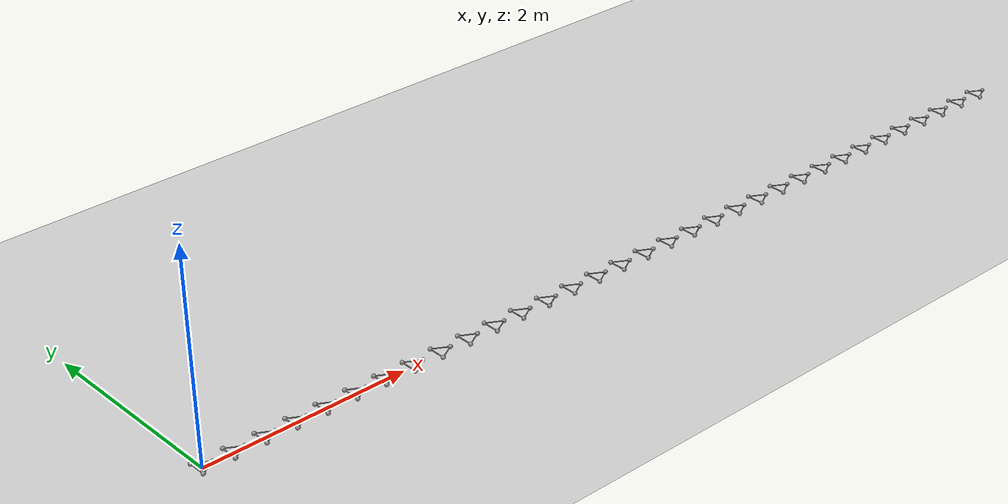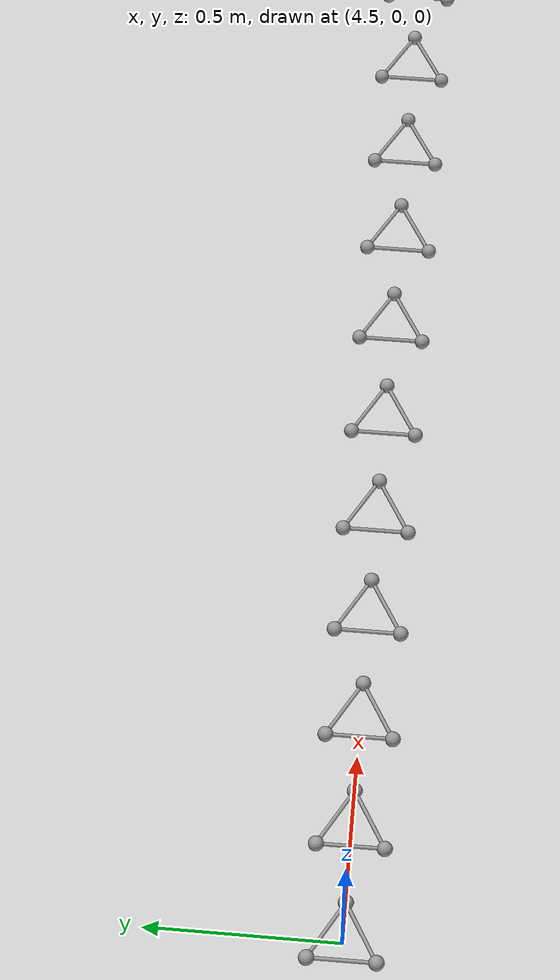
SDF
<?xml version="1.0" ?>

<sdf version="1.6">
  <world name="default">

    <gravity>-0.0 0 -9.8</gravity>

    <include>
      <uri>model://ground_plane</uri>
    </include>

    <include>
      <uri>model://sun</uri>
    </include>

    <physics type="ignored">
      <ode>
        <solver>
          <friction_model>cone_model</friction_model>
        </solver>
      </ode>
    </physics>

    <model name="triball_0">
     <pose> 0.0 0 0 0 0 0 </pose>
     <link name="link">
     <pose>0 0 0.02 0 0 0</pose>
     <inertial>
       <pose>0.0 0.0 0 0 0 0</pose>
       <mass>0.060318578948924034</mass>
       <inertia>
         <ixx>0.000311243867376448</ixx>
         <iyy>0.000311243867376448</iyy>
         <izz>0.0006128367621210681</izz>
         <ixy>0.0</ixy>
         <ixz>0.0</ixz>
         <iyz>0.0</iyz>
       </inertia>
     </inertial>
     <sensor name="imu" type="imu">
       <always_on>true</always_on>
     </sensor>

     <collision name="collision_a">
       <pose>0.09999999999999999 0 0  0 0 0</pose>
       <geometry>
         <sphere>
           <radius>0.02</radius>
         </sphere>
       </geometry>
       <surface>
         <friction>
           <ode>
             <mu>0.9</mu>
             <mu2>0.9</mu2>
             <fdir1>1 0 0</fdir1>
           </ode>
         </friction>
       </surface>
     </collision>
     <visual name="visual_a">
       <pose>0.09999999999999999 0 0  0 0 0</pose>
       <geometry>
         <sphere>
           <radius>0.02</radius>
         </sphere>
       </geometry>
       <material>
         <script>
           <uri>file://media/materials/scripts/gazebo.material</uri>
           <name>Gazebo/Grey</name>
         </script>
       </material>
     </visual>

     <collision name="collision_a_to_b">
       <pose>0.024999999999999998 0.04330127018922193 0.0  -1.5707962969925737 -1.0471975511965974 1.047197525387029</pose>
       <geometry>
         <cylinder>
           <radius>0.005</radius>
           <length>0.17320508075688773</length>
         </cylinder>
       </geometry>
       <surface>
         <friction>
           <ode>
             <mu>0.9</mu>
             <mu2>0.9</mu2>
           </ode>
         </friction>
       </surface>
     </collision>
     <visual name="visual_a_to_b">
       <pose>0.024999999999999998 0.04330127018922193 0.0  -1.5707962969925737 -1.0471975511965974 1.047197525387029</pose>
       <geometry>
         <cylinder>
           <radius>0.005</radius>
           <length>0.17320508075688773</length>
         </cylinder>
       </geometry>
       <material>
         <script>
           <uri>file://media/materials/scripts/gazebo.material</uri>
           <name>Gazebo/Grey</name>
         </script>
       </material>
     </visual>

     <collision name="collision_a_to_c">
       <pose>0.024999999999999998 -0.04330127018922193 0.0  1.5707962969925737 -1.0471975511965974 -1.047197525387029</pose>
       <geometry>
         <cylinder>
           <radius>0.005</radius>
           <length>0.17320508075688773</length>
         </cylinder>
       </geometry>
       <surface>
         <friction>
           <ode>
             <mu>0.9</mu>
             <mu2>0.9</mu2>
           </ode>
         </friction>
       </surface>
     </collision>
     <visual name="visual_a_to_c">
       <pose>0.024999999999999998 -0.04330127018922193 0.0  1.5707962969925737 -1.0471975511965974 -1.047197525387029</pose>
       <geometry>
         <cylinder>
           <radius>0.005</radius>
           <length>0.17320508075688773</length>
         </cylinder>
       </geometry>
       <material>
         <script>
           <uri>file://media/materials/scripts/gazebo.material</uri>
           <name>Gazebo/Grey</name>
         </script>
       </material>
     </visual>

     <collision name="collision_b">
       <pose>-0.049999999999999996 0.08660254037844387 0  0 0 0</pose>
       <geometry>
         <sphere>
           <radius>0.02</radius>
         </sphere>
       </geometry>
       <surface>
         <friction>
           <ode>
             <mu>0.9</mu>
             <mu2>0.9</mu2>
             <fdir1>1 0 0</fdir1>
           </ode>
         </friction>
       </surface>
     </collision>
     <visual name="visual_b">
       <pose>-0.049999999999999996 0.08660254037844387 0  0 0 0</pose>
       <geometry>
         <sphere>
           <radius>0.02</radius>
         </sphere>
       </geometry>
       <material>
         <script>
           <uri>file://media/materials/scripts/gazebo.material</uri>
           <name>Gazebo/Grey</name>
         </script>
       </material>
     </visual>

     <collision name="collision_b_to_c">
       <pose>-0.049999999999999996 0.0 0.0  1.5707963267948963 -0.0 0.0</pose>
       <geometry>
         <cylinder>
           <radius>0.005</radius>
           <length>0.17320508075688773</length>
         </cylinder>
       </geometry>
       <surface>
         <friction>
           <ode>
             <mu>0.9</mu>
             <mu2>0.9</mu2>
           </ode>
         </friction>
       </surface>
     </collision>
     <visual name="visual_b_to_c">
       <pose>-0.049999999999999996 0.0 0.0  1.5707963267948963 -0.0 0.0</pose>
       <geometry>
         <cylinder>
           <radius>0.005</radius>
           <length>0.17320508075688773</length>
         </cylinder>
       </geometry>
       <material>
         <script>
           <uri>file://media/materials/scripts/gazebo.material</uri>
           <name>Gazebo/Grey</name>
         </script>
       </material>
     </visual>

     <collision name="collision_c">
       <pose>-0.049999999999999996 -0.08660254037844387 0  0 0 0</pose>
       <geometry>
         <sphere>
           <radius>0.02</radius>
         </sphere>
       </geometry>
       <surface>
         <friction>
           <ode>
             <mu>0.9</mu>
             <mu2>0.9</mu2>
             <fdir1>1 0 0</fdir1>
           </ode>
         </friction>
       </surface>
     </collision>
     <visual name="visual_c">
       <pose>-0.049999999999999996 -0.08660254037844387 0  0 0 0</pose>
       <geometry>
         <sphere>
           <radius>0.02</radius>
         </sphere>
       </geometry>
       <material>
         <script>
           <uri>file://media/materials/scripts/gazebo.material</uri>
           <name>Gazebo/Grey</name>
         </script>
       </material>
     </visual>

     </link>
     <plugin name="triball_0" filename="libInitialVelocityPlugin.so">
        <linear> 0 15 0 </linear>
        <angular> 0 0 -150.0 </angular>
      </plugin>
    </model>

    <model name="triball_1">
     <pose> 0.3 0 0 0 0 0 </pose>
     <link name="link">
     <pose>0 0 0.02 0 0 0</pose>
     <inertial>
       <pose>0.0 0.0 0 0 0 0</pose>
       <mass>0.060318578948924034</mass>
       <inertia>
         <ixx>0.000311243867376448</ixx>
         <iyy>0.000311243867376448</iyy>
         <izz>0.0006128367621210681</izz>
         <ixy>0.0</ixy>
         <ixz>0.0</ixz>
         <iyz>0.0</iyz>
       </inertia>
     </inertial>
     <sensor name="imu" type="imu">
       <always_on>true</always_on>
     </sensor>

     <collision name="collision_a">
       <pose>0.09999999999999999 0 0  0 0 0</pose>
       <geometry>
         <sphere>
           <radius>0.02</radius>
         </sphere>
       </geometry>
       <surface>
         <friction>
           <ode>
             <mu>0.9</mu>
             <mu2>0.9</mu2>
             <fdir1>1 0 0</fdir1>
           </ode>
         </friction>
       </surface>
     </collision>
     <visual name="visual_a">
       <pose>0.09999999999999999 0 0  0 0 0</pose>
       <geometry>
         <sphere>
           <radius>0.02</radius>
         </sphere>
       </geometry>
       <material>
         <script>
           <uri>file://media/materials/scripts/gazebo.material</uri>
           <name>Gazebo/Grey</name>
         </script>
       </material>
     </visual>

     <collision name="collision_a_to_b">
       <pose>0.024999999999999998 0.04330127018922193 0.0  -1.5707962969925737 -1.0471975511965974 1.047197525387029</pose>
       <geometry>
         <cylinder>
           <radius>0.005</radius>
           <length>0.17320508075688773</length>
         </cylinder>
       </geometry>
       <surface>
         <friction>
           <ode>
             <mu>0.9</mu>
             <mu2>0.9</mu2>
           </ode>
         </friction>
       </surface>
     </collision>
     <visual name="visual_a_to_b">
       <pose>0.024999999999999998 0.04330127018922193 0.0  -1.5707962969925737 -1.0471975511965974 1.047197525387029</pose>
       <geometry>
         <cylinder>
           <radius>0.005</radius>
           <length>0.17320508075688773</length>
         </cylinder>
       </geometry>
       <material>
         <script>
           <uri>file://media/materials/scripts/gazebo.material</uri>
           <name>Gazebo/Grey</name>
         </script>
       </material>
     </visual>

     <collision name="collision_a_to_c">
       <pose>0.024999999999999998 -0.04330127018922193 0.0  1.5707962969925737 -1.0471975511965974 -1.047197525387029</pose>
       <geometry>
         <cylinder>
           <radius>0.005</radius>
           <length>0.17320508075688773</length>
         </cylinder>
       </geometry>
       <surface>
         <friction>
           <ode>
             <mu>0.9</mu>
             <mu2>0.9</mu2>
           </ode>
         </friction>
       </surface>
     </collision>
     <visual name="visual_a_to_c">
       <pose>0.024999999999999998 -0.04330127018922193 0.0  1.5707962969925737 -1.0471975511965974 -1.047197525387029</pose>
       <geometry>
         <cylinder>
           <radius>0.005</radius>
           <length>0.17320508075688773</length>
         </cylinder>
       </geometry>
       <material>
         <script>
           <uri>file://media/materials/scripts/gazebo.material</uri>
           <name>Gazebo/Grey</name>
         </script>
       </material>
     </visual>

     <collision name="collision_b">
       <pose>-0.049999999999999996 0.08660254037844387 0  0 0 0</pose>
       <geometry>
         <sphere>
           <radius>0.02</radius>
         </sphere>
       </geometry>
       <surface>
         <friction>
           <ode>
             <mu>0.9</mu>
             <mu2>0.9</mu2>
             <fdir1>1 0 0</fdir1>
           </ode>
         </friction>
       </surface>
     </collision>
     <visual name="visual_b">
       <pose>-0.049999999999999996 0.08660254037844387 0  0 0 0</pose>
       <geometry>
         <sphere>
           <radius>0.02</radius>
         </sphere>
       </geometry>
       <material>
         <script>
           <uri>file://media/materials/scripts/gazebo.material</uri>
           <name>Gazebo/Grey</name>
         </script>
       </material>
     </visual>

     <collision name="collision_b_to_c">
       <pose>-0.049999999999999996 0.0 0.0  1.5707963267948963 -0.0 0.0</pose>
       <geometry>
         <cylinder>
           <radius>0.005</radius>
           <length>0.17320508075688773</length>
         </cylinder>
       </geometry>
       <surface>
         <friction>
           <ode>
             <mu>0.9</mu>
             <mu2>0.9</mu2>
           </ode>
         </friction>
       </surface>
     </collision>
     <visual name="visual_b_to_c">
       <pose>-0.049999999999999996 0.0 0.0  1.5707963267948963 -0.0 0.0</pose>
       <geometry>
         <cylinder>
           <radius>0.005</radius>
           <length>0.17320508075688773</length>
         </cylinder>
       </geometry>
       <material>
         <script>
           <uri>file://media/materials/scripts/gazebo.material</uri>
           <name>Gazebo/Grey</name>
         </script>
       </material>
     </visual>

     <collision name="collision_c">
       <pose>-0.049999999999999996 -0.08660254037844387 0  0 0 0</pose>
       <geometry>
         <sphere>
           <radius>0.02</radius>
         </sphere>
       </geometry>
       <surface>
         <friction>
           <ode>
             <mu>0.9</mu>
             <mu2>0.9</mu2>
             <fdir1>1 0 0</fdir1>
           </ode>
         </friction>
       </surface>
     </collision>
     <visual name="visual_c">
       <pose>-0.049999999999999996 -0.08660254037844387 0  0 0 0</pose>
       <geometry>
         <sphere>
           <radius>0.02</radius>
         </sphere>
       </geometry>
       <material>
         <script>
           <uri>file://media/materials/scripts/gazebo.material</uri>
           <name>Gazebo/Grey</name>
         </script>
       </material>
     </visual>

     </link>
     <plugin name="triball_1" filename="libInitialVelocityPlugin.so">
        <linear> 0 15 0 </linear>
        <angular> 0 0 -140.625 </angular>
      </plugin>
    </model>

    <model name="triball_2">
     <pose> 0.6 0 0 0 0 0 </pose>
     <link name="link">
     <pose>0 0 0.02 0 0 0</pose>
     <inertial>
       <pose>0.0 0.0 0 0 0 0</pose>
       <mass>0.060318578948924034</mass>
       <inertia>
         <ixx>0.000311243867376448</ixx>
         <iyy>0.000311243867376448</iyy>
         <izz>0.0006128367621210681</izz>
         <ixy>0.0</ixy>
         <ixz>0.0</ixz>
         <iyz>0.0</iyz>
       </inertia>
     </inertial>
     <sensor name="imu" type="imu">
       <always_on>true</always_on>
     </sensor>

     <collision name="collision_a">
       <pose>0.09999999999999999 0 0  0 0 0</pose>
       <geometry>
         <sphere>
           <radius>0.02</radius>
         </sphere>
       </geometry>
       <surface>
         <friction>
           <ode>
             <mu>0.9</mu>
             <mu2>0.9</mu2>
             <fdir1>1 0 0</fdir1>
           </ode>
         </friction>
       </surface>
     </collision>
     <visual name="visual_a">
       <pose>0.09999999999999999 0 0  0 0 0</pose>
       <geometry>
         <sphere>
           <radius>0.02</radius>
         </sphere>
       </geometry>
       <material>
         <script>
           <uri>file://media/materials/scripts/gazebo.material</uri>
           <name>Gazebo/Grey</name>
         </script>
       </material>
     </visual>

     <collision name="collision_a_to_b">
       <pose>0.024999999999999998 0.04330127018922193 0.0  -1.5707962969925737 -1.0471975511965974 1.047197525387029</pose>
       <geometry>
         <cylinder>
           <radius>0.005</radius>
           <length>0.17320508075688773</length>
         </cylinder>
       </geometry>
       <surface>
         <friction>
           <ode>
             <mu>0.9</mu>
             <mu2>0.9</mu2>
           </ode>
         </friction>
       </surface>
     </collision>
     <visual name="visual_a_to_b">
       <pose>0.024999999999999998 0.04330127018922193 0.0  -1.5707962969925737 -1.0471975511965974 1.047197525387029</pose>
       <geometry>
         <cylinder>
           <radius>0.005</radius>
           <length>0.17320508075688773</length>
         </cylinder>
       </geometry>
       <material>
         <script>
           <uri>file://media/materials/scripts/gazebo.material</uri>
           <name>Gazebo/Grey</name>
         </script>
       </material>
     </visual>

     <collision name="collision_a_to_c">
       <pose>0.024999999999999998 -0.04330127018922193 0.0  1.5707962969925737 -1.0471975511965974 -1.047197525387029</pose>
       <geometry>
         <cylinder>
           <radius>0.005</radius>
           <length>0.17320508075688773</length>
         </cylinder>
       </geometry>
       <surface>
         <friction>
           <ode>
             <mu>0.9</mu>
             <mu2>0.9</mu2>
           </ode>
         </friction>
       </surface>
     </collision>
     <visual name="visual_a_to_c">
       <pose>0.024999999999999998 -0.04330127018922193 0.0  1.5707962969925737 -1.0471975511965974 -1.047197525387029</pose>
       <geometry>
         <cylinder>
           <radius>0.005</radius>
           <length>0.17320508075688773</length>
         </cylinder>
       </geometry>
       <material>
         <script>
           <uri>file://media/materials/scripts/gazebo.material</uri>
           <name>Gazebo/Grey</name>
         </script>
       </material>
     </visual>

     <collision name="collision_b">
       <pose>-0.049999999999999996 0.08660254037844387 0  0 0 0</pose>
       <geometry>
         <sphere>
           <radius>0.02</radius>
         </sphere>
       </geometry>
       <surface>
         <friction>
           <ode>
             <mu>0.9</mu>
             <mu2>0.9</mu2>
             <fdir1>1 0 0</fdir1>
           </ode>
         </friction>
       </surface>
     </collision>
     <visual name="visual_b">
       <pose>-0.049999999999999996 0.08660254037844387 0  0 0 0</pose>
       <geometry>
         <sphere>
           <radius>0.02</radius>
         </sphere>
       </geometry>
       <material>
         <script>
           <uri>file://media/materials/scripts/gazebo.material</uri>
           <name>Gazebo/Grey</name>
         </script>
       </material>
     </visual>

     <collision name="collision_b_to_c">
       <pose>-0.049999999999999996 0.0 0.0  1.5707963267948963 -0.0 0.0</pose>
       <geometry>
         <cylinder>
           <radius>0.005</radius>
           <length>0.17320508075688773</length>
         </cylinder>
       </geometry>
       <surface>
         <friction>
           <ode>
             <mu>0.9</mu>
             <mu2>0.9</mu2>
           </ode>
         </friction>
       </surface>
     </collision>
     <visual name="visual_b_to_c">
       <pose>-0.049999999999999996 0.0 0.0  1.5707963267948963 -0.0 0.0</pose>
       <geometry>
         <cylinder>
           <radius>0.005</radius>
           <length>0.17320508075688773</length>
         </cylinder>
       </geometry>
       <material>
         <script>
           <uri>file://media/materials/scripts/gazebo.material</uri>
           <name>Gazebo/Grey</name>
         </script>
       </material>
     </visual>

     <collision name="collision_c">
       <pose>-0.049999999999999996 -0.08660254037844387 0  0 0 0</pose>
       <geometry>
         <sphere>
           <radius>0.02</radius>
         </sphere>
       </geometry>
       <surface>
         <friction>
           <ode>
             <mu>0.9</mu>
             <mu2>0.9</mu2>
             <fdir1>1 0 0</fdir1>
           </ode>
         </friction>
       </surface>
     </collision>
     <visual name="visual_c">
       <pose>-0.049999999999999996 -0.08660254037844387 0  0 0 0</pose>
       <geometry>
         <sphere>
           <radius>0.02</radius>
         </sphere>
       </geometry>
       <material>
         <script>
           <uri>file://media/materials/scripts/gazebo.material</uri>
           <name>Gazebo/Grey</name>
         </script>
       </material>
     </visual>

     </link>
     <plugin name="triball_2" filename="libInitialVelocityPlugin.so">
        <linear> 0 15 0 </linear>
        <angular> 0 0 -131.25 </angular>
      </plugin>
    </model>

    <model name="triball_3">
     <pose> 0.8999999999999999 0 0 0 0 0 </pose>
     <link name="link">
     <pose>0 0 0.02 0 0 0</pose>
     <inertial>
       <pose>0.0 0.0 0 0 0 0</pose>
       <mass>0.060318578948924034</mass>
       <inertia>
         <ixx>0.000311243867376448</ixx>
         <iyy>0.000311243867376448</iyy>
         <izz>0.0006128367621210681</izz>
         <ixy>0.0</ixy>
         <ixz>0.0</ixz>
         <iyz>0.0</iyz>
       </inertia>
     </inertial>
     <sensor name="imu" type="imu">
       <always_on>true</always_on>
     </sensor>

     <collision name="collision_a">
       <pose>0.09999999999999999 0 0  0 0 0</pose>
       <geometry>
         <sphere>
           <radius>0.02</radius>
         </sphere>
       </geometry>
       <surface>
         <friction>
           <ode>
             <mu>0.9</mu>
             <mu2>0.9</mu2>
             <fdir1>1 0 0</fdir1>
           </ode>
         </friction>
       </surface>
     </collision>
     <visual name="visual_a">
       <pose>0.09999999999999999 0 0  0 0 0</pose>
       <geometry>
         <sphere>
           <radius>0.02</radius>
         </sphere>
       </geometry>
       <material>
         <script>
           <uri>file://media/materials/scripts/gazebo.material</uri>
           <name>Gazebo/Grey</name>
         </script>
       </material>
     </visual>

     <collision name="collision_a_to_b">
       <pose>0.024999999999999998 0.04330127018922193 0.0  -1.5707962969925737 -1.0471975511965974 1.047197525387029</pose>
       <geometry>
         <cylinder>
           <radius>0.005</radius>
           <length>0.17320508075688773</length>
         </cylinder>
       </geometry>
       <surface>
         <friction>
           <ode>
             <mu>0.9</mu>
             <mu2>0.9</mu2>
           </ode>
         </friction>
       </surface>
     </collision>
     <visual name="visual_a_to_b">
       <pose>0.024999999999999998 0.04330127018922193 0.0  -1.5707962969925737 -1.0471975511965974 1.047197525387029</pose>
       <geometry>
         <cylinder>
           <radius>0.005</radius>
           <length>0.17320508075688773</length>
         </cylinder>
       </geometry>
       <material>
         <script>
           <uri>file://media/materials/scripts/gazebo.material</uri>
           <name>Gazebo/Grey</name>
         </script>
       </material>
     </visual>

     <collision name="collision_a_to_c">
       <pose>0.024999999999999998 -0.04330127018922193 0.0  1.5707962969925737 -1.0471975511965974 -1.047197525387029</pose>
       <geometry>
         <cylinder>
           <radius>0.005</radius>
           <length>0.17320508075688773</length>
         </cylinder>
       </geometry>
       <surface>
         <friction>
           <ode>
             <mu>0.9</mu>
             <mu2>0.9</mu2>
           </ode>
         </friction>
       </surface>
     </collision>
     <visual name="visual_a_to_c">
       <pose>0.024999999999999998 -0.04330127018922193 0.0  1.5707962969925737 -1.0471975511965974 -1.047197525387029</pose>
       <geometry>
         <cylinder>
           <radius>0.005</radius>
           <length>0.17320508075688773</length>
         </cylinder>
       </geometry>
       <material>
         <script>
           <uri>file://media/materials/scripts/gazebo.material</uri>
           <name>Gazebo/Grey</name>
         </script>
       </material>
     </visual>

     <collision name="collision_b">
       <pose>-0.049999999999999996 0.08660254037844387 0  0 0 0</pose>
       <geometry>
         <sphere>
           <radius>0.02</radius>
         </sphere>
       </geometry>
       <surface>
         <friction>
           <ode>
             <mu>0.9</mu>
             <mu2>0.9</mu2>
             <fdir1>1 0 0</fdir1>
           </ode>
         </friction>
       </surface>
     </collision>
     <visual name="visual_b">
       <pose>-0.049999999999999996 0.08660254037844387 0  0 0 0</pose>
       <geometry>
         <sphere>
           <radius>0.02</radius>
         </sphere>
       </geometry>
       <material>
         <script>
           <uri>file://media/materials/scripts/gazebo.material</uri>
           <name>Gazebo/Grey</name>
         </script>
       </material>
     </visual>

     <collision name="collision_b_to_c">
       <pose>-0.049999999999999996 0.0 0.0  1.5707963267948963 -0.0 0.0</pose>
       <geometry>
         <cylinder>
           <radius>0.005</radius>
           <length>0.17320508075688773</length>
         </cylinder>
       </geometry>
       <surface>
         <friction>
           <ode>
             <mu>0.9</mu>
             <mu2>0.9</mu2>
           </ode>
         </friction>
       </surface>
     </collision>
     <visual name="visual_b_to_c">
       <pose>-0.049999999999999996 0.0 0.0  1.5707963267948963 -0.0 0.0</pose>
       <geometry>
         <cylinder>
           <radius>0.005</radius>
           <length>0.17320508075688773</length>
         </cylinder>
       </geometry>
       <material>
         <script>
           <uri>file://media/materials/scripts/gazebo.material</uri>
           <name>Gazebo/Grey</name>
         </script>
       </material>
     </visual>

     <collision name="collision_c">
       <pose>-0.049999999999999996 -0.08660254037844387 0  0 0 0</pose>
       <geometry>
         <sphere>
           <radius>0.02</radius>
         </sphere>
       </geometry>
       <surface>
         <friction>
           <ode>
             <mu>0.9</mu>
             <mu2>0.9</mu2>
             <fdir1>1 0 0</fdir1>
           </ode>
         </friction>
       </surface>
     </collision>
     <visual name="visual_c">
       <pose>-0.049999999999999996 -0.08660254037844387 0  0 0 0</pose>
       <geometry>
         <sphere>
           <radius>0.02</radius>
         </sphere>
       </geometry>
       <material>
         <script>
           <uri>file://media/materials/scripts/gazebo.material</uri>
           <name>Gazebo/Grey</name>
         </script>
       </material>
     </visual>

     </link>
     <plugin name="triball_3" filename="libInitialVelocityPlugin.so">
        <linear> 0 15 0 </linear>
        <angular> 0 0 -121.875 </angular>
      </plugin>
    </model>

    <model name="triball_4">
     <pose> 1.2 0 0 0 0 0 </pose>
     <link name="link">
     <pose>0 0 0.02 0 0 0</pose>
     <inertial>
       <pose>0.0 0.0 0 0 0 0</pose>
       <mass>0.060318578948924034</mass>
       <inertia>
         <ixx>0.000311243867376448</ixx>
         <iyy>0.000311243867376448</iyy>
         <izz>0.0006128367621210681</izz>
         <ixy>0.0</ixy>
         <ixz>0.0</ixz>
         <iyz>0.0</iyz>
       </inertia>
     </inertial>
     <sensor name="imu" type="imu">
       <always_on>true</always_on>
     </sensor>

     <collision name="collision_a">
       <pose>0.09999999999999999 0 0  0 0 0</pose>
       <geometry>
         <sphere>
           <radius>0.02</radius>
         </sphere>
       </geometry>
       <surface>
         <friction>
           <ode>
             <mu>0.9</mu>
             <mu2>0.9</mu2>
             <fdir1>1 0 0</fdir1>
           </ode>
         </friction>
       </surface>
     </collision>
     <visual name="visual_a">
       <pose>0.09999999999999999 0 0  0 0 0</pose>
       <geometry>
         <sphere>
           <radius>0.02</radius>
         </sphere>
       </geometry>
       <material>
         <script>
           <uri>file://media/materials/scripts/gazebo.material</uri>
           <name>Gazebo/Grey</name>
         </script>
       </material>
     </visual>

     <collision name="collision_a_to_b">
       <pose>0.024999999999999998 0.04330127018922193 0.0  -1.5707962969925737 -1.0471975511965974 1.047197525387029</pose>
       <geometry>
         <cylinder>
           <radius>0.005</radius>
           <length>0.17320508075688773</length>
         </cylinder>
       </geometry>
       <surface>
         <friction>
           <ode>
             <mu>0.9</mu>
             <mu2>0.9</mu2>
           </ode>
         </friction>
       </surface>
     </collision>
     <visual name="visual_a_to_b">
       <pose>0.024999999999999998 0.04330127018922193 0.0  -1.5707962969925737 -1.0471975511965974 1.047197525387029</pose>
       <geometry>
         <cylinder>
           <radius>0.005</radius>
           <length>0.17320508075688773</length>
         </cylinder>
       </geometry>
       <material>
         <script>
           <uri>file://media/materials/scripts/gazebo.material</uri>
           <name>Gazebo/Grey</name>
         </script>
       </material>
     </visual>

     <collision name="collision_a_to_c">
       <pose>0.024999999999999998 -0.04330127018922193 0.0  1.5707962969925737 -1.0471975511965974 -1.047197525387029</pose>
       <geometry>
         <cylinder>
           <radius>0.005</radius>
           <length>0.17320508075688773</length>
         </cylinder>
       </geometry>
       <surface>
         <friction>
           <ode>
             <mu>0.9</mu>
             <mu2>0.9</mu2>
           </ode>
         </friction>
       </surface>
     </collision>
     <visual name="visual_a_to_c">
       <pose>0.024999999999999998 -0.04330127018922193 0.0  1.5707962969925737 -1.0471975511965974 -1.047197525387029</pose>
       <geometry>
         <cylinder>
           <radius>0.005</radius>
           <length>0.17320508075688773</length>
         </cylinder>
       </geometry>
       <material>
         <script>
           <uri>file://media/materials/scripts/gazebo.material</uri>
           <name>Gazebo/Grey</name>
         </script>
       </material>
     </visual>

     <collision name="collision_b">
       <pose>-0.049999999999999996 0.08660254037844387 0  0 0 0</pose>
       <geometry>
         <sphere>
           <radius>0.02</radius>
         </sphere>
       </geometry>
       <surface>
         <friction>
           <ode>
             <mu>0.9</mu>
             <mu2>0.9</mu2>
             <fdir1>1 0 0</fdir1>
           </ode>
         </friction>
       </surface>
     </collision>
     <visual name="visual_b">
       <pose>-0.049999999999999996 0.08660254037844387 0  0 0 0</pose>
       <geometry>
         <sphere>
           <radius>0.02</radius>
         </sphere>
       </geometry>
       <material>
         <script>
           <uri>file://media/materials/scripts/gazebo.material</uri>
           <name>Gazebo/Grey</name>
         </script>
       </material>
     </visual>

     <collision name="collision_b_to_c">
       <pose>-0.049999999999999996 0.0 0.0  1.5707963267948963 -0.0 0.0</pose>
       <geometry>
         <cylinder>
           <radius>0.005</radius>
           <length>0.17320508075688773</length>
         </cylinder>
       </geometry>
       <surface>
         <friction>
           <ode>
             <mu>0.9</mu>
             <mu2>0.9</mu2>
           </ode>
         </friction>
       </surface>
     </collision>
     <visual name="visual_b_to_c">
       <pose>-0.049999999999999996 0.0 0.0  1.5707963267948963 -0.0 0.0</pose>
       <geometry>
         <cylinder>
           <radius>0.005</radius>
           <length>0.17320508075688773</length>
         </cylinder>
       </geometry>
       <material>
         <script>
           <uri>file://media/materials/scripts/gazebo.material</uri>
           <name>Gazebo/Grey</name>
         </script>
       </material>
     </visual>

     <collision name="collision_c">
       <pose>-0.049999999999999996 -0.08660254037844387 0  0 0 0</pose>
       <geometry>
         <sphere>
           <radius>0.02</radius>
         </sphere>
       </geometry>
       <surface>
         <friction>
           <ode>
             <mu>0.9</mu>
             <mu2>0.9</mu2>
             <fdir1>1 0 0</fdir1>
           </ode>
         </friction>
       </surface>
     </collision>
     <visual name="visual_c">
       <pose>-0.049999999999999996 -0.08660254037844387 0  0 0 0</pose>
       <geometry>
         <sphere>
           <radius>0.02</radius>
         </sphere>
       </geometry>
       <material>
         <script>
           <uri>file://media/materials/scripts/gazebo.material</uri>
           <name>Gazebo/Grey</name>
         </script>
       </material>
     </visual>

     </link>
     <plugin name="triball_4" filename="libInitialVelocityPlugin.so">
        <linear> 0 15 0 </linear>
        <angular> 0 0 -112.5 </angular>
      </plugin>
    </model>

    <model name="triball_5">
     <pose> 1.5 0 0 0 0 0 </pose>
     <link name="link">
     <pose>0 0 0.02 0 0 0</pose>
     <inertial>
       <pose>0.0 0.0 0 0 0 0</pose>
       <mass>0.060318578948924034</mass>
       <inertia>
         <ixx>0.000311243867376448</ixx>
         <iyy>0.000311243867376448</iyy>
         <izz>0.0006128367621210681</izz>
         <ixy>0.0</ixy>
         <ixz>0.0</ixz>
         <iyz>0.0</iyz>
       </inertia>
     </inertial>
     <sensor name="imu" type="imu">
       <always_on>true</always_on>
     </sensor>

     <collision name="collision_a">
       <pose>0.09999999999999999 0 0  0 0 0</pose>
       <geometry>
         <sphere>
           <radius>0.02</radius>
         </sphere>
       </geometry>
       <surface>
         <friction>
           <ode>
             <mu>0.9</mu>
             <mu2>0.9</mu2>
             <fdir1>1 0 0</fdir1>
           </ode>
         </friction>
       </surface>
     </collision>
     <visual name="visual_a">
       <pose>0.09999999999999999 0 0  0 0 0</pose>
       <geometry>
         <sphere>
           <radius>0.02</radius>
         </sphere>
       </geometry>
       <material>
         <script>
           <uri>file://media/materials/scripts/gazebo.material</uri>
           <name>Gazebo/Grey</name>
         </script>
       </material>
     </visual>

     <collision name="collision_a_to_b">
       <pose>0.024999999999999998 0.04330127018922193 0.0  -1.5707962969925737 -1.0471975511965974 1.047197525387029</pose>
       <geometry>
         <cylinder>
           <radius>0.005</radius>
           <length>0.17320508075688773</length>
         </cylinder>
       </geometry>
       <surface>
         <friction>
           <ode>
             <mu>0.9</mu>
             <mu2>0.9</mu2>
           </ode>
         </friction>
       </surface>
     </collision>
     <visual name="visual_a_to_b">
       <pose>0.024999999999999998 0.04330127018922193 0.0  -1.5707962969925737 -1.0471975511965974 1.047197525387029</pose>
       <geometry>
         <cylinder>
           <radius>0.005</radius>
           <length>0.17320508075688773</length>
         </cylinder>
       </geometry>
       <material>
         <script>
           <uri>file://media/materials/scripts/gazebo.material</uri>
           <name>Gazebo/Grey</name>
         </script>
       </material>
     </visual>

     <collision name="collision_a_to_c">
       <pose>0.024999999999999998 -0.04330127018922193 0.0  1.5707962969925737 -1.0471975511965974 -1.047197525387029</pose>
       <geometry>
         <cylinder>
           <radius>0.005</radius>
           <length>0.17320508075688773</length>
         </cylinder>
       </geometry>
       <surface>
         <friction>
           <ode>
             <mu>0.9</mu>
             <mu2>0.9</mu2>
           </ode>
         </friction>
       </surface>
     </collision>
     <visual name="visual_a_to_c">
       <pose>0.024999999999999998 -0.04330127018922193 0.0  1.5707962969925737 -1.0471975511965974 -1.047197525387029</pose>
       <geometry>
         <cylinder>
           <radius>0.005</radius>
           <length>0.17320508075688773</length>
         </cylinder>
       </geometry>
       <material>
         <script>
           <uri>file://media/materials/scripts/gazebo.material</uri>
           <name>Gazebo/Grey</name>
         </script>
       </material>
     </visual>

     <collision name="collision_b">
       <pose>-0.049999999999999996 0.08660254037844387 0  0 0 0</pose>
       <geometry>
         <sphere>
           <radius>0.02</radius>
         </sphere>
       </geometry>
       <surface>
         <friction>
           <ode>
             <mu>0.9</mu>
             <mu2>0.9</mu2>
             <fdir1>1 0 0</fdir1>
           </ode>
         </friction>
       </surface>
     </collision>
     <visual name="visual_b">
       <pose>-0.049999999999999996 0.08660254037844387 0  0 0 0</pose>
       <geometry>
         <sphere>
           <radius>0.02</radius>
         </sphere>
       </geometry>
       <material>
         <script>
           <uri>file://media/materials/scripts/gazebo.material</uri>
           <name>Gazebo/Grey</name>
         </script>
       </material>
     </visual>

     <collision name="collision_b_to_c">
       <pose>-0.049999999999999996 0.0 0.0  1.5707963267948963 -0.0 0.0</pose>
       <geometry>
         <cylinder>
           <radius>0.005</radius>
           <length>0.17320508075688773</length>
         </cylinder>
       </geometry>
       <surface>
         <friction>
           <ode>
             <mu>0.9</mu>
             <mu2>0.9</mu2>
           </ode>
         </friction>
       </surface>
     </collision>
     <visual name="visual_b_to_c">
       <pose>-0.049999999999999996 0.0 0.0  1.5707963267948963 -0.0 0.0</pose>
       <geometry>
         <cylinder>
           <radius>0.005</radius>
           <length>0.17320508075688773</length>
         </cylinder>
       </geometry>
       <material>
         <script>
           <uri>file://media/materials/scripts/gazebo.material</uri>
           <name>Gazebo/Grey</name>
         </script>
       </material>
     </visual>

     <collision name="collision_c">
       <pose>-0.049999999999999996 -0.08660254037844387 0  0 0 0</pose>
       <geometry>
         <sphere>
           <radius>0.02</radius>
         </sphere>
       </geometry>
       <surface>
         <friction>
           <ode>
             <mu>0.9</mu>
             <mu2>0.9</mu2>
             <fdir1>1 0 0</fdir1>
           </ode>
         </friction>
       </surface>
     </collision>
     <visual name="visual_c">
       <pose>-0.049999999999999996 -0.08660254037844387 0  0 0 0</pose>
       <geometry>
         <sphere>
           <radius>0.02</radius>
         </sphere>
       </geometry>
       <material>
         <script>
           <uri>file://media/materials/scripts/gazebo.material</uri>
           <name>Gazebo/Grey</name>
         </script>
       </material>
     </visual>

     </link>
     <plugin name="triball_5" filename="libInitialVelocityPlugin.so">
        <linear> 0 15 0 </linear>
        <angular> 0 0 -103.125 </angular>
      </plugin>
    </model>

    <model name="triball_6">
     <pose> 1.7999999999999998 0 0 0 0 0 </pose>
     <link name="link">
     <pose>0 0 0.02 0 0 0</pose>
     <inertial>
       <pose>0.0 0.0 0 0 0 0</pose>
       <mass>0.060318578948924034</mass>
       <inertia>
         <ixx>0.000311243867376448</ixx>
         <iyy>0.000311243867376448</iyy>
         <izz>0.0006128367621210681</izz>
         <ixy>0.0</ixy>
         <ixz>0.0</ixz>
         <iyz>0.0</iyz>
       </inertia>
     </inertial>
     <sensor name="imu" type="imu">
       <always_on>true</always_on>
     </sensor>

     <collision name="collision_a">
       <pose>0.09999999999999999 0 0  0 0 0</pose>
       <geometry>
         <sphere>
           <radius>0.02</radius>
         </sphere>
       </geometry>
       <surface>
         <friction>
           <ode>
             <mu>0.9</mu>
             <mu2>0.9</mu2>
             <fdir1>1 0 0</fdir1>
           </ode>
         </friction>
       </surface>
     </collision>
     <visual name="visual_a">
       <pose>0.09999999999999999 0 0  0 0 0</pose>
       <geometry>
         <sphere>
           <radius>0.02</radius>
         </sphere>
       </geometry>
       <material>
         <script>
           <uri>file://media/materials/scripts/gazebo.material</uri>
           <name>Gazebo/Grey</name>
         </script>
       </material>
     </visual>

     <collision name="collision_a_to_b">
       <pose>0.024999999999999998 0.04330127018922193 0.0  -1.5707962969925737 -1.0471975511965974 1.047197525387029</pose>
       <geometry>
         <cylinder>
           <radius>0.005</radius>
           <length>0.17320508075688773</length>
         </cylinder>
       </geometry>
       <surface>
         <friction>
           <ode>
             <mu>0.9</mu>
             <mu2>0.9</mu2>
           </ode>
         </friction>
       </surface>
     </collision>
     <visual name="visual_a_to_b">
       <pose>0.024999999999999998 0.04330127018922193 0.0  -1.5707962969925737 -1.0471975511965974 1.047197525387029</pose>
       <geometry>
         <cylinder>
           <radius>0.005</radius>
           <length>0.17320508075688773</length>
         </cylinder>
       </geometry>
       <material>
         <script>
           <uri>file://media/materials/scripts/gazebo.material</uri>
           <name>Gazebo/Grey</name>
         </script>
       </material>
     </visual>

     <collision name="collision_a_to_c">
       <pose>0.024999999999999998 -0.04330127018922193 0.0  1.5707962969925737 -1.0471975511965974 -1.047197525387029</pose>
       <geometry>
         <cylinder>
           <radius>0.005</radius>
           <length>0.17320508075688773</length>
         </cylinder>
       </geometry>
       <surface>
         <friction>
           <ode>
             <mu>0.9</mu>
             <mu2>0.9</mu2>
           </ode>
         </friction>
       </surface>
     </collision>
     <visual name="visual_a_to_c">
       <pose>0.024999999999999998 -0.04330127018922193 0.0  1.5707962969925737 -1.0471975511965974 -1.047197525387029</pose>
       <geometry>
         <cylinder>
           <radius>0.005</radius>
           <length>0.17320508075688773</length>
         </cylinder>
       </geometry>
       <material>
         <script>
           <uri>file://media/materials/scripts/gazebo.material</uri>
           <name>Gazebo/Grey</name>
         </script>
       </material>
     </visual>

     <collision name="collision_b">
       <pose>-0.049999999999999996 0.08660254037844387 0  0 0 0</pose>
       <geometry>
         <sphere>
           <radius>0.02</radius>
         </sphere>
       </geometry>
       <surface>
         <friction>
           <ode>
             <mu>0.9</mu>
             <mu2>0.9</mu2>
             <fdir1>1 0 0</fdir1>
           </ode>
         </friction>
       </surface>
     </collision>
     <visual name="visual_b">
       <pose>-0.049999999999999996 0.08660254037844387 0  0 0 0</pose>
       <geometry>
         <sphere>
           <radius>0.02</radius>
         </sphere>
       </geometry>
       <material>
         <script>
           <uri>file://media/materials/scripts/gazebo.material</uri>
           <name>Gazebo/Grey</name>
         </script>
       </material>
     </visual>

     <collision name="collision_b_to_c">
       <pose>-0.049999999999999996 0.0 0.0  1.5707963267948963 -0.0 0.0</pose>
       <geometry>
         <cylinder>
           <radius>0.005</radius>
           <length>0.17320508075688773</length>
         </cylinder>
       </geometry>
       <surface>
         <friction>
           <ode>
             <mu>0.9</mu>
             <mu2>0.9</mu2>
           </ode>
         </friction>
       </surface>
     </collision>
     <visual name="visual_b_to_c">
       <pose>-0.049999999999999996 0.0 0.0  1.5707963267948963 -0.0 0.0</pose>
       <geometry>
         <cylinder>
           <radius>0.005</radius>
           <length>0.17320508075688773</length>
         </cylinder>
       </geometry>
       <material>
         <script>
           <uri>file://media/materials/scripts/gazebo.material</uri>
           <name>Gazebo/Grey</name>
         </script>
       </material>
     </visual>

     <collision name="collision_c">
       <pose>-0.049999999999999996 -0.08660254037844387 0  0 0 0</pose>
       <geometry>
         <sphere>
           <radius>0.02</radius>
         </sphere>
       </geometry>
       <surface>
         <friction>
           <ode>
             <mu>0.9</mu>
             <mu2>0.9</mu2>
             <fdir1>1 0 0</fdir1>
           </ode>
         </friction>
       </surface>
     </collision>
     <visual name="visual_c">
       <pose>-0.049999999999999996 -0.08660254037844387 0  0 0 0</pose>
       <geometry>
         <sphere>
           <radius>0.02</radius>
         </sphere>
       </geometry>
       <material>
         <script>
           <uri>file://media/materials/scripts/gazebo.material</uri>
           <name>Gazebo/Grey</name>
         </script>
       </material>
     </visual>

     </link>
     <plugin name="triball_6" filename="libInitialVelocityPlugin.so">
        <linear> 0 15 0 </linear>
        <angular> 0 0 -93.75 </angular>
      </plugin>
    </model>

    <model name="triball_7">
     <pose> 2.1 0 0 0 0 0 </pose>
     <link name="link">
     <pose>0 0 0.02 0 0 0</pose>
     <inertial>
       <pose>0.0 0.0 0 0 0 0</pose>
       <mass>0.060318578948924034</mass>
       <inertia>
         <ixx>0.000311243867376448</ixx>
         <iyy>0.000311243867376448</iyy>
         <izz>0.0006128367621210681</izz>
         <ixy>0.0</ixy>
         <ixz>0.0</ixz>
         <iyz>0.0</iyz>
       </inertia>
     </inertial>
     <sensor name="imu" type="imu">
       <always_on>true</always_on>
     </sensor>

     <collision name="collision_a">
       <pose>0.09999999999999999 0 0  0 0 0</pose>
       <geometry>
         <sphere>
           <radius>0.02</radius>
         </sphere>
       </geometry>
       <surface>
         <friction>
           <ode>
             <mu>0.9</mu>
             <mu2>0.9</mu2>
             <fdir1>1 0 0</fdir1>
           </ode>
         </friction>
       </surface>
     </collision>
     <visual name="visual_a">
       <pose>0.09999999999999999 0 0  0 0 0</pose>
       <geometry>
         <sphere>
           <radius>0.02</radius>
         </sphere>
       </geometry>
       <material>
         <script>
           <uri>file://media/materials/scripts/gazebo.material</uri>
           <name>Gazebo/Grey</name>
         </script>
       </material>
     </visual>

     <collision name="collision_a_to_b">
       <pose>0.024999999999999998 0.04330127018922193 0.0  -1.5707962969925737 -1.0471975511965974 1.047197525387029</pose>
       <geometry>
         <cylinder>
           <radius>0.005</radius>
           <length>0.17320508075688773</length>
         </cylinder>
       </geometry>
       <surface>
         <friction>
           <ode>
             <mu>0.9</mu>
             <mu2>0.9</mu2>
           </ode>
         </friction>
       </surface>
     </collision>
     <visual name="visual_a_to_b">
       <pose>0.024999999999999998 0.04330127018922193 0.0  -1.5707962969925737 -1.0471975511965974 1.047197525387029</pose>
       <geometry>
         <cylinder>
           <radius>0.005</radius>
           <length>0.17320508075688773</length>
         </cylinder>
       </geometry>
       <material>
         <script>
           <uri>file://media/materials/scripts/gazebo.material</uri>
           <name>Gazebo/Grey</name>
         </script>
       </material>
     </visual>

     <collision name="collision_a_to_c">
       <pose>0.024999999999999998 -0.04330127018922193 0.0  1.5707962969925737 -1.0471975511965974 -1.047197525387029</pose>
       <geometry>
         <cylinder>
           <radius>0.005</radius>
           <length>0.17320508075688773</length>
         </cylinder>
       </geometry>
       <surface>
         <friction>
           <ode>
             <mu>0.9</mu>
             <mu2>0.9</mu2>
           </ode>
         </friction>
       </surface>
     </collision>
     <visual name="visual_a_to_c">
       <pose>0.024999999999999998 -0.04330127018922193 0.0  1.5707962969925737 -1.0471975511965974 -1.047197525387029</pose>
       <geometry>
         <cylinder>
           <radius>0.005</radius>
           <length>0.17320508075688773</length>
         </cylinder>
       </geometry>
       <material>
         <script>
           <uri>file://media/materials/scripts/gazebo.material</uri>
           <name>Gazebo/Grey</name>
         </script>
       </material>
     </visual>

     <collision name="collision_b">
       <pose>-0.049999999999999996 0.08660254037844387 0  0 0 0</pose>
       <geometry>
         <sphere>
           <radius>0.02</radius>
         </sphere>
       </geometry>
       <surface>
         <friction>
           <ode>
             <mu>0.9</mu>
             <mu2>0.9</mu2>
             <fdir1>1 0 0</fdir1>
           </ode>
         </friction>
       </surface>
     </collision>
     <visual name="visual_b">
       <pose>-0.049999999999999996 0.08660254037844387 0  0 0 0</pose>
       <geometry>
         <sphere>
           <radius>0.02</radius>
         </sphere>
       </geometry>
       <material>
         <script>
           <uri>file://media/materials/scripts/gazebo.material</uri>
           <name>Gazebo/Grey</name>
         </script>
       </material>
     </visual>

     <collision name="collision_b_to_c">
       <pose>-0.049999999999999996 0.0 0.0  1.5707963267948963 -0.0 0.0</pose>
       <geometry>
         <cylinder>
           <radius>0.005</radius>
           <length>0.17320508075688773</length>
         </cylinder>
       </geometry>
       <surface>
         <friction>
           <ode>
             <mu>0.9</mu>
             <mu2>0.9</mu2>
           </ode>
         </friction>
       </surface>
     </collision>
     <visual name="visual_b_to_c">
       <pose>-0.049999999999999996 0.0 0.0  1.5707963267948963 -0.0 0.0</pose>
       <geometry>
         <cylinder>
           <radius>0.005</radius>
           <length>0.17320508075688773</length>
         </cylinder>
       </geometry>
       <material>
         <script>
           <uri>file://media/materials/scripts/gazebo.material</uri>
           <name>Gazebo/Grey</name>
         </script>
       </material>
     </visual>

     <collision name="collision_c">
       <pose>-0.049999999999999996 -0.08660254037844387 0  0 0 0</pose>
       <geometry>
         <sphere>
           <radius>0.02</radius>
         </sphere>
       </geometry>
       <surface>
         <friction>
           <ode>
             <mu>0.9</mu>
             <mu2>0.9</mu2>
             <fdir1>1 0 0</fdir1>
           </ode>
         </friction>
       </surface>
     </collision>
     <visual name="visual_c">
       <pose>-0.049999999999999996 -0.08660254037844387 0  0 0 0</pose>
       <geometry>
         <sphere>
           <radius>0.02</radius>
         </sphere>
       </geometry>
       <material>
         <script>
           <uri>file://media/materials/scripts/gazebo.material</uri>
           <name>Gazebo/Grey</name>
         </script>
       </material>
     </visual>

     </link>
     <plugin name="triball_7" filename="libInitialVelocityPlugin.so">
        <linear> 0 15 0 </linear>
        <angular> 0 0 -84.375 </angular>
      </plugin>
    </model>

    <model name="triball_8">
     <pose> 2.4 0 0 0 0 0 </pose>
     <link name="link">
     <pose>0 0 0.02 0 0 0</pose>
     <inertial>
       <pose>0.0 0.0 0 0 0 0</pose>
       <mass>0.060318578948924034</mass>
       <inertia>
         <ixx>0.000311243867376448</ixx>
         <iyy>0.000311243867376448</iyy>
         <izz>0.0006128367621210681</izz>
         <ixy>0.0</ixy>
         <ixz>0.0</ixz>
         <iyz>0.0</iyz>
       </inertia>
     </inertial>
     <sensor name="imu" type="imu">
       <always_on>true</always_on>
     </sensor>

     <collision name="collision_a">
       <pose>0.09999999999999999 0 0  0 0 0</pose>
       <geometry>
         <sphere>
           <radius>0.02</radius>
         </sphere>
       </geometry>
       <surface>
         <friction>
           <ode>
             <mu>0.9</mu>
             <mu2>0.9</mu2>
             <fdir1>1 0 0</fdir1>
           </ode>
         </friction>
       </surface>
     </collision>
     <visual name="visual_a">
       <pose>0.09999999999999999 0 0  0 0 0</pose>
       <geometry>
         <sphere>
           <radius>0.02</radius>
         </sphere>
       </geometry>
       <material>
         <script>
           <uri>file://media/materials/scripts/gazebo.material</uri>
           <name>Gazebo/Grey</name>
         </script>
       </material>
     </visual>

     <collision name="collision_a_to_b">
       <pose>0.024999999999999998 0.04330127018922193 0.0  -1.5707962969925737 -1.0471975511965974 1.047197525387029</pose>
       <geometry>
         <cylinder>
           <radius>0.005</radius>
           <length>0.17320508075688773</length>
         </cylinder>
       </geometry>
       <surface>
         <friction>
           <ode>
             <mu>0.9</mu>
             <mu2>0.9</mu2>
           </ode>
         </friction>
       </surface>
     </collision>
     <visual name="visual_a_to_b">
       <pose>0.024999999999999998 0.04330127018922193 0.0  -1.5707962969925737 -1.0471975511965974 1.047197525387029</pose>
       <geometry>
         <cylinder>
           <radius>0.005</radius>
           <length>0.17320508075688773</length>
         </cylinder>
       </geometry>
       <material>
         <script>
           <uri>file://media/materials/scripts/gazebo.material</uri>
           <name>Gazebo/Grey</name>
         </script>
       </material>
     </visual>

     <collision name="collision_a_to_c">
       <pose>0.024999999999999998 -0.04330127018922193 0.0  1.5707962969925737 -1.0471975511965974 -1.047197525387029</pose>
       <geometry>
         <cylinder>
           <radius>0.005</radius>
           <length>0.17320508075688773</length>
         </cylinder>
       </geometry>
       <surface>
         <friction>
           <ode>
             <mu>0.9</mu>
             <mu2>0.9</mu2>
           </ode>
         </friction>
       </surface>
     </collision>
     <visual name="visual_a_to_c">
       <pose>0.024999999999999998 -0.04330127018922193 0.0  1.5707962969925737 -1.0471975511965974 -1.047197525387029</pose>
       <geometry>
         <cylinder>
           <radius>0.005</radius>
           <length>0.17320508075688773</length>
         </cylinder>
       </geometry>
       <material>
         <script>
           <uri>file://media/materials/scripts/gazebo.material</uri>
           <name>Gazebo/Grey</name>
         </script>
       </material>
     </visual>

     <collision name="collision_b">
       <pose>-0.049999999999999996 0.08660254037844387 0  0 0 0</pose>
       <geometry>
         <sphere>
           <radius>0.02</radius>
         </sphere>
       </geometry>
       <surface>
         <friction>
           <ode>
             <mu>0.9</mu>
             <mu2>0.9</mu2>
             <fdir1>1 0 0</fdir1>
           </ode>
         </friction>
       </surface>
     </collision>
     <visual name="visual_b">
       <pose>-0.049999999999999996 0.08660254037844387 0  0 0 0</pose>
       <geometry>
         <sphere>
           <radius>0.02</radius>
         </sphere>
       </geometry>
       <material>
         <script>
           <uri>file://media/materials/scripts/gazebo.material</uri>
           <name>Gazebo/Grey</name>
         </script>
       </material>
     </visual>

     <collision name="collision_b_to_c">
       <pose>-0.049999999999999996 0.0 0.0  1.5707963267948963 -0.0 0.0</pose>
       <geometry>
         <cylinder>
           <radius>0.005</radius>
           <length>0.17320508075688773</length>
         </cylinder>
       </geometry>
       <surface>
         <friction>
           <ode>
             <mu>0.9</mu>
             <mu2>0.9</mu2>
           </ode>
         </friction>
       </surface>
     </collision>
     <visual name="visual_b_to_c">
       <pose>-0.049999999999999996 0.0 0.0  1.5707963267948963 -0.0 0.0</pose>
       <geometry>
         <cylinder>
           <radius>0.005</radius>
           <length>0.17320508075688773</length>
         </cylinder>
       </geometry>
       <material>
         <script>
           <uri>file://media/materials/scripts/gazebo.material</uri>
           <name>Gazebo/Grey</name>
         </script>
       </material>
     </visual>

     <collision name="collision_c">
       <pose>-0.049999999999999996 -0.08660254037844387 0  0 0 0</pose>
       <geometry>
         <sphere>
           <radius>0.02</radius>
         </sphere>
       </geometry>
       <surface>
         <friction>
           <ode>
             <mu>0.9</mu>
             <mu2>0.9</mu2>
             <fdir1>1 0 0</fdir1>
           </ode>
         </friction>
       </surface>
     </collision>
     <visual name="visual_c">
       <pose>-0.049999999999999996 -0.08660254037844387 0  0 0 0</pose>
       <geometry>
         <sphere>
           <radius>0.02</radius>
         </sphere>
       </geometry>
       <material>
         <script>
           <uri>file://media/materials/scripts/gazebo.material</uri>
           <name>Gazebo/Grey</name>
         </script>
       </material>
     </visual>

     </link>
     <plugin name="triball_8" filename="libInitialVelocityPlugin.so">
        <linear> 0 15 0 </linear>
        <angular> 0 0 -75.0 </angular>
      </plugin>
    </model>

    <model name="triball_9">
     <pose> 2.6999999999999997 0 0 0 0 0 </pose>
     <link name="link">
     <pose>0 0 0.02 0 0 0</pose>
     <inertial>
       <pose>0.0 0.0 0 0 0 0</pose>
       <mass>0.060318578948924034</mass>
       <inertia>
         <ixx>0.000311243867376448</ixx>
         <iyy>0.000311243867376448</iyy>
         <izz>0.0006128367621210681</izz>
         <ixy>0.0</ixy>
         <ixz>0.0</ixz>
         <iyz>0.0</iyz>
       </inertia>
     </inertial>
     <sensor name="imu" type="imu">
       <always_on>true</always_on>
     </sensor>

     <collision name="collision_a">
       <pose>0.09999999999999999 0 0  0 0 0</pose>
       <geometry>
         <sphere>
           <radius>0.02</radius>
         </sphere>
       </geometry>
       <surface>
         <friction>
           <ode>
             <mu>0.9</mu>
             <mu2>0.9</mu2>
             <fdir1>1 0 0</fdir1>
           </ode>
         </friction>
       </surface>
     </collision>
     <visual name="visual_a">
       <pose>0.09999999999999999 0 0  0 0 0</pose>
       <geometry>
         <sphere>
           <radius>0.02</radius>
         </sphere>
       </geometry>
       <material>
         <script>
           <uri>file://media/materials/scripts/gazebo.material</uri>
           <name>Gazebo/Grey</name>
         </script>
       </material>
     </visual>

     <collision name="collision_a_to_b">
       <pose>0.024999999999999998 0.04330127018922193 0.0  -1.5707962969925737 -1.0471975511965974 1.047197525387029</pose>
       <geometry>
         <cylinder>
           <radius>0.005</radius>
           <length>0.17320508075688773</length>
         </cylinder>
       </geometry>
       <surface>
         <friction>
           <ode>
             <mu>0.9</mu>
             <mu2>0.9</mu2>
           </ode>
         </friction>
       </surface>
     </collision>
     <visual name="visual_a_to_b">
       <pose>0.024999999999999998 0.04330127018922193 0.0  -1.5707962969925737 -1.0471975511965974 1.047197525387029</pose>
       <geometry>
         <cylinder>
           <radius>0.005</radius>
           <length>0.17320508075688773</length>
         </cylinder>
       </geometry>
       <material>
         <script>
           <uri>file://media/materials/scripts/gazebo.material</uri>
           <name>Gazebo/Grey</name>
         </script>
       </material>
     </visual>

     <collision name="collision_a_to_c">
       <pose>0.024999999999999998 -0.04330127018922193 0.0  1.5707962969925737 -1.0471975511965974 -1.047197525387029</pose>
       <geometry>
         <cylinder>
           <radius>0.005</radius>
           <length>0.17320508075688773</length>
         </cylinder>
       </geometry>
       <surface>
         <friction>
           <ode>
             <mu>0.9</mu>
             <mu2>0.9</mu2>
           </ode>
         </friction>
       </surface>
     </collision>
     <visual name="visual_a_to_c">
       <pose>0.024999999999999998 -0.04330127018922193 0.0  1.5707962969925737 -1.0471975511965974 -1.047197525387029</pose>
       <geometry>
         <cylinder>
           <radius>0.005</radius>
           <length>0.17320508075688773</length>
         </cylinder>
       </geometry>
       <material>
         <script>
           <uri>file://media/materials/scripts/gazebo.material</uri>
           <name>Gazebo/Grey</name>
         </script>
       </material>
     </visual>

     <collision name="collision_b">
       <pose>-0.049999999999999996 0.08660254037844387 0  0 0 0</pose>
       <geometry>
         <sphere>
           <radius>0.02</radius>
         </sphere>
       </geometry>
       <surface>
         <friction>
           <ode>
             <mu>0.9</mu>
             <mu2>0.9</mu2>
             <fdir1>1 0 0</fdir1>
           </ode>
         </friction>
       </surface>
     </collision>
     <visual name="visual_b">
       <pose>-0.049999999999999996 0.08660254037844387 0  0 0 0</pose>
       <geometry>
         <sphere>
           <radius>0.02</radius>
         </sphere>
       </geometry>
       <material>
         <script>
           <uri>file://media/materials/scripts/gazebo.material</uri>
           <name>Gazebo/Grey</name>
         </script>
       </material>
     </visual>

     <collision name="collision_b_to_c">
       <pose>-0.049999999999999996 0.0 0.0  1.5707963267948963 -0.0 0.0</pose>
       <geometry>
         <cylinder>
           <radius>0.005</radius>
           <length>0.17320508075688773</length>
         </cylinder>
       </geometry>
       <surface>
         <friction>
           <ode>
             <mu>0.9</mu>
             <mu2>0.9</mu2>
           </ode>
         </friction>
       </surface>
     </collision>
     <visual name="visual_b_to_c">
       <pose>-0.049999999999999996 0.0 0.0  1.5707963267948963 -0.0 0.0</pose>
       <geometry>
         <cylinder>
           <radius>0.005</radius>
           <length>0.17320508075688773</length>
         </cylinder>
       </geometry>
       <material>
         <script>
           <uri>file://media/materials/scripts/gazebo.material</uri>
           <name>Gazebo/Grey</name>
         </script>
       </material>
     </visual>

     <collision name="collision_c">
       <pose>-0.049999999999999996 -0.08660254037844387 0  0 0 0</pose>
       <geometry>
         <sphere>
           <radius>0.02</radius>
         </sphere>
       </geometry>
       <surface>
         <friction>
           <ode>
             <mu>0.9</mu>
             <mu2>0.9</mu2>
             <fdir1>1 0 0</fdir1>
           </ode>
         </friction>
       </surface>
     </collision>
     <visual name="visual_c">
       <pose>-0.049999999999999996 -0.08660254037844387 0  0 0 0</pose>
       <geometry>
         <sphere>
           <radius>0.02</radius>
         </sphere>
       </geometry>
       <material>
         <script>
           <uri>file://media/materials/scripts/gazebo.material</uri>
           <name>Gazebo/Grey</name>
         </script>
       </material>
     </visual>

     </link>
     <plugin name="triball_9" filename="libInitialVelocityPlugin.so">
        <linear> 0 15 0 </linear>
        <angular> 0 0 -65.625 </angular>
      </plugin>
    </model>

    <model name="triball_10">
     <pose> 3.0 0 0 0 0 0 </pose>
     <link name="link">
     <pose>0 0 0.02 0 0 0</pose>
     <inertial>
       <pose>0.0 0.0 0 0 0 0</pose>
       <mass>0.060318578948924034</mass>
       <inertia>
         <ixx>0.000311243867376448</ixx>
         <iyy>0.000311243867376448</iyy>
         <izz>0.0006128367621210681</izz>
         <ixy>0.0</ixy>
         <ixz>0.0</ixz>
         <iyz>0.0</iyz>
       </inertia>
     </inertial>
     <sensor name="imu" type="imu">
       <always_on>true</always_on>
     </sensor>

     <collision name="collision_a">
       <pose>0.09999999999999999 0 0  0 0 0</pose>
       <geometry>
         <sphere>
           <radius>0.02</radius>
         </sphere>
       </geometry>
       <surface>
         <friction>
           <ode>
             <mu>0.9</mu>
             <mu2>0.9</mu2>
             <fdir1>1 0 0</fdir1>
           </ode>
         </friction>
       </surface>
     </collision>
     <visual name="visual_a">
       <pose>0.09999999999999999 0 0  0 0 0</pose>
       <geometry>
         <sphere>
           <radius>0.02</radius>
         </sphere>
       </geometry>
       <material>
         <script>
           <uri>file://media/materials/scripts/gazebo.material</uri>
           <name>Gazebo/Grey</name>
         </script>
       </material>
     </visual>

     <collision name="collision_a_to_b">
       <pose>0.024999999999999998 0.04330127018922193 0.0  -1.5707962969925737 -1.0471975511965974 1.047197525387029</pose>
       <geometry>
         <cylinder>
           <radius>0.005</radius>
           <length>0.17320508075688773</length>
         </cylinder>
       </geometry>
       <surface>
         <friction>
           <ode>
             <mu>0.9</mu>
             <mu2>0.9</mu2>
           </ode>
         </friction>
       </surface>
     </collision>
     <visual name="visual_a_to_b">
       <pose>0.024999999999999998 0.04330127018922193 0.0  -1.5707962969925737 -1.0471975511965974 1.047197525387029</pose>
       <geometry>
         <cylinder>
           <radius>0.005</radius>
           <length>0.17320508075688773</length>
         </cylinder>
       </geometry>
       <material>
         <script>
           <uri>file://media/materials/scripts/gazebo.material</uri>
           <name>Gazebo/Grey</name>
         </script>
       </material>
     </visual>

     <collision name="collision_a_to_c">
       <pose>0.024999999999999998 -0.04330127018922193 0.0  1.5707962969925737 -1.0471975511965974 -1.047197525387029</pose>
       <geometry>
         <cylinder>
           <radius>0.005</radius>
           <length>0.17320508075688773</length>
         </cylinder>
       </geometry>
       <surface>
         <friction>
           <ode>
             <mu>0.9</mu>
             <mu2>0.9</mu2>
           </ode>
         </friction>
       </surface>
     </collision>
     <visual name="visual_a_to_c">
       <pose>0.024999999999999998 -0.04330127018922193 0.0  1.5707962969925737 -1.0471975511965974 -1.047197525387029</pose>
       <geometry>
         <cylinder>
           <radius>0.005</radius>
           <length>0.17320508075688773</length>
         </cylinder>
       </geometry>
       <material>
         <script>
           <uri>file://media/materials/scripts/gazebo.material</uri>
           <name>Gazebo/Grey</name>
         </script>
       </material>
     </visual>

     <collision name="collision_b">
       <pose>-0.049999999999999996 0.08660254037844387 0  0 0 0</pose>
       <geometry>
         <sphere>
           <radius>0.02</radius>
         </sphere>
       </geometry>
       <surface>
         <friction>
           <ode>
             <mu>0.9</mu>
             <mu2>0.9</mu2>
             <fdir1>1 0 0</fdir1>
           </ode>
         </friction>
       </surface>
     </collision>
     <visual name="visual_b">
       <pose>-0.049999999999999996 0.08660254037844387 0  0 0 0</pose>
       <geometry>
         <sphere>
           <radius>0.02</radius>
         </sphere>
       </geometry>
       <material>
         <script>
           <uri>file://media/materials/scripts/gazebo.material</uri>
           <name>Gazebo/Grey</name>
         </script>
       </material>
     </visual>

     <collision name="collision_b_to_c">
       <pose>-0.049999999999999996 0.0 0.0  1.5707963267948963 -0.0 0.0</pose>
       <geometry>
         <cylinder>
           <radius>0.005</radius>
           <length>0.17320508075688773</length>
         </cylinder>
       </geometry>
       <surface>
         <friction>
           <ode>
             <mu>0.9</mu>
             <mu2>0.9</mu2>
           </ode>
         </friction>
       </surface>
     </collision>
     <visual name="visual_b_to_c">
       <pose>-0.049999999999999996 0.0 0.0  1.5707963267948963 -0.0 0.0</pose>
       <geometry>
         <cylinder>
           <radius>0.005</radius>
           <length>0.17320508075688773</length>
         </cylinder>
       </geometry>
       <material>
         <script>
           <uri>file://media/materials/scripts/gazebo.material</uri>
           <name>Gazebo/Grey</name>
         </script>
       </material>
     </visual>

     <collision name="collision_c">
       <pose>-0.049999999999999996 -0.08660254037844387 0  0 0 0</pose>
       <geometry>
         <sphere>
           <radius>0.02</radius>
         </sphere>
       </geometry>
       <surface>
         <friction>
           <ode>
             <mu>0.9</mu>
             <mu2>0.9</mu2>
             <fdir1>1 0 0</fdir1>
           </ode>
         </friction>
       </surface>
     </collision>
     <visual name="visual_c">
       <pose>-0.049999999999999996 -0.08660254037844387 0  0 0 0</pose>
       <geometry>
         <sphere>
           <radius>0.02</radius>
         </sphere>
       </geometry>
       <material>
         <script>
           <uri>file://media/materials/scripts/gazebo.material</uri>
           <name>Gazebo/Grey</name>
         </script>
       </material>
     </visual>

     </link>
     <plugin name="triball_10" filename="libInitialVelocityPlugin.so">
        <linear> 0 15 0 </linear>
        <angular> 0 0 -56.25 </angular>
      </plugin>
    </model>

    <model name="triball_11">
     <pose> 3.3 0 0 0 0 0 </pose>
     <link name="link">
     <pose>0 0 0.02 0 0 0</pose>
     <inertial>
       <pose>0.0 0.0 0 0 0 0</pose>
       <mass>0.060318578948924034</mass>
       <inertia>
         <ixx>0.000311243867376448</ixx>
         <iyy>0.000311243867376448</iyy>
         <izz>0.0006128367621210681</izz>
         <ixy>0.0</ixy>
         <ixz>0.0</ixz>
         <iyz>0.0</iyz>
       </inertia>
     </inertial>
     <sensor name="imu" type="imu">
       <always_on>true</always_on>
     </sensor>

     <collision name="collision_a">
       <pose>0.09999999999999999 0 0  0 0 0</pose>
       <geometry>
         <sphere>
           <radius>0.02</radius>
         </sphere>
       </geometry>
       <surface>
         <friction>
           <ode>
             <mu>0.9</mu>
             <mu2>0.9</mu2>
             <fdir1>1 0 0</fdir1>
           </ode>
         </friction>
       </surface>
     </collision>
     <visual name="visual_a">
       <pose>0.09999999999999999 0 0  0 0 0</pose>
       <geometry>
         <sphere>
           <radius>0.02</radius>
         </sphere>
       </geometry>
       <material>
         <script>
           <uri>file://media/materials/scripts/gazebo.material</uri>
           <name>Gazebo/Grey</name>
         </script>
       </material>
     </visual>

     <collision name="collision_a_to_b">
       <pose>0.024999999999999998 0.04330127018922193 0.0  -1.5707962969925737 -1.0471975511965974 1.047197525387029</pose>
       <geometry>
         <cylinder>
           <radius>0.005</radius>
           <length>0.17320508075688773</length>
         </cylinder>
       </geometry>
       <surface>
         <friction>
           <ode>
             <mu>0.9</mu>
             <mu2>0.9</mu2>
           </ode>
         </friction>
       </surface>
     </collision>
     <visual name="visual_a_to_b">
       <pose>0.024999999999999998 0.04330127018922193 0.0  -1.5707962969925737 -1.0471975511965974 1.047197525387029</pose>
       <geometry>
         <cylinder>
           <radius>0.005</radius>
           <length>0.17320508075688773</length>
         </cylinder>
       </geometry>
       <material>
         <script>
           <uri>file://media/materials/scripts/gazebo.material</uri>
           <name>Gazebo/Grey</name>
         </script>
       </material>
     </visual>

     <collision name="collision_a_to_c">
       <pose>0.024999999999999998 -0.04330127018922193 0.0  1.5707962969925737 -1.0471975511965974 -1.047197525387029</pose>
       <geometry>
         <cylinder>
           <radius>0.005</radius>
           <length>0.17320508075688773</length>
         </cylinder>
       </geometry>
       <surface>
         <friction>
           <ode>
             <mu>0.9</mu>
             <mu2>0.9</mu2>
           </ode>
         </friction>
       </surface>
     </collision>
     <visual name="visual_a_to_c">
       <pose>0.024999999999999998 -0.04330127018922193 0.0  1.5707962969925737 -1.0471975511965974 -1.047197525387029</pose>
       <geometry>
         <cylinder>
           <radius>0.005</radius>
           <length>0.17320508075688773</length>
         </cylinder>
       </geometry>
       <material>
         <script>
           <uri>file://media/materials/scripts/gazebo.material</uri>
           <name>Gazebo/Grey</name>
         </script>
       </material>
     </visual>

     <collision name="collision_b">
       <pose>-0.049999999999999996 0.08660254037844387 0  0 0 0</pose>
       <geometry>
         <sphere>
           <radius>0.02</radius>
         </sphere>
       </geometry>
       <surface>
         <friction>
           <ode>
             <mu>0.9</mu>
             <mu2>0.9</mu2>
             <fdir1>1 0 0</fdir1>
           </ode>
         </friction>
       </surface>
     </collision>
     <visual name="visual_b">
       <pose>-0.049999999999999996 0.08660254037844387 0  0 0 0</pose>
       <geometry>
         <sphere>
           <radius>0.02</radius>
         </sphere>
       </geometry>
       <material>
         <script>
           <uri>file://media/materials/scripts/gazebo.material</uri>
           <name>Gazebo/Grey</name>
         </script>
       </material>
     </visual>

     <collision name="collision_b_to_c">
       <pose>-0.049999999999999996 0.0 0.0  1.5707963267948963 -0.0 0.0</pose>
       <geometry>
         <cylinder>
           <radius>0.005</radius>
           <length>0.17320508075688773</length>
         </cylinder>
       </geometry>
       <surface>
         <friction>
           <ode>
             <mu>0.9</mu>
             <mu2>0.9</mu2>
           </ode>
         </friction>
       </surface>
     </collision>
     <visual name="visual_b_to_c">
       <pose>-0.049999999999999996 0.0 0.0  1.5707963267948963 -0.0 0.0</pose>
       <geometry>
         <cylinder>
           <radius>0.005</radius>
           <length>0.17320508075688773</length>
         </cylinder>
       </geometry>
       <material>
         <script>
           <uri>file://media/materials/scripts/gazebo.material</uri>
           <name>Gazebo/Grey</name>
         </script>
       </material>
     </visual>

     <collision name="collision_c">
       <pose>-0.049999999999999996 -0.08660254037844387 0  0 0 0</pose>
       <geometry>
         <sphere>
           <radius>0.02</radius>
         </sphere>
       </geometry>
       <surface>
         <friction>
           <ode>
             <mu>0.9</mu>
             <mu2>0.9</mu2>
             <fdir1>1 0 0</fdir1>
           </ode>
         </friction>
       </surface>
     </collision>
     <visual name="visual_c">
       <pose>-0.049999999999999996 -0.08660254037844387 0  0 0 0</pose>
       <geometry>
         <sphere>
           <radius>0.02</radius>
         </sphere>
       </geometry>
       <material>
         <script>
           <uri>file://media/materials/scripts/gazebo.material</uri>
           <name>Gazebo/Grey</name>
         </script>
       </material>
     </visual>

     </link>
     <plugin name="triball_11" filename="libInitialVelocityPlugin.so">
        <linear> 0 15 0 </linear>
        <angular> 0 0 -46.875 </angular>
      </plugin>
    </model>

    <model name="triball_12">
     <pose> 3.5999999999999996 0 0 0 0 0 </pose>
     <link name="link">
     <pose>0 0 0.02 0 0 0</pose>
     <inertial>
       <pose>0.0 0.0 0 0 0 0</pose>
       <mass>0.060318578948924034</mass>
       <inertia>
         <ixx>0.000311243867376448</ixx>
         <iyy>0.000311243867376448</iyy>
         <izz>0.0006128367621210681</izz>
         <ixy>0.0</ixy>
         <ixz>0.0</ixz>
         <iyz>0.0</iyz>
       </inertia>
     </inertial>
     <sensor name="imu" type="imu">
       <always_on>true</always_on>
     </sensor>

     <collision name="collision_a">
       <pose>0.09999999999999999 0 0  0 0 0</pose>
       <geometry>
         <sphere>
           <radius>0.02</radius>
         </sphere>
       </geometry>
       <surface>
         <friction>
           <ode>
             <mu>0.9</mu>
             <mu2>0.9</mu2>
             <fdir1>1 0 0</fdir1>
           </ode>
         </friction>
       </surface>
     </collision>
     <visual name="visual_a">
       <pose>0.09999999999999999 0 0  0 0 0</pose>
       <geometry>
         <sphere>
           <radius>0.02</radius>
         </sphere>
       </geometry>
       <material>
         <script>
           <uri>file://media/materials/scripts/gazebo.material</uri>
           <name>Gazebo/Grey</name>
         </script>
       </material>
     </visual>

     <collision name="collision_a_to_b">
       <pose>0.024999999999999998 0.04330127018922193 0.0  -1.5707962969925737 -1.0471975511965974 1.047197525387029</pose>
       <geometry>
         <cylinder>
           <radius>0.005</radius>
           <length>0.17320508075688773</length>
         </cylinder>
       </geometry>
       <surface>
         <friction>
           <ode>
             <mu>0.9</mu>
             <mu2>0.9</mu2>
           </ode>
         </friction>
       </surface>
     </collision>
     <visual name="visual_a_to_b">
       <pose>0.024999999999999998 0.04330127018922193 0.0  -1.5707962969925737 -1.0471975511965974 1.047197525387029</pose>
       <geometry>
         <cylinder>
           <radius>0.005</radius>
           <length>0.17320508075688773</length>
         </cylinder>
       </geometry>
       <material>
         <script>
           <uri>file://media/materials/scripts/gazebo.material</uri>
           <name>Gazebo/Grey</name>
         </script>
       </material>
     </visual>

     <collision name="collision_a_to_c">
       <pose>0.024999999999999998 -0.04330127018922193 0.0  1.5707962969925737 -1.0471975511965974 -1.047197525387029</pose>
       <geometry>
         <cylinder>
           <radius>0.005</radius>
           <length>0.17320508075688773</length>
         </cylinder>
       </geometry>
       <surface>
         <friction>
           <ode>
             <mu>0.9</mu>
             <mu2>0.9</mu2>
           </ode>
         </friction>
       </surface>
     </collision>
     <visual name="visual_a_to_c">
       <pose>0.024999999999999998 -0.04330127018922193 0.0  1.5707962969925737 -1.0471975511965974 -1.047197525387029</pose>
       <geometry>
         <cylinder>
           <radius>0.005</radius>
           <length>0.17320508075688773</length>
         </cylinder>
       </geometry>
       <material>
         <script>
           <uri>file://media/materials/scripts/gazebo.material</uri>
           <name>Gazebo/Grey</name>
         </script>
       </material>
     </visual>

     <collision name="collision_b">
       <pose>-0.049999999999999996 0.08660254037844387 0  0 0 0</pose>
       <geometry>
         <sphere>
           <radius>0.02</radius>
         </sphere>
       </geometry>
       <surface>
         <friction>
           <ode>
             <mu>0.9</mu>
             <mu2>0.9</mu2>
             <fdir1>1 0 0</fdir1>
           </ode>
         </friction>
       </surface>
     </collision>
     <visual name="visual_b">
       <pose>-0.049999999999999996 0.08660254037844387 0  0 0 0</pose>
       <geometry>
         <sphere>
           <radius>0.02</radius>
         </sphere>
       </geometry>
       <material>
         <script>
           <uri>file://media/materials/scripts/gazebo.material</uri>
           <name>Gazebo/Grey</name>
         </script>
       </material>
     </visual>

     <collision name="collision_b_to_c">
       <pose>-0.049999999999999996 0.0 0.0  1.5707963267948963 -0.0 0.0</pose>
       <geometry>
         <cylinder>
           <radius>0.005</radius>
           <length>0.17320508075688773</length>
         </cylinder>
       </geometry>
       <surface>
         <friction>
           <ode>
             <mu>0.9</mu>
             <mu2>0.9</mu2>
           </ode>
         </friction>
       </surface>
     </collision>
     <visual name="visual_b_to_c">
       <pose>-0.049999999999999996 0.0 0.0  1.5707963267948963 -0.0 0.0</pose>
       <geometry>
         <cylinder>
           <radius>0.005</radius>
           <length>0.17320508075688773</length>
         </cylinder>
       </geometry>
       <material>
         <script>
           <uri>file://media/materials/scripts/gazebo.material</uri>
           <name>Gazebo/Grey</name>
         </script>
       </material>
     </visual>

     <collision name="collision_c">
       <pose>-0.049999999999999996 -0.08660254037844387 0  0 0 0</pose>
       <geometry>
         <sphere>
           <radius>0.02</radius>
         </sphere>
       </geometry>
       <surface>
         <friction>
           <ode>
             <mu>0.9</mu>
             <mu2>0.9</mu2>
             <fdir1>1 0 0</fdir1>
           </ode>
         </friction>
       </surface>
     </collision>
     <visual name="visual_c">
       <pose>-0.049999999999999996 -0.08660254037844387 0  0 0 0</pose>
       <geometry>
         <sphere>
           <radius>0.02</radius>
         </sphere>
       </geometry>
       <material>
         <script>
           <uri>file://media/materials/scripts/gazebo.material</uri>
           <name>Gazebo/Grey</name>
         </script>
       </material>
     </visual>

     </link>
     <plugin name="triball_12" filename="libInitialVelocityPlugin.so">
        <linear> 0 15 0 </linear>
        <angular> 0 0 -37.5 </angular>
      </plugin>
    </model>

    <model name="triball_13">
     <pose> 3.9 0 0 0 0 0 </pose>
     <link name="link">
     <pose>0 0 0.02 0 0 0</pose>
     <inertial>
       <pose>0.0 0.0 0 0 0 0</pose>
       <mass>0.060318578948924034</mass>
       <inertia>
         <ixx>0.000311243867376448</ixx>
         <iyy>0.000311243867376448</iyy>
         <izz>0.0006128367621210681</izz>
         <ixy>0.0</ixy>
         <ixz>0.0</ixz>
         <iyz>0.0</iyz>
       </inertia>
     </inertial>
     <sensor name="imu" type="imu">
       <always_on>true</always_on>
     </sensor>

     <collision name="collision_a">
       <pose>0.09999999999999999 0 0  0 0 0</pose>
       <geometry>
         <sphere>
           <radius>0.02</radius>
         </sphere>
       </geometry>
       <surface>
         <friction>
           <ode>
             <mu>0.9</mu>
             <mu2>0.9</mu2>
             <fdir1>1 0 0</fdir1>
           </ode>
         </friction>
       </surface>
     </collision>
     <visual name="visual_a">
       <pose>0.09999999999999999 0 0  0 0 0</pose>
       <geometry>
         <sphere>
           <radius>0.02</radius>
         </sphere>
       </geometry>
       <material>
         <script>
           <uri>file://media/materials/scripts/gazebo.material</uri>
           <name>Gazebo/Grey</name>
         </script>
       </material>
     </visual>

     <collision name="collision_a_to_b">
       <pose>0.024999999999999998 0.04330127018922193 0.0  -1.5707962969925737 -1.0471975511965974 1.047197525387029</pose>
       <geometry>
         <cylinder>
           <radius>0.005</radius>
           <length>0.17320508075688773</length>
         </cylinder>
       </geometry>
       <surface>
         <friction>
           <ode>
             <mu>0.9</mu>
             <mu2>0.9</mu2>
           </ode>
         </friction>
       </surface>
     </collision>
     <visual name="visual_a_to_b">
       <pose>0.024999999999999998 0.04330127018922193 0.0  -1.5707962969925737 -1.0471975511965974 1.047197525387029</pose>
       <geometry>
         <cylinder>
           <radius>0.005</radius>
           <length>0.17320508075688773</length>
         </cylinder>
       </geometry>
       <material>
         <script>
           <uri>file://media/materials/scripts/gazebo.material</uri>
           <name>Gazebo/Grey</name>
         </script>
       </material>
     </visual>

     <collision name="collision_a_to_c">
       <pose>0.024999999999999998 -0.04330127018922193 0.0  1.5707962969925737 -1.0471975511965974 -1.047197525387029</pose>
       <geometry>
         <cylinder>
           <radius>0.005</radius>
           <length>0.17320508075688773</length>
         </cylinder>
       </geometry>
       <surface>
         <friction>
           <ode>
             <mu>0.9</mu>
             <mu2>0.9</mu2>
           </ode>
         </friction>
       </surface>
     </collision>
     <visual name="visual_a_to_c">
       <pose>0.024999999999999998 -0.04330127018922193 0.0  1.5707962969925737 -1.0471975511965974 -1.047197525387029</pose>
       <geometry>
         <cylinder>
           <radius>0.005</radius>
           <length>0.17320508075688773</length>
         </cylinder>
       </geometry>
       <material>
         <script>
           <uri>file://media/materials/scripts/gazebo.material</uri>
           <name>Gazebo/Grey</name>
         </script>
       </material>
     </visual>

     <collision name="collision_b">
       <pose>-0.049999999999999996 0.08660254037844387 0  0 0 0</pose>
       <geometry>
         <sphere>
           <radius>0.02</radius>
         </sphere>
       </geometry>
       <surface>
         <friction>
           <ode>
             <mu>0.9</mu>
             <mu2>0.9</mu2>
             <fdir1>1 0 0</fdir1>
           </ode>
         </friction>
       </surface>
     </collision>
     <visual name="visual_b">
       <pose>-0.049999999999999996 0.08660254037844387 0  0 0 0</pose>
       <geometry>
         <sphere>
           <radius>0.02</radius>
         </sphere>
       </geometry>
       <material>
         <script>
           <uri>file://media/materials/scripts/gazebo.material</uri>
           <name>Gazebo/Grey</name>
         </script>
       </material>
     </visual>

     <collision name="collision_b_to_c">
       <pose>-0.049999999999999996 0.0 0.0  1.5707963267948963 -0.0 0.0</pose>
       <geometry>
         <cylinder>
           <radius>0.005</radius>
           <length>0.17320508075688773</length>
         </cylinder>
       </geometry>
       <surface>
         <friction>
           <ode>
             <mu>0.9</mu>
             <mu2>0.9</mu2>
           </ode>
         </friction>
       </surface>
     </collision>
     <visual name="visual_b_to_c">
       <pose>-0.049999999999999996 0.0 0.0  1.5707963267948963 -0.0 0.0</pose>
       <geometry>
         <cylinder>
           <radius>0.005</radius>
           <length>0.17320508075688773</length>
         </cylinder>
       </geometry>
       <material>
         <script>
           <uri>file://media/materials/scripts/gazebo.material</uri>
           <name>Gazebo/Grey</name>
         </script>
       </material>
     </visual>

     <collision name="collision_c">
       <pose>-0.049999999999999996 -0.08660254037844387 0  0 0 0</pose>
       <geometry>
         <sphere>
           <radius>0.02</radius>
         </sphere>
       </geometry>
       <surface>
         <friction>
           <ode>
             <mu>0.9</mu>
             <mu2>0.9</mu2>
             <fdir1>1 0 0</fdir1>
           </ode>
         </friction>
       </surface>
     </collision>
     <visual name="visual_c">
       <pose>-0.049999999999999996 -0.08660254037844387 0  0 0 0</pose>
       <geometry>
         <sphere>
           <radius>0.02</radius>
         </sphere>
       </geometry>
       <material>
         <script>
           <uri>file://media/materials/scripts/gazebo.material</uri>
           <name>Gazebo/Grey</name>
         </script>
       </material>
     </visual>

     </link>
     <plugin name="triball_13" filename="libInitialVelocityPlugin.so">
        <linear> 0 15 0 </linear>
        <angular> 0 0 -28.125 </angular>
      </plugin>
    </model>

    <model name="triball_14">
     <pose> 4.2 0 0 0 0 0 </pose>
     <link name="link">
     <pose>0 0 0.02 0 0 0</pose>
     <inertial>
       <pose>0.0 0.0 0 0 0 0</pose>
       <mass>0.060318578948924034</mass>
       <inertia>
         <ixx>0.000311243867376448</ixx>
         <iyy>0.000311243867376448</iyy>
         <izz>0.0006128367621210681</izz>
         <ixy>0.0</ixy>
         <ixz>0.0</ixz>
         <iyz>0.0</iyz>
       </inertia>
     </inertial>
     <sensor name="imu" type="imu">
       <always_on>true</always_on>
     </sensor>

     <collision name="collision_a">
       <pose>0.09999999999999999 0 0  0 0 0</pose>
       <geometry>
         <sphere>
           <radius>0.02</radius>
         </sphere>
       </geometry>
       <surface>
         <friction>
           <ode>
             <mu>0.9</mu>
             <mu2>0.9</mu2>
             <fdir1>1 0 0</fdir1>
           </ode>
         </friction>
       </surface>
     </collision>
     <visual name="visual_a">
       <pose>0.09999999999999999 0 0  0 0 0</pose>
       <geometry>
         <sphere>
           <radius>0.02</radius>
         </sphere>
       </geometry>
       <material>
         <script>
           <uri>file://media/materials/scripts/gazebo.material</uri>
           <name>Gazebo/Grey</name>
         </script>
       </material>
     </visual>

     <collision name="collision_a_to_b">
       <pose>0.024999999999999998 0.04330127018922193 0.0  -1.5707962969925737 -1.0471975511965974 1.047197525387029</pose>
       <geometry>
         <cylinder>
           <radius>0.005</radius>
           <length>0.17320508075688773</length>
         </cylinder>
       </geometry>
       <surface>
         <friction>
           <ode>
             <mu>0.9</mu>
             <mu2>0.9</mu2>
           </ode>
         </friction>
       </surface>
     </collision>
     <visual name="visual_a_to_b">
       <pose>0.024999999999999998 0.04330127018922193 0.0  -1.5707962969925737 -1.0471975511965974 1.047197525387029</pose>
       <geometry>
         <cylinder>
           <radius>0.005</radius>
           <length>0.17320508075688773</length>
         </cylinder>
       </geometry>
       <material>
         <script>
           <uri>file://media/materials/scripts/gazebo.material</uri>
           <name>Gazebo/Grey</name>
         </script>
       </material>
     </visual>

     <collision name="collision_a_to_c">
       <pose>0.024999999999999998 -0.04330127018922193 0.0  1.5707962969925737 -1.0471975511965974 -1.047197525387029</pose>
       <geometry>
         <cylinder>
           <radius>0.005</radius>
           <length>0.17320508075688773</length>
         </cylinder>
       </geometry>
       <surface>
         <friction>
           <ode>
             <mu>0.9</mu>
             <mu2>0.9</mu2>
           </ode>
         </friction>
       </surface>
     </collision>
     <visual name="visual_a_to_c">
       <pose>0.024999999999999998 -0.04330127018922193 0.0  1.5707962969925737 -1.0471975511965974 -1.047197525387029</pose>
       <geometry>
         <cylinder>
           <radius>0.005</radius>
           <length>0.17320508075688773</length>
         </cylinder>
       </geometry>
       <material>
         <script>
           <uri>file://media/materials/scripts/gazebo.material</uri>
           <name>Gazebo/Grey</name>
         </script>
       </material>
     </visual>

     <collision name="collision_b">
       <pose>-0.049999999999999996 0.08660254037844387 0  0 0 0</pose>
       <geometry>
         <sphere>
           <radius>0.02</radius>
         </sphere>
       </geometry>
       <surface>
         <friction>
           <ode>
             <mu>0.9</mu>
             <mu2>0.9</mu2>
             <fdir1>1 0 0</fdir1>
           </ode>
         </friction>
       </surface>
     </collision>
     <visual name="visual_b">
       <pose>-0.049999999999999996 0.08660254037844387 0  0 0 0</pose>
       <geometry>
         <sphere>
           <radius>0.02</radius>
         </sphere>
       </geometry>
       <material>
         <script>
           <uri>file://media/materials/scripts/gazebo.material</uri>
           <name>Gazebo/Grey</name>
         </script>
       </material>
     </visual>

     <collision name="collision_b_to_c">
       <pose>-0.049999999999999996 0.0 0.0  1.5707963267948963 -0.0 0.0</pose>
       <geometry>
         <cylinder>
           <radius>0.005</radius>
           <length>0.17320508075688773</length>
         </cylinder>
       </geometry>
       <surface>
         <friction>
           <ode>
             <mu>0.9</mu>
             <mu2>0.9</mu2>
           </ode>
         </friction>
       </surface>
     </collision>
     <visual name="visual_b_to_c">
       <pose>-0.049999999999999996 0.0 0.0  1.5707963267948963 -0.0 0.0</pose>
       <geometry>
         <cylinder>
           <radius>0.005</radius>
           <length>0.17320508075688773</length>
         </cylinder>
       </geometry>
       <material>
         <script>
           <uri>file://media/materials/scripts/gazebo.material</uri>
           <name>Gazebo/Grey</name>
         </script>
       </material>
     </visual>

     <collision name="collision_c">
       <pose>-0.049999999999999996 -0.08660254037844387 0  0 0 0</pose>
       <geometry>
         <sphere>
           <radius>0.02</radius>
         </sphere>
       </geometry>
       <surface>
         <friction>
           <ode>
             <mu>0.9</mu>
             <mu2>0.9</mu2>
             <fdir1>1 0 0</fdir1>
           </ode>
         </friction>
       </surface>
     </collision>
     <visual name="visual_c">
       <pose>-0.049999999999999996 -0.08660254037844387 0  0 0 0</pose>
       <geometry>
         <sphere>
           <radius>0.02</radius>
         </sphere>
       </geometry>
       <material>
         <script>
           <uri>file://media/materials/scripts/gazebo.material</uri>
           <name>Gazebo/Grey</name>
         </script>
       </material>
     </visual>

     </link>
     <plugin name="triball_14" filename="libInitialVelocityPlugin.so">
        <linear> 0 15 0 </linear>
        <angular> 0 0 -18.75 </angular>
      </plugin>
    </model>

    <model name="triball_15">
     <pose> 4.5 0 0 0 0 0 </pose>
     <link name="link">
     <pose>0 0 0.02 0 0 0</pose>
     <inertial>
       <pose>0.0 0.0 0 0 0 0</pose>
       <mass>0.060318578948924034</mass>
       <inertia>
         <ixx>0.000311243867376448</ixx>
         <iyy>0.000311243867376448</iyy>
         <izz>0.0006128367621210681</izz>
         <ixy>0.0</ixy>
         <ixz>0.0</ixz>
         <iyz>0.0</iyz>
       </inertia>
     </inertial>
     <sensor name="imu" type="imu">
       <always_on>true</always_on>
     </sensor>

     <collision name="collision_a">
       <pose>0.09999999999999999 0 0  0 0 0</pose>
       <geometry>
         <sphere>
           <radius>0.02</radius>
         </sphere>
       </geometry>
       <surface>
         <friction>
           <ode>
             <mu>0.9</mu>
             <mu2>0.9</mu2>
             <fdir1>1 0 0</fdir1>
           </ode>
         </friction>
       </surface>
     </collision>
     <visual name="visual_a">
       <pose>0.09999999999999999 0 0  0 0 0</pose>
       <geometry>
         <sphere>
           <radius>0.02</radius>
         </sphere>
       </geometry>
       <material>
         <script>
           <uri>file://media/materials/scripts/gazebo.material</uri>
           <name>Gazebo/Grey</name>
         </script>
       </material>
     </visual>

     <collision name="collision_a_to_b">
       <pose>0.024999999999999998 0.04330127018922193 0.0  -1.5707962969925737 -1.0471975511965974 1.047197525387029</pose>
       <geometry>
         <cylinder>
           <radius>0.005</radius>
           <length>0.17320508075688773</length>
         </cylinder>
       </geometry>
       <surface>
         <friction>
           <ode>
             <mu>0.9</mu>
             <mu2>0.9</mu2>
           </ode>
         </friction>
       </surface>
     </collision>
     <visual name="visual_a_to_b">
       <pose>0.024999999999999998 0.04330127018922193 0.0  -1.5707962969925737 -1.0471975511965974 1.047197525387029</pose>
       <geometry>
         <cylinder>
           <radius>0.005</radius>
           <length>0.17320508075688773</length>
         </cylinder>
       </geometry>
       <material>
         <script>
           <uri>file://media/materials/scripts/gazebo.material</uri>
           <name>Gazebo/Grey</name>
         </script>
       </material>
     </visual>

     <collision name="collision_a_to_c">
       <pose>0.024999999999999998 -0.04330127018922193 0.0  1.5707962969925737 -1.0471975511965974 -1.047197525387029</pose>
       <geometry>
         <cylinder>
           <radius>0.005</radius>
           <length>0.17320508075688773</length>
         </cylinder>
       </geometry>
       <surface>
         <friction>
           <ode>
             <mu>0.9</mu>
             <mu2>0.9</mu2>
           </ode>
         </friction>
       </surface>
     </collision>
     <visual name="visual_a_to_c">
       <pose>0.024999999999999998 -0.04330127018922193 0.0  1.5707962969925737 -1.0471975511965974 -1.047197525387029</pose>
       <geometry>
         <cylinder>
           <radius>0.005</radius>
           <length>0.17320508075688773</length>
         </cylinder>
       </geometry>
       <material>
         <script>
           <uri>file://media/materials/scripts/gazebo.material</uri>
           <name>Gazebo/Grey</name>
         </script>
       </material>
     </visual>

     <collision name="collision_b">
       <pose>-0.049999999999999996 0.08660254037844387 0  0 0 0</pose>
       <geometry>
         <sphere>
           <radius>0.02</radius>
         </sphere>
       </geometry>
       <surface>
         <friction>
           <ode>
             <mu>0.9</mu>
             <mu2>0.9</mu2>
             <fdir1>1 0 0</fdir1>
           </ode>
         </friction>
       </surface>
     </collision>
     <visual name="visual_b">
       <pose>-0.049999999999999996 0.08660254037844387 0  0 0 0</pose>
       <geometry>
         <sphere>
           <radius>0.02</radius>
         </sphere>
       </geometry>
       <material>
         <script>
           <uri>file://media/materials/scripts/gazebo.material</uri>
           <name>Gazebo/Grey</name>
         </script>
       </material>
     </visual>

     <collision name="collision_b_to_c">
       <pose>-0.049999999999999996 0.0 0.0  1.5707963267948963 -0.0 0.0</pose>
       <geometry>
         <cylinder>
           <radius>0.005</radius>
           <length>0.17320508075688773</length>
         </cylinder>
       </geometry>
       <surface>
         <friction>
           <ode>
             <mu>0.9</mu>
             <mu2>0.9</mu2>
           </ode>
         </friction>
       </surface>
     </collision>
     <visual name="visual_b_to_c">
       <pose>-0.049999999999999996 0.0 0.0  1.5707963267948963 -0.0 0.0</pose>
       <geometry>
         <cylinder>
           <radius>0.005</radius>
           <length>0.17320508075688773</length>
         </cylinder>
       </geometry>
       <material>
         <script>
           <uri>file://media/materials/scripts/gazebo.material</uri>
           <name>Gazebo/Grey</name>
         </script>
       </material>
     </visual>

     <collision name="collision_c">
       <pose>-0.049999999999999996 -0.08660254037844387 0  0 0 0</pose>
       <geometry>
         <sphere>
           <radius>0.02</radius>
         </sphere>
       </geometry>
       <surface>
         <friction>
           <ode>
             <mu>0.9</mu>
             <mu2>0.9</mu2>
             <fdir1>1 0 0</fdir1>
           </ode>
         </friction>
       </surface>
     </collision>
     <visual name="visual_c">
       <pose>-0.049999999999999996 -0.08660254037844387 0  0 0 0</pose>
       <geometry>
         <sphere>
           <radius>0.02</radius>
         </sphere>
       </geometry>
       <material>
         <script>
           <uri>file://media/materials/scripts/gazebo.material</uri>
           <name>Gazebo/Grey</name>
         </script>
       </material>
     </visual>

     </link>
     <plugin name="triball_15" filename="libInitialVelocityPlugin.so">
        <linear> 0 15 0 </linear>
        <angular> 0 0 -9.375 </angular>
      </plugin>
    </model>

    <model name="triball_16">
     <pose> 4.8 0 0 0 0 0 </pose>
     <link name="link">
     <pose>0 0 0.02 0 0 0</pose>
     <inertial>
       <pose>0.0 0.0 0 0 0 0</pose>
       <mass>0.060318578948924034</mass>
       <inertia>
         <ixx>0.000311243867376448</ixx>
         <iyy>0.000311243867376448</iyy>
         <izz>0.0006128367621210681</izz>
         <ixy>0.0</ixy>
         <ixz>0.0</ixz>
         <iyz>0.0</iyz>
       </inertia>
     </inertial>
     <sensor name="imu" type="imu">
       <always_on>true</always_on>
     </sensor>

     <collision name="collision_a">
       <pose>0.09999999999999999 0 0  0 0 0</pose>
       <geometry>
         <sphere>
           <radius>0.02</radius>
         </sphere>
       </geometry>
       <surface>
         <friction>
           <ode>
             <mu>0.9</mu>
             <mu2>0.9</mu2>
             <fdir1>1 0 0</fdir1>
           </ode>
         </friction>
       </surface>
     </collision>
     <visual name="visual_a">
       <pose>0.09999999999999999 0 0  0 0 0</pose>
       <geometry>
         <sphere>
           <radius>0.02</radius>
         </sphere>
       </geometry>
       <material>
         <script>
           <uri>file://media/materials/scripts/gazebo.material</uri>
           <name>Gazebo/Grey</name>
         </script>
       </material>
     </visual>

     <collision name="collision_a_to_b">
       <pose>0.024999999999999998 0.04330127018922193 0.0  -1.5707962969925737 -1.0471975511965974 1.047197525387029</pose>
       <geometry>
         <cylinder>
           <radius>0.005</radius>
           <length>0.17320508075688773</length>
         </cylinder>
       </geometry>
       <surface>
         <friction>
           <ode>
             <mu>0.9</mu>
             <mu2>0.9</mu2>
           </ode>
         </friction>
       </surface>
     </collision>
     <visual name="visual_a_to_b">
       <pose>0.024999999999999998 0.04330127018922193 0.0  -1.5707962969925737 -1.0471975511965974 1.047197525387029</pose>
       <geometry>
         <cylinder>
           <radius>0.005</radius>
           <length>0.17320508075688773</length>
         </cylinder>
       </geometry>
       <material>
         <script>
           <uri>file://media/materials/scripts/gazebo.material</uri>
           <name>Gazebo/Grey</name>
         </script>
       </material>
     </visual>

     <collision name="collision_a_to_c">
       <pose>0.024999999999999998 -0.04330127018922193 0.0  1.5707962969925737 -1.0471975511965974 -1.047197525387029</pose>
       <geometry>
         <cylinder>
           <radius>0.005</radius>
           <length>0.17320508075688773</length>
         </cylinder>
       </geometry>
       <surface>
         <friction>
           <ode>
             <mu>0.9</mu>
             <mu2>0.9</mu2>
           </ode>
         </friction>
       </surface>
     </collision>
     <visual name="visual_a_to_c">
       <pose>0.024999999999999998 -0.04330127018922193 0.0  1.5707962969925737 -1.0471975511965974 -1.047197525387029</pose>
       <geometry>
         <cylinder>
           <radius>0.005</radius>
           <length>0.17320508075688773</length>
         </cylinder>
       </geometry>
       <material>
         <script>
           <uri>file://media/materials/scripts/gazebo.material</uri>
           <name>Gazebo/Grey</name>
         </script>
       </material>
     </visual>

     <collision name="collision_b">
       <pose>-0.049999999999999996 0.08660254037844387 0  0 0 0</pose>
       <geometry>
         <sphere>
           <radius>0.02</radius>
         </sphere>
       </geometry>
       <surface>
         <friction>
           <ode>
             <mu>0.9</mu>
             <mu2>0.9</mu2>
             <fdir1>1 0 0</fdir1>
           </ode>
         </friction>
       </surface>
     </collision>
     <visual name="visual_b">
       <pose>-0.049999999999999996 0.08660254037844387 0  0 0 0</pose>
       <geometry>
         <sphere>
           <radius>0.02</radius>
         </sphere>
       </geometry>
       <material>
         <script>
           <uri>file://media/materials/scripts/gazebo.material</uri>
           <name>Gazebo/Grey</name>
         </script>
       </material>
     </visual>

     <collision name="collision_b_to_c">
       <pose>-0.049999999999999996 0.0 0.0  1.5707963267948963 -0.0 0.0</pose>
       <geometry>
         <cylinder>
           <radius>0.005</radius>
           <length>0.17320508075688773</length>
         </cylinder>
       </geometry>
       <surface>
         <friction>
           <ode>
             <mu>0.9</mu>
             <mu2>0.9</mu2>
           </ode>
         </friction>
       </surface>
     </collision>
     <visual name="visual_b_to_c">
       <pose>-0.049999999999999996 0.0 0.0  1.5707963267948963 -0.0 0.0</pose>
       <geometry>
         <cylinder>
           <radius>0.005</radius>
           <length>0.17320508075688773</length>
         </cylinder>
       </geometry>
       <material>
         <script>
           <uri>file://media/materials/scripts/gazebo.material</uri>
           <name>Gazebo/Grey</name>
         </script>
       </material>
     </visual>

     <collision name="collision_c">
       <pose>-0.049999999999999996 -0.08660254037844387 0  0 0 0</pose>
       <geometry>
         <sphere>
           <radius>0.02</radius>
         </sphere>
       </geometry>
       <surface>
         <friction>
           <ode>
             <mu>0.9</mu>
             <mu2>0.9</mu2>
             <fdir1>1 0 0</fdir1>
           </ode>
         </friction>
       </surface>
     </collision>
     <visual name="visual_c">
       <pose>-0.049999999999999996 -0.08660254037844387 0  0 0 0</pose>
       <geometry>
         <sphere>
           <radius>0.02</radius>
         </sphere>
       </geometry>
       <material>
         <script>
           <uri>file://media/materials/scripts/gazebo.material</uri>
           <name>Gazebo/Grey</name>
         </script>
       </material>
     </visual>

     </link>
     <plugin name="triball_16" filename="libInitialVelocityPlugin.so">
        <linear> 0 15 0 </linear>
        <angular> 0 0 0.0 </angular>
      </plugin>
    </model>

    <model name="triball_17">
     <pose> 5.1 0 0 0 0 0 </pose>
     <link name="link">
     <pose>0 0 0.02 0 0 0</pose>
     <inertial>
       <pose>0.0 0.0 0 0 0 0</pose>
       <mass>0.060318578948924034</mass>
       <inertia>
         <ixx>0.000311243867376448</ixx>
         <iyy>0.000311243867376448</iyy>
         <izz>0.0006128367621210681</izz>
         <ixy>0.0</ixy>
         <ixz>0.0</ixz>
         <iyz>0.0</iyz>
       </inertia>
     </inertial>
     <sensor name="imu" type="imu">
       <always_on>true</always_on>
     </sensor>

     <collision name="collision_a">
       <pose>0.09999999999999999 0 0  0 0 0</pose>
       <geometry>
         <sphere>
           <radius>0.02</radius>
         </sphere>
       </geometry>
       <surface>
         <friction>
           <ode>
             <mu>0.9</mu>
             <mu2>0.9</mu2>
             <fdir1>1 0 0</fdir1>
           </ode>
         </friction>
       </surface>
     </collision>
     <visual name="visual_a">
       <pose>0.09999999999999999 0 0  0 0 0</pose>
       <geometry>
         <sphere>
           <radius>0.02</radius>
         </sphere>
       </geometry>
       <material>
         <script>
           <uri>file://media/materials/scripts/gazebo.material</uri>
           <name>Gazebo/Grey</name>
         </script>
       </material>
     </visual>

     <collision name="collision_a_to_b">
       <pose>0.024999999999999998 0.04330127018922193 0.0  -1.5707962969925737 -1.0471975511965974 1.047197525387029</pose>
       <geometry>
         <cylinder>
           <radius>0.005</radius>
           <length>0.17320508075688773</length>
         </cylinder>
       </geometry>
       <surface>
         <friction>
           <ode>
             <mu>0.9</mu>
             <mu2>0.9</mu2>
           </ode>
         </friction>
       </surface>
     </collision>
     <visual name="visual_a_to_b">
       <pose>0.024999999999999998 0.04330127018922193 0.0  -1.5707962969925737 -1.0471975511965974 1.047197525387029</pose>
       <geometry>
         <cylinder>
           <radius>0.005</radius>
           <length>0.17320508075688773</length>
         </cylinder>
       </geometry>
       <material>
         <script>
           <uri>file://media/materials/scripts/gazebo.material</uri>
           <name>Gazebo/Grey</name>
         </script>
       </material>
     </visual>

     <collision name="collision_a_to_c">
       <pose>0.024999999999999998 -0.04330127018922193 0.0  1.5707962969925737 -1.0471975511965974 -1.047197525387029</pose>
       <geometry>
         <cylinder>
           <radius>0.005</radius>
           <length>0.17320508075688773</length>
         </cylinder>
       </geometry>
       <surface>
         <friction>
           <ode>
             <mu>0.9</mu>
             <mu2>0.9</mu2>
           </ode>
         </friction>
       </surface>
     </collision>
     <visual name="visual_a_to_c">
       <pose>0.024999999999999998 -0.04330127018922193 0.0  1.5707962969925737 -1.0471975511965974 -1.047197525387029</pose>
       <geometry>
         <cylinder>
           <radius>0.005</radius>
           <length>0.17320508075688773</length>
         </cylinder>
       </geometry>
       <material>
         <script>
           <uri>file://media/materials/scripts/gazebo.material</uri>
           <name>Gazebo/Grey</name>
         </script>
       </material>
     </visual>

     <collision name="collision_b">
       <pose>-0.049999999999999996 0.08660254037844387 0  0 0 0</pose>
       <geometry>
         <sphere>
           <radius>0.02</radius>
         </sphere>
       </geometry>
       <surface>
         <friction>
           <ode>
             <mu>0.9</mu>
             <mu2>0.9</mu2>
             <fdir1>1 0 0</fdir1>
           </ode>
         </friction>
       </surface>
     </collision>
     <visual name="visual_b">
       <pose>-0.049999999999999996 0.08660254037844387 0  0 0 0</pose>
       <geometry>
         <sphere>
           <radius>0.02</radius>
         </sphere>
       </geometry>
       <material>
         <script>
           <uri>file://media/materials/scripts/gazebo.material</uri>
           <name>Gazebo/Grey</name>
         </script>
       </material>
     </visual>

     <collision name="collision_b_to_c">
       <pose>-0.049999999999999996 0.0 0.0  1.5707963267948963 -0.0 0.0</pose>
       <geometry>
         <cylinder>
           <radius>0.005</radius>
           <length>0.17320508075688773</length>
         </cylinder>
       </geometry>
       <surface>
         <friction>
           <ode>
             <mu>0.9</mu>
             <mu2>0.9</mu2>
           </ode>
         </friction>
       </surface>
     </collision>
     <visual name="visual_b_to_c">
       <pose>-0.049999999999999996 0.0 0.0  1.5707963267948963 -0.0 0.0</pose>
       <geometry>
         <cylinder>
           <radius>0.005</radius>
           <length>0.17320508075688773</length>
         </cylinder>
       </geometry>
       <material>
         <script>
           <uri>file://media/materials/scripts/gazebo.material</uri>
           <name>Gazebo/Grey</name>
         </script>
       </material>
     </visual>

     <collision name="collision_c">
       <pose>-0.049999999999999996 -0.08660254037844387 0  0 0 0</pose>
       <geometry>
         <sphere>
           <radius>0.02</radius>
         </sphere>
       </geometry>
       <surface>
         <friction>
           <ode>
             <mu>0.9</mu>
             <mu2>0.9</mu2>
             <fdir1>1 0 0</fdir1>
           </ode>
         </friction>
       </surface>
     </collision>
     <visual name="visual_c">
       <pose>-0.049999999999999996 -0.08660254037844387 0  0 0 0</pose>
       <geometry>
         <sphere>
           <radius>0.02</radius>
         </sphere>
       </geometry>
       <material>
         <script>
           <uri>file://media/materials/scripts/gazebo.material</uri>
           <name>Gazebo/Grey</name>
         </script>
       </material>
     </visual>

     </link>
     <plugin name="triball_17" filename="libInitialVelocityPlugin.so">
        <linear> 0 15 0 </linear>
        <angular> 0 0 9.375 </angular>
      </plugin>
    </model>

    <model name="triball_18">
     <pose> 5.3999999999999995 0 0 0 0 0 </pose>
     <link name="link">
     <pose>0 0 0.02 0 0 0</pose>
     <inertial>
       <pose>0.0 0.0 0 0 0 0</pose>
       <mass>0.060318578948924034</mass>
       <inertia>
         <ixx>0.000311243867376448</ixx>
         <iyy>0.000311243867376448</iyy>
         <izz>0.0006128367621210681</izz>
         <ixy>0.0</ixy>
         <ixz>0.0</ixz>
         <iyz>0.0</iyz>
       </inertia>
     </inertial>
     <sensor name="imu" type="imu">
       <always_on>true</always_on>
     </sensor>

     <collision name="collision_a">
       <pose>0.09999999999999999 0 0  0 0 0</pose>
       <geometry>
         <sphere>
           <radius>0.02</radius>
         </sphere>
       </geometry>
       <surface>
         <friction>
           <ode>
             <mu>0.9</mu>
             <mu2>0.9</mu2>
             <fdir1>1 0 0</fdir1>
           </ode>
         </friction>
       </surface>
     </collision>
     <visual name="visual_a">
       <pose>0.09999999999999999 0 0  0 0 0</pose>
       <geometry>
         <sphere>
           <radius>0.02</radius>
         </sphere>
       </geometry>
       <material>
         <script>
           <uri>file://media/materials/scripts/gazebo.material</uri>
           <name>Gazebo/Grey</name>
         </script>
       </material>
     </visual>

     <collision name="collision_a_to_b">
       <pose>0.024999999999999998 0.04330127018922193 0.0  -1.5707962969925737 -1.0471975511965974 1.047197525387029</pose>
       <geometry>
         <cylinder>
           <radius>0.005</radius>
           <length>0.17320508075688773</length>
         </cylinder>
       </geometry>
       <surface>
         <friction>
           <ode>
             <mu>0.9</mu>
             <mu2>0.9</mu2>
           </ode>
         </friction>
       </surface>
     </collision>
     <visual name="visual_a_to_b">
       <pose>0.024999999999999998 0.04330127018922193 0.0  -1.5707962969925737 -1.0471975511965974 1.047197525387029</pose>
       <geometry>
         <cylinder>
           <radius>0.005</radius>
           <length>0.17320508075688773</length>
         </cylinder>
       </geometry>
       <material>
         <script>
           <uri>file://media/materials/scripts/gazebo.material</uri>
           <name>Gazebo/Grey</name>
         </script>
       </material>
     </visual>

     <collision name="collision_a_to_c">
       <pose>0.024999999999999998 -0.04330127018922193 0.0  1.5707962969925737 -1.0471975511965974 -1.047197525387029</pose>
       <geometry>
         <cylinder>
           <radius>0.005</radius>
           <length>0.17320508075688773</length>
         </cylinder>
       </geometry>
       <surface>
         <friction>
           <ode>
             <mu>0.9</mu>
             <mu2>0.9</mu2>
           </ode>
         </friction>
       </surface>
     </collision>
     <visual name="visual_a_to_c">
       <pose>0.024999999999999998 -0.04330127018922193 0.0  1.5707962969925737 -1.0471975511965974 -1.047197525387029</pose>
       <geometry>
         <cylinder>
           <radius>0.005</radius>
           <length>0.17320508075688773</length>
         </cylinder>
       </geometry>
       <material>
         <script>
           <uri>file://media/materials/scripts/gazebo.material</uri>
           <name>Gazebo/Grey</name>
         </script>
       </material>
     </visual>

     <collision name="collision_b">
       <pose>-0.049999999999999996 0.08660254037844387 0  0 0 0</pose>
       <geometry>
         <sphere>
           <radius>0.02</radius>
         </sphere>
       </geometry>
       <surface>
         <friction>
           <ode>
             <mu>0.9</mu>
             <mu2>0.9</mu2>
             <fdir1>1 0 0</fdir1>
           </ode>
         </friction>
       </surface>
     </collision>
     <visual name="visual_b">
       <pose>-0.049999999999999996 0.08660254037844387 0  0 0 0</pose>
       <geometry>
         <sphere>
           <radius>0.02</radius>
         </sphere>
       </geometry>
       <material>
         <script>
           <uri>file://media/materials/scripts/gazebo.material</uri>
           <name>Gazebo/Grey</name>
         </script>
       </material>
     </visual>

     <collision name="collision_b_to_c">
       <pose>-0.049999999999999996 0.0 0.0  1.5707963267948963 -0.0 0.0</pose>
       <geometry>
         <cylinder>
           <radius>0.005</radius>
           <length>0.17320508075688773</length>
         </cylinder>
       </geometry>
       <surface>
         <friction>
           <ode>
             <mu>0.9</mu>
             <mu2>0.9</mu2>
           </ode>
         </friction>
       </surface>
     </collision>
     <visual name="visual_b_to_c">
       <pose>-0.049999999999999996 0.0 0.0  1.5707963267948963 -0.0 0.0</pose>
       <geometry>
         <cylinder>
           <radius>0.005</radius>
           <length>0.17320508075688773</length>
         </cylinder>
       </geometry>
       <material>
         <script>
           <uri>file://media/materials/scripts/gazebo.material</uri>
           <name>Gazebo/Grey</name>
         </script>
       </material>
     </visual>

     <collision name="collision_c">
       <pose>-0.049999999999999996 -0.08660254037844387 0  0 0 0</pose>
       <geometry>
         <sphere>
           <radius>0.02</radius>
         </sphere>
       </geometry>
       <surface>
         <friction>
           <ode>
             <mu>0.9</mu>
             <mu2>0.9</mu2>
             <fdir1>1 0 0</fdir1>
           </ode>
         </friction>
       </surface>
     </collision>
     <visual name="visual_c">
       <pose>-0.049999999999999996 -0.08660254037844387 0  0 0 0</pose>
       <geometry>
         <sphere>
           <radius>0.02</radius>
         </sphere>
       </geometry>
       <material>
         <script>
           <uri>file://media/materials/scripts/gazebo.material</uri>
           <name>Gazebo/Grey</name>
         </script>
       </material>
     </visual>

     </link>
     <plugin name="triball_18" filename="libInitialVelocityPlugin.so">
        <linear> 0 15 0 </linear>
        <angular> 0 0 18.75 </angular>
      </plugin>
    </model>

    <model name="triball_19">
     <pose> 5.7 0 0 0 0 0 </pose>
     <link name="link">
     <pose>0 0 0.02 0 0 0</pose>
     <inertial>
       <pose>0.0 0.0 0 0 0 0</pose>
       <mass>0.060318578948924034</mass>
       <inertia>
         <ixx>0.000311243867376448</ixx>
         <iyy>0.000311243867376448</iyy>
         <izz>0.0006128367621210681</izz>
         <ixy>0.0</ixy>
         <ixz>0.0</ixz>
         <iyz>0.0</iyz>
       </inertia>
     </inertial>
     <sensor name="imu" type="imu">
       <always_on>true</always_on>
     </sensor>

     <collision name="collision_a">
       <pose>0.09999999999999999 0 0  0 0 0</pose>
       <geometry>
         <sphere>
           <radius>0.02</radius>
         </sphere>
       </geometry>
       <surface>
         <friction>
           <ode>
             <mu>0.9</mu>
             <mu2>0.9</mu2>
             <fdir1>1 0 0</fdir1>
           </ode>
         </friction>
       </surface>
     </collision>
     <visual name="visual_a">
       <pose>0.09999999999999999 0 0  0 0 0</pose>
       <geometry>
         <sphere>
           <radius>0.02</radius>
         </sphere>
       </geometry>
       <material>
         <script>
           <uri>file://media/materials/scripts/gazebo.material</uri>
           <name>Gazebo/Grey</name>
         </script>
       </material>
     </visual>

     <collision name="collision_a_to_b">
       <pose>0.024999999999999998 0.04330127018922193 0.0  -1.5707962969925737 -1.0471975511965974 1.047197525387029</pose>
       <geometry>
         <cylinder>
           <radius>0.005</radius>
           <length>0.17320508075688773</length>
         </cylinder>
       </geometry>
       <surface>
         <friction>
           <ode>
             <mu>0.9</mu>
             <mu2>0.9</mu2>
           </ode>
         </friction>
       </surface>
     </collision>
     <visual name="visual_a_to_b">
       <pose>0.024999999999999998 0.04330127018922193 0.0  -1.5707962969925737 -1.0471975511965974 1.047197525387029</pose>
       <geometry>
         <cylinder>
           <radius>0.005</radius>
           <length>0.17320508075688773</length>
         </cylinder>
       </geometry>
       <material>
         <script>
           <uri>file://media/materials/scripts/gazebo.material</uri>
           <name>Gazebo/Grey</name>
         </script>
       </material>
     </visual>

     <collision name="collision_a_to_c">
       <pose>0.024999999999999998 -0.04330127018922193 0.0  1.5707962969925737 -1.0471975511965974 -1.047197525387029</pose>
       <geometry>
         <cylinder>
           <radius>0.005</radius>
           <length>0.17320508075688773</length>
         </cylinder>
       </geometry>
       <surface>
         <friction>
           <ode>
             <mu>0.9</mu>
             <mu2>0.9</mu2>
           </ode>
         </friction>
       </surface>
     </collision>
     <visual name="visual_a_to_c">
       <pose>0.024999999999999998 -0.04330127018922193 0.0  1.5707962969925737 -1.0471975511965974 -1.047197525387029</pose>
       <geometry>
         <cylinder>
           <radius>0.005</radius>
           <length>0.17320508075688773</length>
         </cylinder>
       </geometry>
       <material>
         <script>
           <uri>file://media/materials/scripts/gazebo.material</uri>
           <name>Gazebo/Grey</name>
         </script>
       </material>
     </visual>

     <collision name="collision_b">
       <pose>-0.049999999999999996 0.08660254037844387 0  0 0 0</pose>
       <geometry>
         <sphere>
           <radius>0.02</radius>
         </sphere>
       </geometry>
       <surface>
         <friction>
           <ode>
             <mu>0.9</mu>
             <mu2>0.9</mu2>
             <fdir1>1 0 0</fdir1>
           </ode>
         </friction>
       </surface>
     </collision>
     <visual name="visual_b">
       <pose>-0.049999999999999996 0.08660254037844387 0  0 0 0</pose>
       <geometry>
         <sphere>
           <radius>0.02</radius>
         </sphere>
       </geometry>
       <material>
         <script>
           <uri>file://media/materials/scripts/gazebo.material</uri>
           <name>Gazebo/Grey</name>
         </script>
       </material>
     </visual>

     <collision name="collision_b_to_c">
       <pose>-0.049999999999999996 0.0 0.0  1.5707963267948963 -0.0 0.0</pose>
       <geometry>
         <cylinder>
           <radius>0.005</radius>
           <length>0.17320508075688773</length>
         </cylinder>
       </geometry>
       <surface>
         <friction>
           <ode>
             <mu>0.9</mu>
             <mu2>0.9</mu2>
           </ode>
         </friction>
       </surface>
     </collision>
     <visual name="visual_b_to_c">
       <pose>-0.049999999999999996 0.0 0.0  1.5707963267948963 -0.0 0.0</pose>
       <geometry>
         <cylinder>
           <radius>0.005</radius>
           <length>0.17320508075688773</length>
         </cylinder>
       </geometry>
       <material>
         <script>
           <uri>file://media/materials/scripts/gazebo.material</uri>
           <name>Gazebo/Grey</name>
         </script>
       </material>
     </visual>

     <collision name="collision_c">
       <pose>-0.049999999999999996 -0.08660254037844387 0  0 0 0</pose>
       <geometry>
         <sphere>
           <radius>0.02</radius>
         </sphere>
       </geometry>
       <surface>
         <friction>
           <ode>
             <mu>0.9</mu>
             <mu2>0.9</mu2>
             <fdir1>1 0 0</fdir1>
           </ode>
         </friction>
       </surface>
     </collision>
     <visual name="visual_c">
       <pose>-0.049999999999999996 -0.08660254037844387 0  0 0 0</pose>
       <geometry>
         <sphere>
           <radius>0.02</radius>
         </sphere>
       </geometry>
       <material>
         <script>
           <uri>file://media/materials/scripts/gazebo.material</uri>
           <name>Gazebo/Grey</name>
         </script>
       </material>
     </visual>

     </link>
     <plugin name="triball_19" filename="libInitialVelocityPlugin.so">
        <linear> 0 15 0 </linear>
        <angular> 0 0 28.125 </angular>
      </plugin>
    </model>

    <model name="triball_20">
     <pose> 6.0 0 0 0 0 0 </pose>
     <link name="link">
     <pose>0 0 0.02 0 0 0</pose>
     <inertial>
       <pose>0.0 0.0 0 0 0 0</pose>
       <mass>0.060318578948924034</mass>
       <inertia>
         <ixx>0.000311243867376448</ixx>
         <iyy>0.000311243867376448</iyy>
         <izz>0.0006128367621210681</izz>
         <ixy>0.0</ixy>
         <ixz>0.0</ixz>
         <iyz>0.0</iyz>
       </inertia>
     </inertial>
     <sensor name="imu" type="imu">
       <always_on>true</always_on>
     </sensor>

     <collision name="collision_a">
       <pose>0.09999999999999999 0 0  0 0 0</pose>
       <geometry>
         <sphere>
           <radius>0.02</radius>
         </sphere>
       </geometry>
       <surface>
         <friction>
           <ode>
             <mu>0.9</mu>
             <mu2>0.9</mu2>
             <fdir1>1 0 0</fdir1>
           </ode>
         </friction>
       </surface>
     </collision>
     <visual name="visual_a">
       <pose>0.09999999999999999 0 0  0 0 0</pose>
       <geometry>
         <sphere>
           <radius>0.02</radius>
         </sphere>
       </geometry>
       <material>
         <script>
           <uri>file://media/materials/scripts/gazebo.material</uri>
           <name>Gazebo/Grey</name>
         </script>
       </material>
     </visual>

     <collision name="collision_a_to_b">
       <pose>0.024999999999999998 0.04330127018922193 0.0  -1.5707962969925737 -1.0471975511965974 1.047197525387029</pose>
       <geometry>
         <cylinder>
           <radius>0.005</radius>
           <length>0.17320508075688773</length>
         </cylinder>
       </geometry>
       <surface>
         <friction>
           <ode>
             <mu>0.9</mu>
             <mu2>0.9</mu2>
           </ode>
         </friction>
       </surface>
     </collision>
     <visual name="visual_a_to_b">
       <pose>0.024999999999999998 0.04330127018922193 0.0  -1.5707962969925737 -1.0471975511965974 1.047197525387029</pose>
       <geometry>
         <cylinder>
           <radius>0.005</radius>
           <length>0.17320508075688773</length>
         </cylinder>
       </geometry>
       <material>
         <script>
           <uri>file://media/materials/scripts/gazebo.material</uri>
           <name>Gazebo/Grey</name>
         </script>
       </material>
     </visual>

     <collision name="collision_a_to_c">
       <pose>0.024999999999999998 -0.04330127018922193 0.0  1.5707962969925737 -1.0471975511965974 -1.047197525387029</pose>
       <geometry>
         <cylinder>
           <radius>0.005</radius>
           <length>0.17320508075688773</length>
         </cylinder>
       </geometry>
       <surface>
         <friction>
           <ode>
             <mu>0.9</mu>
             <mu2>0.9</mu2>
           </ode>
         </friction>
       </surface>
     </collision>
     <visual name="visual_a_to_c">
       <pose>0.024999999999999998 -0.04330127018922193 0.0  1.5707962969925737 -1.0471975511965974 -1.047197525387029</pose>
       <geometry>
         <cylinder>
           <radius>0.005</radius>
           <length>0.17320508075688773</length>
         </cylinder>
       </geometry>
       <material>
         <script>
           <uri>file://media/materials/scripts/gazebo.material</uri>
           <name>Gazebo/Grey</name>
         </script>
       </material>
     </visual>

     <collision name="collision_b">
       <pose>-0.049999999999999996 0.08660254037844387 0  0 0 0</pose>
       <geometry>
         <sphere>
           <radius>0.02</radius>
         </sphere>
       </geometry>
       <surface>
         <friction>
           <ode>
             <mu>0.9</mu>
             <mu2>0.9</mu2>
             <fdir1>1 0 0</fdir1>
           </ode>
         </friction>
       </surface>
     </collision>
     <visual name="visual_b">
       <pose>-0.049999999999999996 0.08660254037844387 0  0 0 0</pose>
       <geometry>
         <sphere>
           <radius>0.02</radius>
         </sphere>
       </geometry>
       <material>
         <script>
           <uri>file://media/materials/scripts/gazebo.material</uri>
           <name>Gazebo/Grey</name>
         </script>
       </material>
     </visual>

     <collision name="collision_b_to_c">
       <pose>-0.049999999999999996 0.0 0.0  1.5707963267948963 -0.0 0.0</pose>
       <geometry>
         <cylinder>
           <radius>0.005</radius>
           <length>0.17320508075688773</length>
         </cylinder>
       </geometry>
       <surface>
         <friction>
           <ode>
             <mu>0.9</mu>
             <mu2>0.9</mu2>
           </ode>
         </friction>
       </surface>
     </collision>
     <visual name="visual_b_to_c">
       <pose>-0.049999999999999996 0.0 0.0  1.5707963267948963 -0.0 0.0</pose>
       <geometry>
         <cylinder>
           <radius>0.005</radius>
           <length>0.17320508075688773</length>
         </cylinder>
       </geometry>
       <material>
         <script>
           <uri>file://media/materials/scripts/gazebo.material</uri>
           <name>Gazebo/Grey</name>
         </script>
       </material>
     </visual>

     <collision name="collision_c">
       <pose>-0.049999999999999996 -0.08660254037844387 0  0 0 0</pose>
       <geometry>
         <sphere>
           <radius>0.02</radius>
         </sphere>
       </geometry>
       <surface>
         <friction>
           <ode>
             <mu>0.9</mu>
             <mu2>0.9</mu2>
             <fdir1>1 0 0</fdir1>
           </ode>
         </friction>
       </surface>
     </collision>
     <visual name="visual_c">
       <pose>-0.049999999999999996 -0.08660254037844387 0  0 0 0</pose>
       <geometry>
         <sphere>
           <radius>0.02</radius>
         </sphere>
       </geometry>
       <material>
         <script>
           <uri>file://media/materials/scripts/gazebo.material</uri>
           <name>Gazebo/Grey</name>
         </script>
       </material>
     </visual>

     </link>
     <plugin name="triball_20" filename="libInitialVelocityPlugin.so">
        <linear> 0 15 0 </linear>
        <angular> 0 0 37.5 </angular>
      </plugin>
    </model>

    <model name="triball_21">
     <pose> 6.3 0 0 0 0 0 </pose>
     <link name="link">
     <pose>0 0 0.02 0 0 0</pose>
     <inertial>
       <pose>0.0 0.0 0 0 0 0</pose>
       <mass>0.060318578948924034</mass>
       <inertia>
         <ixx>0.000311243867376448</ixx>
         <iyy>0.000311243867376448</iyy>
         <izz>0.0006128367621210681</izz>
         <ixy>0.0</ixy>
         <ixz>0.0</ixz>
         <iyz>0.0</iyz>
       </inertia>
     </inertial>
     <sensor name="imu" type="imu">
       <always_on>true</always_on>
     </sensor>

     <collision name="collision_a">
       <pose>0.09999999999999999 0 0  0 0 0</pose>
       <geometry>
         <sphere>
           <radius>0.02</radius>
         </sphere>
       </geometry>
       <surface>
         <friction>
           <ode>
             <mu>0.9</mu>
             <mu2>0.9</mu2>
             <fdir1>1 0 0</fdir1>
           </ode>
         </friction>
       </surface>
     </collision>
     <visual name="visual_a">
       <pose>0.09999999999999999 0 0  0 0 0</pose>
       <geometry>
         <sphere>
           <radius>0.02</radius>
         </sphere>
       </geometry>
       <material>
         <script>
           <uri>file://media/materials/scripts/gazebo.material</uri>
           <name>Gazebo/Grey</name>
         </script>
       </material>
     </visual>

     <collision name="collision_a_to_b">
       <pose>0.024999999999999998 0.04330127018922193 0.0  -1.5707962969925737 -1.0471975511965974 1.047197525387029</pose>
       <geometry>
         <cylinder>
           <radius>0.005</radius>
           <length>0.17320508075688773</length>
         </cylinder>
       </geometry>
       <surface>
         <friction>
           <ode>
             <mu>0.9</mu>
             <mu2>0.9</mu2>
           </ode>
         </friction>
       </surface>
     </collision>
     <visual name="visual_a_to_b">
       <pose>0.024999999999999998 0.04330127018922193 0.0  -1.5707962969925737 -1.0471975511965974 1.047197525387029</pose>
       <geometry>
         <cylinder>
           <radius>0.005</radius>
           <length>0.17320508075688773</length>
         </cylinder>
       </geometry>
       <material>
         <script>
           <uri>file://media/materials/scripts/gazebo.material</uri>
           <name>Gazebo/Grey</name>
         </script>
       </material>
     </visual>

     <collision name="collision_a_to_c">
       <pose>0.024999999999999998 -0.04330127018922193 0.0  1.5707962969925737 -1.0471975511965974 -1.047197525387029</pose>
       <geometry>
         <cylinder>
           <radius>0.005</radius>
           <length>0.17320508075688773</length>
         </cylinder>
       </geometry>
       <surface>
         <friction>
           <ode>
             <mu>0.9</mu>
             <mu2>0.9</mu2>
           </ode>
         </friction>
       </surface>
     </collision>
     <visual name="visual_a_to_c">
       <pose>0.024999999999999998 -0.04330127018922193 0.0  1.5707962969925737 -1.0471975511965974 -1.047197525387029</pose>
       <geometry>
         <cylinder>
           <radius>0.005</radius>
           <length>0.17320508075688773</length>
         </cylinder>
       </geometry>
       <material>
         <script>
           <uri>file://media/materials/scripts/gazebo.material</uri>
           <name>Gazebo/Grey</name>
         </script>
       </material>
     </visual>

     <collision name="collision_b">
       <pose>-0.049999999999999996 0.08660254037844387 0  0 0 0</pose>
       <geometry>
         <sphere>
           <radius>0.02</radius>
         </sphere>
       </geometry>
       <surface>
         <friction>
           <ode>
             <mu>0.9</mu>
             <mu2>0.9</mu2>
             <fdir1>1 0 0</fdir1>
           </ode>
         </friction>
       </surface>
     </collision>
     <visual name="visual_b">
       <pose>-0.049999999999999996 0.08660254037844387 0  0 0 0</pose>
       <geometry>
         <sphere>
           <radius>0.02</radius>
         </sphere>
       </geometry>
       <material>
         <script>
           <uri>file://media/materials/scripts/gazebo.material</uri>
           <name>Gazebo/Grey</name>
         </script>
       </material>
     </visual>

     <collision name="collision_b_to_c">
       <pose>-0.049999999999999996 0.0 0.0  1.5707963267948963 -0.0 0.0</pose>
       <geometry>
         <cylinder>
           <radius>0.005</radius>
           <length>0.17320508075688773</length>
         </cylinder>
       </geometry>
       <surface>
         <friction>
           <ode>
             <mu>0.9</mu>
             <mu2>0.9</mu2>
           </ode>
         </friction>
       </surface>
     </collision>
     <visual name="visual_b_to_c">
       <pose>-0.049999999999999996 0.0 0.0  1.5707963267948963 -0.0 0.0</pose>
       <geometry>
         <cylinder>
           <radius>0.005</radius>
           <length>0.17320508075688773</length>
         </cylinder>
       </geometry>
       <material>
         <script>
           <uri>file://media/materials/scripts/gazebo.material</uri>
           <name>Gazebo/Grey</name>
         </script>
       </material>
     </visual>

     <collision name="collision_c">
       <pose>-0.049999999999999996 -0.08660254037844387 0  0 0 0</pose>
       <geometry>
         <sphere>
           <radius>0.02</radius>
         </sphere>
       </geometry>
       <surface>
         <friction>
           <ode>
             <mu>0.9</mu>
             <mu2>0.9</mu2>
             <fdir1>1 0 0</fdir1>
           </ode>
         </friction>
       </surface>
     </collision>
     <visual name="visual_c">
       <pose>-0.049999999999999996 -0.08660254037844387 0  0 0 0</pose>
       <geometry>
         <sphere>
           <radius>0.02</radius>
         </sphere>
       </geometry>
       <material>
         <script>
           <uri>file://media/materials/scripts/gazebo.material</uri>
           <name>Gazebo/Grey</name>
         </script>
       </material>
     </visual>

     </link>
     <plugin name="triball_21" filename="libInitialVelocityPlugin.so">
        <linear> 0 15 0 </linear>
        <angular> 0 0 46.875 </angular>
      </plugin>
    </model>

    <model name="triball_22">
     <pose> 6.6 0 0 0 0 0 </pose>
     <link name="link">
     <pose>0 0 0.02 0 0 0</pose>
     <inertial>
       <pose>0.0 0.0 0 0 0 0</pose>
       <mass>0.060318578948924034</mass>
       <inertia>
         <ixx>0.000311243867376448</ixx>
         <iyy>0.000311243867376448</iyy>
         <izz>0.0006128367621210681</izz>
         <ixy>0.0</ixy>
         <ixz>0.0</ixz>
         <iyz>0.0</iyz>
       </inertia>
     </inertial>
     <sensor name="imu" type="imu">
       <always_on>true</always_on>
     </sensor>

     <collision name="collision_a">
       <pose>0.09999999999999999 0 0  0 0 0</pose>
       <geometry>
         <sphere>
           <radius>0.02</radius>
         </sphere>
       </geometry>
       <surface>
         <friction>
           <ode>
             <mu>0.9</mu>
             <mu2>0.9</mu2>
             <fdir1>1 0 0</fdir1>
           </ode>
         </friction>
       </surface>
     </collision>
     <visual name="visual_a">
       <pose>0.09999999999999999 0 0  0 0 0</pose>
       <geometry>
         <sphere>
           <radius>0.02</radius>
         </sphere>
       </geometry>
       <material>
         <script>
           <uri>file://media/materials/scripts/gazebo.material</uri>
           <name>Gazebo/Grey</name>
         </script>
       </material>
     </visual>

     <collision name="collision_a_to_b">
       <pose>0.024999999999999998 0.04330127018922193 0.0  -1.5707962969925737 -1.0471975511965974 1.047197525387029</pose>
       <geometry>
         <cylinder>
           <radius>0.005</radius>
           <length>0.17320508075688773</length>
         </cylinder>
       </geometry>
       <surface>
         <friction>
           <ode>
             <mu>0.9</mu>
             <mu2>0.9</mu2>
           </ode>
         </friction>
       </surface>
     </collision>
     <visual name="visual_a_to_b">
       <pose>0.024999999999999998 0.04330127018922193 0.0  -1.5707962969925737 -1.0471975511965974 1.047197525387029</pose>
       <geometry>
         <cylinder>
           <radius>0.005</radius>
           <length>0.17320508075688773</length>
         </cylinder>
       </geometry>
       <material>
         <script>
           <uri>file://media/materials/scripts/gazebo.material</uri>
           <name>Gazebo/Grey</name>
         </script>
       </material>
     </visual>

     <collision name="collision_a_to_c">
       <pose>0.024999999999999998 -0.04330127018922193 0.0  1.5707962969925737 -1.0471975511965974 -1.047197525387029</pose>
       <geometry>
         <cylinder>
           <radius>0.005</radius>
           <length>0.17320508075688773</length>
         </cylinder>
       </geometry>
       <surface>
         <friction>
           <ode>
             <mu>0.9</mu>
             <mu2>0.9</mu2>
           </ode>
         </friction>
       </surface>
     </collision>
     <visual name="visual_a_to_c">
       <pose>0.024999999999999998 -0.04330127018922193 0.0  1.5707962969925737 -1.0471975511965974 -1.047197525387029</pose>
       <geometry>
         <cylinder>
           <radius>0.005</radius>
           <length>0.17320508075688773</length>
         </cylinder>
       </geometry>
       <material>
         <script>
           <uri>file://media/materials/scripts/gazebo.material</uri>
           <name>Gazebo/Grey</name>
         </script>
       </material>
     </visual>

     <collision name="collision_b">
       <pose>-0.049999999999999996 0.08660254037844387 0  0 0 0</pose>
       <geometry>
         <sphere>
           <radius>0.02</radius>
         </sphere>
       </geometry>
       <surface>
         <friction>
           <ode>
             <mu>0.9</mu>
             <mu2>0.9</mu2>
             <fdir1>1 0 0</fdir1>
           </ode>
         </friction>
       </surface>
     </collision>
     <visual name="visual_b">
       <pose>-0.049999999999999996 0.08660254037844387 0  0 0 0</pose>
       <geometry>
         <sphere>
           <radius>0.02</radius>
         </sphere>
       </geometry>
       <material>
         <script>
           <uri>file://media/materials/scripts/gazebo.material</uri>
           <name>Gazebo/Grey</name>
         </script>
       </material>
     </visual>

     <collision name="collision_b_to_c">
       <pose>-0.049999999999999996 0.0 0.0  1.5707963267948963 -0.0 0.0</pose>
       <geometry>
         <cylinder>
           <radius>0.005</radius>
           <length>0.17320508075688773</length>
         </cylinder>
       </geometry>
       <surface>
         <friction>
           <ode>
             <mu>0.9</mu>
             <mu2>0.9</mu2>
           </ode>
         </friction>
       </surface>
     </collision>
     <visual name="visual_b_to_c">
       <pose>-0.049999999999999996 0.0 0.0  1.5707963267948963 -0.0 0.0</pose>
       <geometry>
         <cylinder>
           <radius>0.005</radius>
           <length>0.17320508075688773</length>
         </cylinder>
       </geometry>
       <material>
         <script>
           <uri>file://media/materials/scripts/gazebo.material</uri>
           <name>Gazebo/Grey</name>
         </script>
       </material>
     </visual>

     <collision name="collision_c">
       <pose>-0.049999999999999996 -0.08660254037844387 0  0 0 0</pose>
       <geometry>
         <sphere>
           <radius>0.02</radius>
         </sphere>
       </geometry>
       <surface>
         <friction>
           <ode>
             <mu>0.9</mu>
             <mu2>0.9</mu2>
             <fdir1>1 0 0</fdir1>
           </ode>
         </friction>
       </surface>
     </collision>
     <visual name="visual_c">
       <pose>-0.049999999999999996 -0.08660254037844387 0  0 0 0</pose>
       <geometry>
         <sphere>
           <radius>0.02</radius>
         </sphere>
       </geometry>
       <material>
         <script>
           <uri>file://media/materials/scripts/gazebo.material</uri>
           <name>Gazebo/Grey</name>
         </script>
       </material>
     </visual>

     </link>
     <plugin name="triball_22" filename="libInitialVelocityPlugin.so">
        <linear> 0 15 0 </linear>
        <angular> 0 0 56.25 </angular>
      </plugin>
    </model>

    <model name="triball_23">
     <pose> 6.8999999999999995 0 0 0 0 0 </pose>
     <link name="link">
     <pose>0 0 0.02 0 0 0</pose>
     <inertial>
       <pose>0.0 0.0 0 0 0 0</pose>
       <mass>0.060318578948924034</mass>
       <inertia>
         <ixx>0.000311243867376448</ixx>
         <iyy>0.000311243867376448</iyy>
         <izz>0.0006128367621210681</izz>
         <ixy>0.0</ixy>
         <ixz>0.0</ixz>
         <iyz>0.0</iyz>
       </inertia>
     </inertial>
     <sensor name="imu" type="imu">
       <always_on>true</always_on>
     </sensor>

     <collision name="collision_a">
       <pose>0.09999999999999999 0 0  0 0 0</pose>
       <geometry>
         <sphere>
           <radius>0.02</radius>
         </sphere>
       </geometry>
       <surface>
         <friction>
           <ode>
             <mu>0.9</mu>
             <mu2>0.9</mu2>
             <fdir1>1 0 0</fdir1>
           </ode>
         </friction>
       </surface>
     </collision>
     <visual name="visual_a">
       <pose>0.09999999999999999 0 0  0 0 0</pose>
       <geometry>
         <sphere>
           <radius>0.02</radius>
         </sphere>
       </geometry>
       <material>
         <script>
           <uri>file://media/materials/scripts/gazebo.material</uri>
           <name>Gazebo/Grey</name>
         </script>
       </material>
     </visual>

     <collision name="collision_a_to_b">
       <pose>0.024999999999999998 0.04330127018922193 0.0  -1.5707962969925737 -1.0471975511965974 1.047197525387029</pose>
       <geometry>
         <cylinder>
           <radius>0.005</radius>
           <length>0.17320508075688773</length>
         </cylinder>
       </geometry>
       <surface>
         <friction>
           <ode>
             <mu>0.9</mu>
             <mu2>0.9</mu2>
           </ode>
         </friction>
       </surface>
     </collision>
     <visual name="visual_a_to_b">
       <pose>0.024999999999999998 0.04330127018922193 0.0  -1.5707962969925737 -1.0471975511965974 1.047197525387029</pose>
       <geometry>
         <cylinder>
           <radius>0.005</radius>
           <length>0.17320508075688773</length>
         </cylinder>
       </geometry>
       <material>
         <script>
           <uri>file://media/materials/scripts/gazebo.material</uri>
           <name>Gazebo/Grey</name>
         </script>
       </material>
     </visual>

     <collision name="collision_a_to_c">
       <pose>0.024999999999999998 -0.04330127018922193 0.0  1.5707962969925737 -1.0471975511965974 -1.047197525387029</pose>
       <geometry>
         <cylinder>
           <radius>0.005</radius>
           <length>0.17320508075688773</length>
         </cylinder>
       </geometry>
       <surface>
         <friction>
           <ode>
             <mu>0.9</mu>
             <mu2>0.9</mu2>
           </ode>
         </friction>
       </surface>
     </collision>
     <visual name="visual_a_to_c">
       <pose>0.024999999999999998 -0.04330127018922193 0.0  1.5707962969925737 -1.0471975511965974 -1.047197525387029</pose>
       <geometry>
         <cylinder>
           <radius>0.005</radius>
           <length>0.17320508075688773</length>
         </cylinder>
       </geometry>
       <material>
         <script>
           <uri>file://media/materials/scripts/gazebo.material</uri>
           <name>Gazebo/Grey</name>
         </script>
       </material>
     </visual>

     <collision name="collision_b">
       <pose>-0.049999999999999996 0.08660254037844387 0  0 0 0</pose>
       <geometry>
         <sphere>
           <radius>0.02</radius>
         </sphere>
       </geometry>
       <surface>
         <friction>
           <ode>
             <mu>0.9</mu>
             <mu2>0.9</mu2>
             <fdir1>1 0 0</fdir1>
           </ode>
         </friction>
       </surface>
     </collision>
     <visual name="visual_b">
       <pose>-0.049999999999999996 0.08660254037844387 0  0 0 0</pose>
       <geometry>
         <sphere>
           <radius>0.02</radius>
         </sphere>
       </geometry>
       <material>
         <script>
           <uri>file://media/materials/scripts/gazebo.material</uri>
           <name>Gazebo/Grey</name>
         </script>
       </material>
     </visual>

     <collision name="collision_b_to_c">
       <pose>-0.049999999999999996 0.0 0.0  1.5707963267948963 -0.0 0.0</pose>
       <geometry>
         <cylinder>
           <radius>0.005</radius>
           <length>0.17320508075688773</length>
         </cylinder>
       </geometry>
       <surface>
         <friction>
           <ode>
             <mu>0.9</mu>
             <mu2>0.9</mu2>
           </ode>
         </friction>
       </surface>
     </collision>
     <visual name="visual_b_to_c">
       <pose>-0.049999999999999996 0.0 0.0  1.5707963267948963 -0.0 0.0</pose>
       <geometry>
         <cylinder>
           <radius>0.005</radius>
           <length>0.17320508075688773</length>
         </cylinder>
       </geometry>
       <material>
         <script>
           <uri>file://media/materials/scripts/gazebo.material</uri>
           <name>Gazebo/Grey</name>
         </script>
       </material>
     </visual>

     <collision name="collision_c">
       <pose>-0.049999999999999996 -0.08660254037844387 0  0 0 0</pose>
       <geometry>
         <sphere>
           <radius>0.02</radius>
         </sphere>
       </geometry>
       <surface>
         <friction>
           <ode>
             <mu>0.9</mu>
             <mu2>0.9</mu2>
             <fdir1>1 0 0</fdir1>
           </ode>
         </friction>
       </surface>
     </collision>
     <visual name="visual_c">
       <pose>-0.049999999999999996 -0.08660254037844387 0  0 0 0</pose>
       <geometry>
         <sphere>
           <radius>0.02</radius>
         </sphere>
       </geometry>
       <material>
         <script>
           <uri>file://media/materials/scripts/gazebo.material</uri>
           <name>Gazebo/Grey</name>
         </script>
       </material>
     </visual>

     </link>
     <plugin name="triball_23" filename="libInitialVelocityPlugin.so">
        <linear> 0 15 0 </linear>
        <angular> 0 0 65.625 </angular>
      </plugin>
    </model>

    <model name="triball_24">
     <pose> 7.199999999999999 0 0 0 0 0 </pose>
     <link name="link">
     <pose>0 0 0.02 0 0 0</pose>
     <inertial>
       <pose>0.0 0.0 0 0 0 0</pose>
       <mass>0.060318578948924034</mass>
       <inertia>
         <ixx>0.000311243867376448</ixx>
         <iyy>0.000311243867376448</iyy>
         <izz>0.0006128367621210681</izz>
         <ixy>0.0</ixy>
         <ixz>0.0</ixz>
         <iyz>0.0</iyz>
       </inertia>
     </inertial>
     <sensor name="imu" type="imu">
       <always_on>true</always_on>
     </sensor>

     <collision name="collision_a">
       <pose>0.09999999999999999 0 0  0 0 0</pose>
       <geometry>
         <sphere>
           <radius>0.02</radius>
         </sphere>
       </geometry>
       <surface>
         <friction>
           <ode>
             <mu>0.9</mu>
             <mu2>0.9</mu2>
             <fdir1>1 0 0</fdir1>
           </ode>
         </friction>
       </surface>
     </collision>
     <visual name="visual_a">
       <pose>0.09999999999999999 0 0  0 0 0</pose>
       <geometry>
         <sphere>
           <radius>0.02</radius>
         </sphere>
       </geometry>
       <material>
         <script>
           <uri>file://media/materials/scripts/gazebo.material</uri>
           <name>Gazebo/Grey</name>
         </script>
       </material>
     </visual>

     <collision name="collision_a_to_b">
       <pose>0.024999999999999998 0.04330127018922193 0.0  -1.5707962969925737 -1.0471975511965974 1.047197525387029</pose>
       <geometry>
         <cylinder>
           <radius>0.005</radius>
           <length>0.17320508075688773</length>
         </cylinder>
       </geometry>
       <surface>
         <friction>
           <ode>
             <mu>0.9</mu>
             <mu2>0.9</mu2>
           </ode>
         </friction>
       </surface>
     </collision>
     <visual name="visual_a_to_b">
       <pose>0.024999999999999998 0.04330127018922193 0.0  -1.5707962969925737 -1.0471975511965974 1.047197525387029</pose>
       <geometry>
         <cylinder>
           <radius>0.005</radius>
           <length>0.17320508075688773</length>
         </cylinder>
       </geometry>
       <material>
         <script>
           <uri>file://media/materials/scripts/gazebo.material</uri>
           <name>Gazebo/Grey</name>
         </script>
       </material>
     </visual>

     <collision name="collision_a_to_c">
       <pose>0.024999999999999998 -0.04330127018922193 0.0  1.5707962969925737 -1.0471975511965974 -1.047197525387029</pose>
       <geometry>
         <cylinder>
           <radius>0.005</radius>
           <length>0.17320508075688773</length>
         </cylinder>
       </geometry>
       <surface>
         <friction>
           <ode>
             <mu>0.9</mu>
             <mu2>0.9</mu2>
           </ode>
         </friction>
       </surface>
     </collision>
     <visual name="visual_a_to_c">
       <pose>0.024999999999999998 -0.04330127018922193 0.0  1.5707962969925737 -1.0471975511965974 -1.047197525387029</pose>
       <geometry>
         <cylinder>
           <radius>0.005</radius>
           <length>0.17320508075688773</length>
         </cylinder>
       </geometry>
       <material>
         <script>
           <uri>file://media/materials/scripts/gazebo.material</uri>
           <name>Gazebo/Grey</name>
         </script>
       </material>
     </visual>

     <collision name="collision_b">
       <pose>-0.049999999999999996 0.08660254037844387 0  0 0 0</pose>
       <geometry>
         <sphere>
           <radius>0.02</radius>
         </sphere>
       </geometry>
       <surface>
         <friction>
           <ode>
             <mu>0.9</mu>
             <mu2>0.9</mu2>
             <fdir1>1 0 0</fdir1>
           </ode>
         </friction>
       </surface>
     </collision>
     <visual name="visual_b">
       <pose>-0.049999999999999996 0.08660254037844387 0  0 0 0</pose>
       <geometry>
         <sphere>
           <radius>0.02</radius>
         </sphere>
       </geometry>
       <material>
         <script>
           <uri>file://media/materials/scripts/gazebo.material</uri>
           <name>Gazebo/Grey</name>
         </script>
       </material>
     </visual>

     <collision name="collision_b_to_c">
       <pose>-0.049999999999999996 0.0 0.0  1.5707963267948963 -0.0 0.0</pose>
       <geometry>
         <cylinder>
           <radius>0.005</radius>
           <length>0.17320508075688773</length>
         </cylinder>
       </geometry>
       <surface>
         <friction>
           <ode>
             <mu>0.9</mu>
             <mu2>0.9</mu2>
           </ode>
         </friction>
       </surface>
     </collision>
     <visual name="visual_b_to_c">
       <pose>-0.049999999999999996 0.0 0.0  1.5707963267948963 -0.0 0.0</pose>
       <geometry>
         <cylinder>
           <radius>0.005</radius>
           <length>0.17320508075688773</length>
         </cylinder>
       </geometry>
       <material>
         <script>
           <uri>file://media/materials/scripts/gazebo.material</uri>
           <name>Gazebo/Grey</name>
         </script>
       </material>
     </visual>

     <collision name="collision_c">
       <pose>-0.049999999999999996 -0.08660254037844387 0  0 0 0</pose>
       <geometry>
         <sphere>
           <radius>0.02</radius>
         </sphere>
       </geometry>
       <surface>
         <friction>
           <ode>
             <mu>0.9</mu>
             <mu2>0.9</mu2>
             <fdir1>1 0 0</fdir1>
           </ode>
         </friction>
       </surface>
     </collision>
     <visual name="visual_c">
       <pose>-0.049999999999999996 -0.08660254037844387 0  0 0 0</pose>
       <geometry>
         <sphere>
           <radius>0.02</radius>
         </sphere>
       </geometry>
       <material>
         <script>
           <uri>file://media/materials/scripts/gazebo.material</uri>
           <name>Gazebo/Grey</name>
         </script>
       </material>
     </visual>

     </link>
     <plugin name="triball_24" filename="libInitialVelocityPlugin.so">
        <linear> 0 15 0 </linear>
        <angular> 0 0 75.0 </angular>
      </plugin>
    </model>

    <model name="triball_25">
     <pose> 7.5 0 0 0 0 0 </pose>
     <link name="link">
     <pose>0 0 0.02 0 0 0</pose>
     <inertial>
       <pose>0.0 0.0 0 0 0 0</pose>
       <mass>0.060318578948924034</mass>
       <inertia>
         <ixx>0.000311243867376448</ixx>
         <iyy>0.000311243867376448</iyy>
         <izz>0.0006128367621210681</izz>
         <ixy>0.0</ixy>
         <ixz>0.0</ixz>
         <iyz>0.0</iyz>
       </inertia>
     </inertial>
     <sensor name="imu" type="imu">
       <always_on>true</always_on>
     </sensor>

     <collision name="collision_a">
       <pose>0.09999999999999999 0 0  0 0 0</pose>
       <geometry>
         <sphere>
           <radius>0.02</radius>
         </sphere>
       </geometry>
       <surface>
         <friction>
           <ode>
             <mu>0.9</mu>
             <mu2>0.9</mu2>
             <fdir1>1 0 0</fdir1>
           </ode>
         </friction>
       </surface>
     </collision>
     <visual name="visual_a">
       <pose>0.09999999999999999 0 0  0 0 0</pose>
       <geometry>
         <sphere>
           <radius>0.02</radius>
         </sphere>
       </geometry>
       <material>
         <script>
           <uri>file://media/materials/scripts/gazebo.material</uri>
           <name>Gazebo/Grey</name>
         </script>
       </material>
     </visual>

     <collision name="collision_a_to_b">
       <pose>0.024999999999999998 0.04330127018922193 0.0  -1.5707962969925737 -1.0471975511965974 1.047197525387029</pose>
       <geometry>
         <cylinder>
           <radius>0.005</radius>
           <length>0.17320508075688773</length>
         </cylinder>
       </geometry>
       <surface>
         <friction>
           <ode>
             <mu>0.9</mu>
             <mu2>0.9</mu2>
           </ode>
         </friction>
       </surface>
     </collision>
     <visual name="visual_a_to_b">
       <pose>0.024999999999999998 0.04330127018922193 0.0  -1.5707962969925737 -1.0471975511965974 1.047197525387029</pose>
       <geometry>
         <cylinder>
           <radius>0.005</radius>
           <length>0.17320508075688773</length>
         </cylinder>
       </geometry>
       <material>
         <script>
           <uri>file://media/materials/scripts/gazebo.material</uri>
           <name>Gazebo/Grey</name>
         </script>
       </material>
     </visual>

     <collision name="collision_a_to_c">
       <pose>0.024999999999999998 -0.04330127018922193 0.0  1.5707962969925737 -1.0471975511965974 -1.047197525387029</pose>
       <geometry>
         <cylinder>
           <radius>0.005</radius>
           <length>0.17320508075688773</length>
         </cylinder>
       </geometry>
       <surface>
         <friction>
           <ode>
             <mu>0.9</mu>
             <mu2>0.9</mu2>
           </ode>
         </friction>
       </surface>
     </collision>
     <visual name="visual_a_to_c">
       <pose>0.024999999999999998 -0.04330127018922193 0.0  1.5707962969925737 -1.0471975511965974 -1.047197525387029</pose>
       <geometry>
         <cylinder>
           <radius>0.005</radius>
           <length>0.17320508075688773</length>
         </cylinder>
       </geometry>
       <material>
         <script>
           <uri>file://media/materials/scripts/gazebo.material</uri>
           <name>Gazebo/Grey</name>
         </script>
       </material>
     </visual>

     <collision name="collision_b">
       <pose>-0.049999999999999996 0.08660254037844387 0  0 0 0</pose>
       <geometry>
         <sphere>
           <radius>0.02</radius>
         </sphere>
       </geometry>
       <surface>
         <friction>
           <ode>
             <mu>0.9</mu>
             <mu2>0.9</mu2>
             <fdir1>1 0 0</fdir1>
           </ode>
         </friction>
       </surface>
     </collision>
     <visual name="visual_b">
       <pose>-0.049999999999999996 0.08660254037844387 0  0 0 0</pose>
       <geometry>
         <sphere>
           <radius>0.02</radius>
         </sphere>
       </geometry>
       <material>
         <script>
           <uri>file://media/materials/scripts/gazebo.material</uri>
           <name>Gazebo/Grey</name>
         </script>
       </material>
     </visual>

     <collision name="collision_b_to_c">
       <pose>-0.049999999999999996 0.0 0.0  1.5707963267948963 -0.0 0.0</pose>
       <geometry>
         <cylinder>
           <radius>0.005</radius>
           <length>0.17320508075688773</length>
         </cylinder>
       </geometry>
       <surface>
         <friction>
           <ode>
             <mu>0.9</mu>
             <mu2>0.9</mu2>
           </ode>
         </friction>
       </surface>
     </collision>
     <visual name="visual_b_to_c">
       <pose>-0.049999999999999996 0.0 0.0  1.5707963267948963 -0.0 0.0</pose>
       <geometry>
         <cylinder>
           <radius>0.005</radius>
           <length>0.17320508075688773</length>
         </cylinder>
       </geometry>
       <material>
         <script>
           <uri>file://media/materials/scripts/gazebo.material</uri>
           <name>Gazebo/Grey</name>
         </script>
       </material>
     </visual>

     <collision name="collision_c">
       <pose>-0.049999999999999996 -0.08660254037844387 0  0 0 0</pose>
       <geometry>
         <sphere>
           <radius>0.02</radius>
         </sphere>
       </geometry>
       <surface>
         <friction>
           <ode>
             <mu>0.9</mu>
             <mu2>0.9</mu2>
             <fdir1>1 0 0</fdir1>
           </ode>
         </friction>
       </surface>
     </collision>
     <visual name="visual_c">
       <pose>-0.049999999999999996 -0.08660254037844387 0  0 0 0</pose>
       <geometry>
         <sphere>
           <radius>0.02</radius>
         </sphere>
       </geometry>
       <material>
         <script>
           <uri>file://media/materials/scripts/gazebo.material</uri>
           <name>Gazebo/Grey</name>
         </script>
       </material>
     </visual>

     </link>
     <plugin name="triball_25" filename="libInitialVelocityPlugin.so">
        <linear> 0 15 0 </linear>
        <angular> 0 0 84.375 </angular>
      </plugin>
    </model>

    <model name="triball_26">
     <pose> 7.8 0 0 0 0 0 </pose>
     <link name="link">
     <pose>0 0 0.02 0 0 0</pose>
     <inertial>
       <pose>0.0 0.0 0 0 0 0</pose>
       <mass>0.060318578948924034</mass>
       <inertia>
         <ixx>0.000311243867376448</ixx>
         <iyy>0.000311243867376448</iyy>
         <izz>0.0006128367621210681</izz>
         <ixy>0.0</ixy>
         <ixz>0.0</ixz>
         <iyz>0.0</iyz>
       </inertia>
     </inertial>
     <sensor name="imu" type="imu">
       <always_on>true</always_on>
     </sensor>

     <collision name="collision_a">
       <pose>0.09999999999999999 0 0  0 0 0</pose>
       <geometry>
         <sphere>
           <radius>0.02</radius>
         </sphere>
       </geometry>
       <surface>
         <friction>
           <ode>
             <mu>0.9</mu>
             <mu2>0.9</mu2>
             <fdir1>1 0 0</fdir1>
           </ode>
         </friction>
       </surface>
     </collision>
     <visual name="visual_a">
       <pose>0.09999999999999999 0 0  0 0 0</pose>
       <geometry>
         <sphere>
           <radius>0.02</radius>
         </sphere>
       </geometry>
       <material>
         <script>
           <uri>file://media/materials/scripts/gazebo.material</uri>
           <name>Gazebo/Grey</name>
         </script>
       </material>
     </visual>

     <collision name="collision_a_to_b">
       <pose>0.024999999999999998 0.04330127018922193 0.0  -1.5707962969925737 -1.0471975511965974 1.047197525387029</pose>
       <geometry>
         <cylinder>
           <radius>0.005</radius>
           <length>0.17320508075688773</length>
         </cylinder>
       </geometry>
       <surface>
         <friction>
           <ode>
             <mu>0.9</mu>
             <mu2>0.9</mu2>
           </ode>
         </friction>
       </surface>
     </collision>
     <visual name="visual_a_to_b">
       <pose>0.024999999999999998 0.04330127018922193 0.0  -1.5707962969925737 -1.0471975511965974 1.047197525387029</pose>
       <geometry>
         <cylinder>
           <radius>0.005</radius>
           <length>0.17320508075688773</length>
         </cylinder>
       </geometry>
       <material>
         <script>
           <uri>file://media/materials/scripts/gazebo.material</uri>
           <name>Gazebo/Grey</name>
         </script>
       </material>
     </visual>

     <collision name="collision_a_to_c">
       <pose>0.024999999999999998 -0.04330127018922193 0.0  1.5707962969925737 -1.0471975511965974 -1.047197525387029</pose>
       <geometry>
         <cylinder>
           <radius>0.005</radius>
           <length>0.17320508075688773</length>
         </cylinder>
       </geometry>
       <surface>
         <friction>
           <ode>
             <mu>0.9</mu>
             <mu2>0.9</mu2>
           </ode>
         </friction>
       </surface>
     </collision>
     <visual name="visual_a_to_c">
       <pose>0.024999999999999998 -0.04330127018922193 0.0  1.5707962969925737 -1.0471975511965974 -1.047197525387029</pose>
       <geometry>
         <cylinder>
           <radius>0.005</radius>
           <length>0.17320508075688773</length>
         </cylinder>
       </geometry>
       <material>
         <script>
           <uri>file://media/materials/scripts/gazebo.material</uri>
           <name>Gazebo/Grey</name>
         </script>
       </material>
     </visual>

     <collision name="collision_b">
       <pose>-0.049999999999999996 0.08660254037844387 0  0 0 0</pose>
       <geometry>
         <sphere>
           <radius>0.02</radius>
         </sphere>
       </geometry>
       <surface>
         <friction>
           <ode>
             <mu>0.9</mu>
             <mu2>0.9</mu2>
             <fdir1>1 0 0</fdir1>
           </ode>
         </friction>
       </surface>
     </collision>
     <visual name="visual_b">
       <pose>-0.049999999999999996 0.08660254037844387 0  0 0 0</pose>
       <geometry>
         <sphere>
           <radius>0.02</radius>
         </sphere>
       </geometry>
       <material>
         <script>
           <uri>file://media/materials/scripts/gazebo.material</uri>
           <name>Gazebo/Grey</name>
         </script>
       </material>
     </visual>

     <collision name="collision_b_to_c">
       <pose>-0.049999999999999996 0.0 0.0  1.5707963267948963 -0.0 0.0</pose>
       <geometry>
         <cylinder>
           <radius>0.005</radius>
           <length>0.17320508075688773</length>
         </cylinder>
       </geometry>
       <surface>
         <friction>
           <ode>
             <mu>0.9</mu>
             <mu2>0.9</mu2>
           </ode>
         </friction>
       </surface>
     </collision>
     <visual name="visual_b_to_c">
       <pose>-0.049999999999999996 0.0 0.0  1.5707963267948963 -0.0 0.0</pose>
       <geometry>
         <cylinder>
           <radius>0.005</radius>
           <length>0.17320508075688773</length>
         </cylinder>
       </geometry>
       <material>
         <script>
           <uri>file://media/materials/scripts/gazebo.material</uri>
           <name>Gazebo/Grey</name>
         </script>
       </material>
     </visual>

     <collision name="collision_c">
       <pose>-0.049999999999999996 -0.08660254037844387 0  0 0 0</pose>
       <geometry>
         <sphere>
           <radius>0.02</radius>
         </sphere>
       </geometry>
       <surface>
         <friction>
           <ode>
             <mu>0.9</mu>
             <mu2>0.9</mu2>
             <fdir1>1 0 0</fdir1>
           </ode>
         </friction>
       </surface>
     </collision>
     <visual name="visual_c">
       <pose>-0.049999999999999996 -0.08660254037844387 0  0 0 0</pose>
       <geometry>
         <sphere>
           <radius>0.02</radius>
         </sphere>
       </geometry>
       <material>
         <script>
           <uri>file://media/materials/scripts/gazebo.material</uri>
           <name>Gazebo/Grey</name>
         </script>
       </material>
     </visual>

     </link>
     <plugin name="triball_26" filename="libInitialVelocityPlugin.so">
        <linear> 0 15 0 </linear>
        <angular> 0 0 93.75 </angular>
      </plugin>
    </model>

    <model name="triball_27">
     <pose> 8.1 0 0 0 0 0 </pose>
     <link name="link">
     <pose>0 0 0.02 0 0 0</pose>
     <inertial>
       <pose>0.0 0.0 0 0 0 0</pose>
       <mass>0.060318578948924034</mass>
       <inertia>
         <ixx>0.000311243867376448</ixx>
         <iyy>0.000311243867376448</iyy>
         <izz>0.0006128367621210681</izz>
         <ixy>0.0</ixy>
         <ixz>0.0</ixz>
         <iyz>0.0</iyz>
       </inertia>
     </inertial>
     <sensor name="imu" type="imu">
       <always_on>true</always_on>
     </sensor>

     <collision name="collision_a">
       <pose>0.09999999999999999 0 0  0 0 0</pose>
       <geometry>
         <sphere>
           <radius>0.02</radius>
         </sphere>
       </geometry>
       <surface>
         <friction>
           <ode>
             <mu>0.9</mu>
             <mu2>0.9</mu2>
             <fdir1>1 0 0</fdir1>
           </ode>
         </friction>
       </surface>
     </collision>
     <visual name="visual_a">
       <pose>0.09999999999999999 0 0  0 0 0</pose>
       <geometry>
         <sphere>
           <radius>0.02</radius>
         </sphere>
       </geometry>
       <material>
         <script>
           <uri>file://media/materials/scripts/gazebo.material</uri>
           <name>Gazebo/Grey</name>
         </script>
       </material>
     </visual>

     <collision name="collision_a_to_b">
       <pose>0.024999999999999998 0.04330127018922193 0.0  -1.5707962969925737 -1.0471975511965974 1.047197525387029</pose>
       <geometry>
         <cylinder>
           <radius>0.005</radius>
           <length>0.17320508075688773</length>
         </cylinder>
       </geometry>
       <surface>
         <friction>
           <ode>
             <mu>0.9</mu>
             <mu2>0.9</mu2>
           </ode>
         </friction>
       </surface>
     </collision>
     <visual name="visual_a_to_b">
       <pose>0.024999999999999998 0.04330127018922193 0.0  -1.5707962969925737 -1.0471975511965974 1.047197525387029</pose>
       <geometry>
         <cylinder>
           <radius>0.005</radius>
           <length>0.17320508075688773</length>
         </cylinder>
       </geometry>
       <material>
         <script>
           <uri>file://media/materials/scripts/gazebo.material</uri>
           <name>Gazebo/Grey</name>
         </script>
       </material>
     </visual>

     <collision name="collision_a_to_c">
       <pose>0.024999999999999998 -0.04330127018922193 0.0  1.5707962969925737 -1.0471975511965974 -1.047197525387029</pose>
       <geometry>
         <cylinder>
           <radius>0.005</radius>
           <length>0.17320508075688773</length>
         </cylinder>
       </geometry>
       <surface>
         <friction>
           <ode>
             <mu>0.9</mu>
             <mu2>0.9</mu2>
           </ode>
         </friction>
       </surface>
     </collision>
     <visual name="visual_a_to_c">
       <pose>0.024999999999999998 -0.04330127018922193 0.0  1.5707962969925737 -1.0471975511965974 -1.047197525387029</pose>
       <geometry>
         <cylinder>
           <radius>0.005</radius>
           <length>0.17320508075688773</length>
         </cylinder>
       </geometry>
       <material>
         <script>
           <uri>file://media/materials/scripts/gazebo.material</uri>
           <name>Gazebo/Grey</name>
         </script>
       </material>
     </visual>

     <collision name="collision_b">
       <pose>-0.049999999999999996 0.08660254037844387 0  0 0 0</pose>
       <geometry>
         <sphere>
           <radius>0.02</radius>
         </sphere>
       </geometry>
       <surface>
         <friction>
           <ode>
             <mu>0.9</mu>
             <mu2>0.9</mu2>
             <fdir1>1 0 0</fdir1>
           </ode>
         </friction>
       </surface>
     </collision>
     <visual name="visual_b">
       <pose>-0.049999999999999996 0.08660254037844387 0  0 0 0</pose>
       <geometry>
         <sphere>
           <radius>0.02</radius>
         </sphere>
       </geometry>
       <material>
         <script>
           <uri>file://media/materials/scripts/gazebo.material</uri>
           <name>Gazebo/Grey</name>
         </script>
       </material>
     </visual>

     <collision name="collision_b_to_c">
       <pose>-0.049999999999999996 0.0 0.0  1.5707963267948963 -0.0 0.0</pose>
       <geometry>
         <cylinder>
           <radius>0.005</radius>
           <length>0.17320508075688773</length>
         </cylinder>
       </geometry>
       <surface>
         <friction>
           <ode>
             <mu>0.9</mu>
             <mu2>0.9</mu2>
           </ode>
         </friction>
       </surface>
     </collision>
     <visual name="visual_b_to_c">
       <pose>-0.049999999999999996 0.0 0.0  1.5707963267948963 -0.0 0.0</pose>
       <geometry>
         <cylinder>
           <radius>0.005</radius>
           <length>0.17320508075688773</length>
         </cylinder>
       </geometry>
       <material>
         <script>
           <uri>file://media/materials/scripts/gazebo.material</uri>
           <name>Gazebo/Grey</name>
         </script>
       </material>
     </visual>

     <collision name="collision_c">
       <pose>-0.049999999999999996 -0.08660254037844387 0  0 0 0</pose>
       <geometry>
         <sphere>
           <radius>0.02</radius>
         </sphere>
       </geometry>
       <surface>
         <friction>
           <ode>
             <mu>0.9</mu>
             <mu2>0.9</mu2>
             <fdir1>1 0 0</fdir1>
           </ode>
         </friction>
       </surface>
     </collision>
     <visual name="visual_c">
       <pose>-0.049999999999999996 -0.08660254037844387 0  0 0 0</pose>
       <geometry>
         <sphere>
           <radius>0.02</radius>
         </sphere>
       </geometry>
       <material>
         <script>
           <uri>file://media/materials/scripts/gazebo.material</uri>
           <name>Gazebo/Grey</name>
         </script>
       </material>
     </visual>

     </link>
     <plugin name="triball_27" filename="libInitialVelocityPlugin.so">
        <linear> 0 15 0 </linear>
        <angular> 0 0 103.125 </angular>
      </plugin>
    </model>

    <model name="triball_28">
     <pose> 8.4 0 0 0 0 0 </pose>
     <link name="link">
     <pose>0 0 0.02 0 0 0</pose>
     <inertial>
       <pose>0.0 0.0 0 0 0 0</pose>
       <mass>0.060318578948924034</mass>
       <inertia>
         <ixx>0.000311243867376448</ixx>
         <iyy>0.000311243867376448</iyy>
         <izz>0.0006128367621210681</izz>
         <ixy>0.0</ixy>
         <ixz>0.0</ixz>
         <iyz>0.0</iyz>
       </inertia>
     </inertial>
     <sensor name="imu" type="imu">
       <always_on>true</always_on>
     </sensor>

     <collision name="collision_a">
       <pose>0.09999999999999999 0 0  0 0 0</pose>
       <geometry>
         <sphere>
           <radius>0.02</radius>
         </sphere>
       </geometry>
       <surface>
         <friction>
           <ode>
             <mu>0.9</mu>
             <mu2>0.9</mu2>
             <fdir1>1 0 0</fdir1>
           </ode>
         </friction>
       </surface>
     </collision>
     <visual name="visual_a">
       <pose>0.09999999999999999 0 0  0 0 0</pose>
       <geometry>
         <sphere>
           <radius>0.02</radius>
         </sphere>
       </geometry>
       <material>
         <script>
           <uri>file://media/materials/scripts/gazebo.material</uri>
           <name>Gazebo/Grey</name>
         </script>
       </material>
     </visual>

     <collision name="collision_a_to_b">
       <pose>0.024999999999999998 0.04330127018922193 0.0  -1.5707962969925737 -1.0471975511965974 1.047197525387029</pose>
       <geometry>
         <cylinder>
           <radius>0.005</radius>
           <length>0.17320508075688773</length>
         </cylinder>
       </geometry>
       <surface>
         <friction>
           <ode>
             <mu>0.9</mu>
             <mu2>0.9</mu2>
           </ode>
         </friction>
       </surface>
     </collision>
     <visual name="visual_a_to_b">
       <pose>0.024999999999999998 0.04330127018922193 0.0  -1.5707962969925737 -1.0471975511965974 1.047197525387029</pose>
       <geometry>
         <cylinder>
           <radius>0.005</radius>
           <length>0.17320508075688773</length>
         </cylinder>
       </geometry>
       <material>
         <script>
           <uri>file://media/materials/scripts/gazebo.material</uri>
           <name>Gazebo/Grey</name>
         </script>
       </material>
     </visual>

     <collision name="collision_a_to_c">
       <pose>0.024999999999999998 -0.04330127018922193 0.0  1.5707962969925737 -1.0471975511965974 -1.047197525387029</pose>
       <geometry>
         <cylinder>
           <radius>0.005</radius>
           <length>0.17320508075688773</length>
         </cylinder>
       </geometry>
       <surface>
         <friction>
           <ode>
             <mu>0.9</mu>
             <mu2>0.9</mu2>
           </ode>
         </friction>
       </surface>
     </collision>
     <visual name="visual_a_to_c">
       <pose>0.024999999999999998 -0.04330127018922193 0.0  1.5707962969925737 -1.0471975511965974 -1.047197525387029</pose>
       <geometry>
         <cylinder>
           <radius>0.005</radius>
           <length>0.17320508075688773</length>
         </cylinder>
       </geometry>
       <material>
         <script>
           <uri>file://media/materials/scripts/gazebo.material</uri>
           <name>Gazebo/Grey</name>
         </script>
       </material>
     </visual>

     <collision name="collision_b">
       <pose>-0.049999999999999996 0.08660254037844387 0  0 0 0</pose>
       <geometry>
         <sphere>
           <radius>0.02</radius>
         </sphere>
       </geometry>
       <surface>
         <friction>
           <ode>
             <mu>0.9</mu>
             <mu2>0.9</mu2>
             <fdir1>1 0 0</fdir1>
           </ode>
         </friction>
       </surface>
     </collision>
     <visual name="visual_b">
       <pose>-0.049999999999999996 0.08660254037844387 0  0 0 0</pose>
       <geometry>
         <sphere>
           <radius>0.02</radius>
         </sphere>
       </geometry>
       <material>
         <script>
           <uri>file://media/materials/scripts/gazebo.material</uri>
           <name>Gazebo/Grey</name>
         </script>
       </material>
     </visual>

     <collision name="collision_b_to_c">
       <pose>-0.049999999999999996 0.0 0.0  1.5707963267948963 -0.0 0.0</pose>
       <geometry>
         <cylinder>
           <radius>0.005</radius>
           <length>0.17320508075688773</length>
         </cylinder>
       </geometry>
       <surface>
         <friction>
           <ode>
             <mu>0.9</mu>
             <mu2>0.9</mu2>
           </ode>
         </friction>
       </surface>
     </collision>
     <visual name="visual_b_to_c">
       <pose>-0.049999999999999996 0.0 0.0  1.5707963267948963 -0.0 0.0</pose>
       <geometry>
         <cylinder>
           <radius>0.005</radius>
           <length>0.17320508075688773</length>
         </cylinder>
       </geometry>
       <material>
         <script>
           <uri>file://media/materials/scripts/gazebo.material</uri>
           <name>Gazebo/Grey</name>
         </script>
       </material>
     </visual>

     <collision name="collision_c">
       <pose>-0.049999999999999996 -0.08660254037844387 0  0 0 0</pose>
       <geometry>
         <sphere>
           <radius>0.02</radius>
         </sphere>
       </geometry>
       <surface>
         <friction>
           <ode>
             <mu>0.9</mu>
             <mu2>0.9</mu2>
             <fdir1>1 0 0</fdir1>
           </ode>
         </friction>
       </surface>
     </collision>
     <visual name="visual_c">
       <pose>-0.049999999999999996 -0.08660254037844387 0  0 0 0</pose>
       <geometry>
         <sphere>
           <radius>0.02</radius>
         </sphere>
       </geometry>
       <material>
         <script>
           <uri>file://media/materials/scripts/gazebo.material</uri>
           <name>Gazebo/Grey</name>
         </script>
       </material>
     </visual>

     </link>
     <plugin name="triball_28" filename="libInitialVelocityPlugin.so">
        <linear> 0 15 0 </linear>
        <angular> 0 0 112.5 </angular>
      </plugin>
    </model>

    <model name="triball_29">
     <pose> 8.7 0 0 0 0 0 </pose>
     <link name="link">
     <pose>0 0 0.02 0 0 0</pose>
     <inertial>
       <pose>0.0 0.0 0 0 0 0</pose>
       <mass>0.060318578948924034</mass>
       <inertia>
         <ixx>0.000311243867376448</ixx>
         <iyy>0.000311243867376448</iyy>
         <izz>0.0006128367621210681</izz>
         <ixy>0.0</ixy>
         <ixz>0.0</ixz>
         <iyz>0.0</iyz>
       </inertia>
     </inertial>
     <sensor name="imu" type="imu">
       <always_on>true</always_on>
     </sensor>

     <collision name="collision_a">
       <pose>0.09999999999999999 0 0  0 0 0</pose>
       <geometry>
         <sphere>
           <radius>0.02</radius>
         </sphere>
       </geometry>
       <surface>
         <friction>
           <ode>
             <mu>0.9</mu>
             <mu2>0.9</mu2>
             <fdir1>1 0 0</fdir1>
           </ode>
         </friction>
       </surface>
     </collision>
     <visual name="visual_a">
       <pose>0.09999999999999999 0 0  0 0 0</pose>
       <geometry>
         <sphere>
           <radius>0.02</radius>
         </sphere>
       </geometry>
       <material>
         <script>
           <uri>file://media/materials/scripts/gazebo.material</uri>
           <name>Gazebo/Grey</name>
         </script>
       </material>
     </visual>

     <collision name="collision_a_to_b">
       <pose>0.024999999999999998 0.04330127018922193 0.0  -1.5707962969925737 -1.0471975511965974 1.047197525387029</pose>
       <geometry>
         <cylinder>
           <radius>0.005</radius>
           <length>0.17320508075688773</length>
         </cylinder>
       </geometry>
       <surface>
         <friction>
           <ode>
             <mu>0.9</mu>
             <mu2>0.9</mu2>
           </ode>
         </friction>
       </surface>
     </collision>
     <visual name="visual_a_to_b">
       <pose>0.024999999999999998 0.04330127018922193 0.0  -1.5707962969925737 -1.0471975511965974 1.047197525387029</pose>
       <geometry>
         <cylinder>
           <radius>0.005</radius>
           <length>0.17320508075688773</length>
         </cylinder>
       </geometry>
       <material>
         <script>
           <uri>file://media/materials/scripts/gazebo.material</uri>
           <name>Gazebo/Grey</name>
         </script>
       </material>
     </visual>

     <collision name="collision_a_to_c">
       <pose>0.024999999999999998 -0.04330127018922193 0.0  1.5707962969925737 -1.0471975511965974 -1.047197525387029</pose>
       <geometry>
         <cylinder>
           <radius>0.005</radius>
           <length>0.17320508075688773</length>
         </cylinder>
       </geometry>
       <surface>
         <friction>
           <ode>
             <mu>0.9</mu>
             <mu2>0.9</mu2>
           </ode>
         </friction>
       </surface>
     </collision>
     <visual name="visual_a_to_c">
       <pose>0.024999999999999998 -0.04330127018922193 0.0  1.5707962969925737 -1.0471975511965974 -1.047197525387029</pose>
       <geometry>
         <cylinder>
           <radius>0.005</radius>
           <length>0.17320508075688773</length>
         </cylinder>
       </geometry>
       <material>
         <script>
           <uri>file://media/materials/scripts/gazebo.material</uri>
           <name>Gazebo/Grey</name>
         </script>
       </material>
     </visual>

     <collision name="collision_b">
       <pose>-0.049999999999999996 0.08660254037844387 0  0 0 0</pose>
       <geometry>
         <sphere>
           <radius>0.02</radius>
         </sphere>
       </geometry>
       <surface>
         <friction>
           <ode>
             <mu>0.9</mu>
             <mu2>0.9</mu2>
             <fdir1>1 0 0</fdir1>
           </ode>
         </friction>
       </surface>
     </collision>
     <visual name="visual_b">
       <pose>-0.049999999999999996 0.08660254037844387 0  0 0 0</pose>
       <geometry>
         <sphere>
           <radius>0.02</radius>
         </sphere>
       </geometry>
       <material>
         <script>
           <uri>file://media/materials/scripts/gazebo.material</uri>
           <name>Gazebo/Grey</name>
         </script>
       </material>
     </visual>

     <collision name="collision_b_to_c">
       <pose>-0.049999999999999996 0.0 0.0  1.5707963267948963 -0.0 0.0</pose>
       <geometry>
         <cylinder>
           <radius>0.005</radius>
           <length>0.17320508075688773</length>
         </cylinder>
       </geometry>
       <surface>
         <friction>
           <ode>
             <mu>0.9</mu>
             <mu2>0.9</mu2>
           </ode>
         </friction>
       </surface>
     </collision>
     <visual name="visual_b_to_c">
       <pose>-0.049999999999999996 0.0 0.0  1.5707963267948963 -0.0 0.0</pose>
       <geometry>
         <cylinder>
           <radius>0.005</radius>
           <length>0.17320508075688773</length>
         </cylinder>
       </geometry>
       <material>
         <script>
           <uri>file://media/materials/scripts/gazebo.material</uri>
           <name>Gazebo/Grey</name>
         </script>
       </material>
     </visual>

     <collision name="collision_c">
       <pose>-0.049999999999999996 -0.08660254037844387 0  0 0 0</pose>
       <geometry>
         <sphere>
           <radius>0.02</radius>
         </sphere>
       </geometry>
       <surface>
         <friction>
           <ode>
             <mu>0.9</mu>
             <mu2>0.9</mu2>
             <fdir1>1 0 0</fdir1>
           </ode>
         </friction>
       </surface>
     </collision>
     <visual name="visual_c">
       <pose>-0.049999999999999996 -0.08660254037844387 0  0 0 0</pose>
       <geometry>
         <sphere>
           <radius>0.02</radius>
         </sphere>
       </geometry>
       <material>
         <script>
           <uri>file://media/materials/scripts/gazebo.material</uri>
           <name>Gazebo/Grey</name>
         </script>
       </material>
     </visual>

     </link>
     <plugin name="triball_29" filename="libInitialVelocityPlugin.so">
        <linear> 0 15 0 </linear>
        <angular> 0 0 121.875 </angular>
      </plugin>
    </model>

    <model name="triball_30">
     <pose> 9.0 0 0 0 0 0 </pose>
     <link name="link">
     <pose>0 0 0.02 0 0 0</pose>
     <inertial>
       <pose>0.0 0.0 0 0 0 0</pose>
       <mass>0.060318578948924034</mass>
       <inertia>
         <ixx>0.000311243867376448</ixx>
         <iyy>0.000311243867376448</iyy>
         <izz>0.0006128367621210681</izz>
         <ixy>0.0</ixy>
         <ixz>0.0</ixz>
         <iyz>0.0</iyz>
       </inertia>
     </inertial>
     <sensor name="imu" type="imu">
       <always_on>true</always_on>
     </sensor>

     <collision name="collision_a">
       <pose>0.09999999999999999 0 0  0 0 0</pose>
       <geometry>
         <sphere>
           <radius>0.02</radius>
         </sphere>
       </geometry>
       <surface>
         <friction>
           <ode>
             <mu>0.9</mu>
             <mu2>0.9</mu2>
             <fdir1>1 0 0</fdir1>
           </ode>
         </friction>
       </surface>
     </collision>
     <visual name="visual_a">
       <pose>0.09999999999999999 0 0  0 0 0</pose>
       <geometry>
         <sphere>
           <radius>0.02</radius>
         </sphere>
       </geometry>
       <material>
         <script>
           <uri>file://media/materials/scripts/gazebo.material</uri>
           <name>Gazebo/Grey</name>
         </script>
       </material>
     </visual>

     <collision name="collision_a_to_b">
       <pose>0.024999999999999998 0.04330127018922193 0.0  -1.5707962969925737 -1.0471975511965974 1.047197525387029</pose>
       <geometry>
         <cylinder>
           <radius>0.005</radius>
           <length>0.17320508075688773</length>
         </cylinder>
       </geometry>
       <surface>
         <friction>
           <ode>
             <mu>0.9</mu>
             <mu2>0.9</mu2>
           </ode>
         </friction>
       </surface>
     </collision>
     <visual name="visual_a_to_b">
       <pose>0.024999999999999998 0.04330127018922193 0.0  -1.5707962969925737 -1.0471975511965974 1.047197525387029</pose>
       <geometry>
         <cylinder>
           <radius>0.005</radius>
           <length>0.17320508075688773</length>
         </cylinder>
       </geometry>
       <material>
         <script>
           <uri>file://media/materials/scripts/gazebo.material</uri>
           <name>Gazebo/Grey</name>
         </script>
       </material>
     </visual>

     <collision name="collision_a_to_c">
       <pose>0.024999999999999998 -0.04330127018922193 0.0  1.5707962969925737 -1.0471975511965974 -1.047197525387029</pose>
       <geometry>
         <cylinder>
           <radius>0.005</radius>
           <length>0.17320508075688773</length>
         </cylinder>
       </geometry>
       <surface>
         <friction>
           <ode>
             <mu>0.9</mu>
             <mu2>0.9</mu2>
           </ode>
         </friction>
       </surface>
     </collision>
     <visual name="visual_a_to_c">
       <pose>0.024999999999999998 -0.04330127018922193 0.0  1.5707962969925737 -1.0471975511965974 -1.047197525387029</pose>
       <geometry>
         <cylinder>
           <radius>0.005</radius>
           <length>0.17320508075688773</length>
         </cylinder>
       </geometry>
       <material>
         <script>
           <uri>file://media/materials/scripts/gazebo.material</uri>
           <name>Gazebo/Grey</name>
         </script>
       </material>
     </visual>

     <collision name="collision_b">
       <pose>-0.049999999999999996 0.08660254037844387 0  0 0 0</pose>
       <geometry>
         <sphere>
           <radius>0.02</radius>
         </sphere>
       </geometry>
       <surface>
         <friction>
           <ode>
             <mu>0.9</mu>
             <mu2>0.9</mu2>
             <fdir1>1 0 0</fdir1>
           </ode>
         </friction>
       </surface>
     </collision>
     <visual name="visual_b">
       <pose>-0.049999999999999996 0.08660254037844387 0  0 0 0</pose>
       <geometry>
         <sphere>
           <radius>0.02</radius>
         </sphere>
       </geometry>
       <material>
         <script>
           <uri>file://media/materials/scripts/gazebo.material</uri>
           <name>Gazebo/Grey</name>
         </script>
       </material>
     </visual>

     <collision name="collision_b_to_c">
       <pose>-0.049999999999999996 0.0 0.0  1.5707963267948963 -0.0 0.0</pose>
       <geometry>
         <cylinder>
           <radius>0.005</radius>
           <length>0.17320508075688773</length>
         </cylinder>
       </geometry>
       <surface>
         <friction>
           <ode>
             <mu>0.9</mu>
             <mu2>0.9</mu2>
           </ode>
         </friction>
       </surface>
     </collision>
     <visual name="visual_b_to_c">
       <pose>-0.049999999999999996 0.0 0.0  1.5707963267948963 -0.0 0.0</pose>
       <geometry>
         <cylinder>
           <radius>0.005</radius>
           <length>0.17320508075688773</length>
         </cylinder>
       </geometry>
       <material>
         <script>
           <uri>file://media/materials/scripts/gazebo.material</uri>
           <name>Gazebo/Grey</name>
         </script>
       </material>
     </visual>

     <collision name="collision_c">
       <pose>-0.049999999999999996 -0.08660254037844387 0  0 0 0</pose>
       <geometry>
         <sphere>
           <radius>0.02</radius>
         </sphere>
       </geometry>
       <surface>
         <friction>
           <ode>
             <mu>0.9</mu>
             <mu2>0.9</mu2>
             <fdir1>1 0 0</fdir1>
           </ode>
         </friction>
       </surface>
     </collision>
     <visual name="visual_c">
       <pose>-0.049999999999999996 -0.08660254037844387 0  0 0 0</pose>
       <geometry>
         <sphere>
           <radius>0.02</radius>
         </sphere>
       </geometry>
       <material>
         <script>
           <uri>file://media/materials/scripts/gazebo.material</uri>
           <name>Gazebo/Grey</name>
         </script>
       </material>
     </visual>

     </link>
     <plugin name="triball_30" filename="libInitialVelocityPlugin.so">
        <linear> 0 15 0 </linear>
        <angular> 0 0 131.25 </angular>
      </plugin>
    </model>

    <model name="triball_31">
     <pose> 9.299999999999999 0 0 0 0 0 </pose>
     <link name="link">
     <pose>0 0 0.02 0 0 0</pose>
     <inertial>
       <pose>0.0 0.0 0 0 0 0</pose>
       <mass>0.060318578948924034</mass>
       <inertia>
         <ixx>0.000311243867376448</ixx>
         <iyy>0.000311243867376448</iyy>
         <izz>0.0006128367621210681</izz>
         <ixy>0.0</ixy>
         <ixz>0.0</ixz>
         <iyz>0.0</iyz>
       </inertia>
     </inertial>
     <sensor name="imu" type="imu">
       <always_on>true</always_on>
     </sensor>

     <collision name="collision_a">
       <pose>0.09999999999999999 0 0  0 0 0</pose>
       <geometry>
         <sphere>
           <radius>0.02</radius>
         </sphere>
       </geometry>
       <surface>
         <friction>
           <ode>
             <mu>0.9</mu>
             <mu2>0.9</mu2>
             <fdir1>1 0 0</fdir1>
           </ode>
         </friction>
       </surface>
     </collision>
     <visual name="visual_a">
       <pose>0.09999999999999999 0 0  0 0 0</pose>
       <geometry>
         <sphere>
           <radius>0.02</radius>
         </sphere>
       </geometry>
       <material>
         <script>
           <uri>file://media/materials/scripts/gazebo.material</uri>
           <name>Gazebo/Grey</name>
         </script>
       </material>
     </visual>

     <collision name="collision_a_to_b">
       <pose>0.024999999999999998 0.04330127018922193 0.0  -1.5707962969925737 -1.0471975511965974 1.047197525387029</pose>
       <geometry>
         <cylinder>
           <radius>0.005</radius>
           <length>0.17320508075688773</length>
         </cylinder>
       </geometry>
       <surface>
         <friction>
           <ode>
             <mu>0.9</mu>
             <mu2>0.9</mu2>
           </ode>
         </friction>
       </surface>
     </collision>
     <visual name="visual_a_to_b">
       <pose>0.024999999999999998 0.04330127018922193 0.0  -1.5707962969925737 -1.0471975511965974 1.047197525387029</pose>
       <geometry>
         <cylinder>
           <radius>0.005</radius>
           <length>0.17320508075688773</length>
         </cylinder>
       </geometry>
       <material>
         <script>
           <uri>file://media/materials/scripts/gazebo.material</uri>
           <name>Gazebo/Grey</name>
         </script>
       </material>
     </visual>

     <collision name="collision_a_to_c">
       <pose>0.024999999999999998 -0.04330127018922193 0.0  1.5707962969925737 -1.0471975511965974 -1.047197525387029</pose>
       <geometry>
         <cylinder>
           <radius>0.005</radius>
           <length>0.17320508075688773</length>
         </cylinder>
       </geometry>
       <surface>
         <friction>
           <ode>
             <mu>0.9</mu>
             <mu2>0.9</mu2>
           </ode>
         </friction>
       </surface>
     </collision>
     <visual name="visual_a_to_c">
       <pose>0.024999999999999998 -0.04330127018922193 0.0  1.5707962969925737 -1.0471975511965974 -1.047197525387029</pose>
       <geometry>
         <cylinder>
           <radius>0.005</radius>
           <length>0.17320508075688773</length>
         </cylinder>
       </geometry>
       <material>
         <script>
           <uri>file://media/materials/scripts/gazebo.material</uri>
           <name>Gazebo/Grey</name>
         </script>
       </material>
     </visual>

     <collision name="collision_b">
       <pose>-0.049999999999999996 0.08660254037844387 0  0 0 0</pose>
       <geometry>
         <sphere>
           <radius>0.02</radius>
         </sphere>
       </geometry>
       <surface>
         <friction>
           <ode>
             <mu>0.9</mu>
             <mu2>0.9</mu2>
             <fdir1>1 0 0</fdir1>
           </ode>
         </friction>
       </surface>
     </collision>
     <visual name="visual_b">
       <pose>-0.049999999999999996 0.08660254037844387 0  0 0 0</pose>
       <geometry>
         <sphere>
           <radius>0.02</radius>
         </sphere>
       </geometry>
       <material>
         <script>
           <uri>file://media/materials/scripts/gazebo.material</uri>
           <name>Gazebo/Grey</name>
         </script>
       </material>
     </visual>

     <collision name="collision_b_to_c">
       <pose>-0.049999999999999996 0.0 0.0  1.5707963267948963 -0.0 0.0</pose>
       <geometry>
         <cylinder>
           <radius>0.005</radius>
           <length>0.17320508075688773</length>
         </cylinder>
       </geometry>
       <surface>
         <friction>
           <ode>
             <mu>0.9</mu>
             <mu2>0.9</mu2>
           </ode>
         </friction>
       </surface>
     </collision>
     <visual name="visual_b_to_c">
       <pose>-0.049999999999999996 0.0 0.0  1.5707963267948963 -0.0 0.0</pose>
       <geometry>
         <cylinder>
           <radius>0.005</radius>
           <length>0.17320508075688773</length>
         </cylinder>
       </geometry>
       <material>
         <script>
           <uri>file://media/materials/scripts/gazebo.material</uri>
           <name>Gazebo/Grey</name>
         </script>
       </material>
     </visual>

     <collision name="collision_c">
       <pose>-0.049999999999999996 -0.08660254037844387 0  0 0 0</pose>
       <geometry>
         <sphere>
           <radius>0.02</radius>
         </sphere>
       </geometry>
       <surface>
         <friction>
           <ode>
             <mu>0.9</mu>
             <mu2>0.9</mu2>
             <fdir1>1 0 0</fdir1>
           </ode>
         </friction>
       </surface>
     </collision>
     <visual name="visual_c">
       <pose>-0.049999999999999996 -0.08660254037844387 0  0 0 0</pose>
       <geometry>
         <sphere>
           <radius>0.02</radius>
         </sphere>
       </geometry>
       <material>
         <script>
           <uri>file://media/materials/scripts/gazebo.material</uri>
           <name>Gazebo/Grey</name>
         </script>
       </material>
     </visual>

     </link>
     <plugin name="triball_31" filename="libInitialVelocityPlugin.so">
        <linear> 0 15 0 </linear>
        <angular> 0 0 140.625 </angular>
      </plugin>
    </model>

    <model name="triball_32">
     <pose> 9.6 0 0 0 0 0 </pose>
     <link name="link">
     <pose>0 0 0.02 0 0 0</pose>
     <inertial>
       <pose>0.0 0.0 0 0 0 0</pose>
       <mass>0.060318578948924034</mass>
       <inertia>
         <ixx>0.000311243867376448</ixx>
         <iyy>0.000311243867376448</iyy>
         <izz>0.0006128367621210681</izz>
         <ixy>0.0</ixy>
         <ixz>0.0</ixz>
         <iyz>0.0</iyz>
       </inertia>
     </inertial>
     <sensor name="imu" type="imu">
       <always_on>true</always_on>
     </sensor>

     <collision name="collision_a">
       <pose>0.09999999999999999 0 0  0 0 0</pose>
       <geometry>
         <sphere>
           <radius>0.02</radius>
         </sphere>
       </geometry>
       <surface>
         <friction>
           <ode>
             <mu>0.9</mu>
             <mu2>0.9</mu2>
             <fdir1>1 0 0</fdir1>
           </ode>
         </friction>
       </surface>
     </collision>
     <visual name="visual_a">
       <pose>0.09999999999999999 0 0  0 0 0</pose>
       <geometry>
         <sphere>
           <radius>0.02</radius>
         </sphere>
       </geometry>
       <material>
         <script>
           <uri>file://media/materials/scripts/gazebo.material</uri>
           <name>Gazebo/Grey</name>
         </script>
       </material>
     </visual>

     <collision name="collision_a_to_b">
       <pose>0.024999999999999998 0.04330127018922193 0.0  -1.5707962969925737 -1.0471975511965974 1.047197525387029</pose>
       <geometry>
         <cylinder>
           <radius>0.005</radius>
           <length>0.17320508075688773</length>
         </cylinder>
       </geometry>
       <surface>
         <friction>
           <ode>
             <mu>0.9</mu>
             <mu2>0.9</mu2>
           </ode>
         </friction>
       </surface>
     </collision>
     <visual name="visual_a_to_b">
       <pose>0.024999999999999998 0.04330127018922193 0.0  -1.5707962969925737 -1.0471975511965974 1.047197525387029</pose>
       <geometry>
         <cylinder>
           <radius>0.005</radius>
           <length>0.17320508075688773</length>
         </cylinder>
       </geometry>
       <material>
         <script>
           <uri>file://media/materials/scripts/gazebo.material</uri>
           <name>Gazebo/Grey</name>
         </script>
       </material>
     </visual>

     <collision name="collision_a_to_c">
       <pose>0.024999999999999998 -0.04330127018922193 0.0  1.5707962969925737 -1.0471975511965974 -1.047197525387029</pose>
       <geometry>
         <cylinder>
           <radius>0.005</radius>
           <length>0.17320508075688773</length>
         </cylinder>
       </geometry>
       <surface>
         <friction>
           <ode>
             <mu>0.9</mu>
             <mu2>0.9</mu2>
           </ode>
         </friction>
       </surface>
     </collision>
     <visual name="visual_a_to_c">
       <pose>0.024999999999999998 -0.04330127018922193 0.0  1.5707962969925737 -1.0471975511965974 -1.047197525387029</pose>
       <geometry>
         <cylinder>
           <radius>0.005</radius>
           <length>0.17320508075688773</length>
         </cylinder>
       </geometry>
       <material>
         <script>
           <uri>file://media/materials/scripts/gazebo.material</uri>
           <name>Gazebo/Grey</name>
         </script>
       </material>
     </visual>

     <collision name="collision_b">
       <pose>-0.049999999999999996 0.08660254037844387 0  0 0 0</pose>
       <geometry>
         <sphere>
           <radius>0.02</radius>
         </sphere>
       </geometry>
       <surface>
         <friction>
           <ode>
             <mu>0.9</mu>
             <mu2>0.9</mu2>
             <fdir1>1 0 0</fdir1>
           </ode>
         </friction>
       </surface>
     </collision>
     <visual name="visual_b">
       <pose>-0.049999999999999996 0.08660254037844387 0  0 0 0</pose>
       <geometry>
         <sphere>
           <radius>0.02</radius>
         </sphere>
       </geometry>
       <material>
         <script>
           <uri>file://media/materials/scripts/gazebo.material</uri>
           <name>Gazebo/Grey</name>
         </script>
       </material>
     </visual>

     <collision name="collision_b_to_c">
       <pose>-0.049999999999999996 0.0 0.0  1.5707963267948963 -0.0 0.0</pose>
       <geometry>
         <cylinder>
           <radius>0.005</radius>
           <length>0.17320508075688773</length>
         </cylinder>
       </geometry>
       <surface>
         <friction>
           <ode>
             <mu>0.9</mu>
             <mu2>0.9</mu2>
           </ode>
         </friction>
       </surface>
     </collision>
     <visual name="visual_b_to_c">
       <pose>-0.049999999999999996 0.0 0.0  1.5707963267948963 -0.0 0.0</pose>
       <geometry>
         <cylinder>
           <radius>0.005</radius>
           <length>0.17320508075688773</length>
         </cylinder>
       </geometry>
       <material>
         <script>
           <uri>file://media/materials/scripts/gazebo.material</uri>
           <name>Gazebo/Grey</name>
         </script>
       </material>
     </visual>

     <collision name="collision_c">
       <pose>-0.049999999999999996 -0.08660254037844387 0  0 0 0</pose>
       <geometry>
         <sphere>
           <radius>0.02</radius>
         </sphere>
       </geometry>
       <surface>
         <friction>
           <ode>
             <mu>0.9</mu>
             <mu2>0.9</mu2>
             <fdir1>1 0 0</fdir1>
           </ode>
         </friction>
       </surface>
     </collision>
     <visual name="visual_c">
       <pose>-0.049999999999999996 -0.08660254037844387 0  0 0 0</pose>
       <geometry>
         <sphere>
           <radius>0.02</radius>
         </sphere>
       </geometry>
       <material>
         <script>
           <uri>file://media/materials/scripts/gazebo.material</uri>
           <name>Gazebo/Grey</name>
         </script>
       </material>
     </visual>

     </link>
     <plugin name="triball_32" filename="libInitialVelocityPlugin.so">
        <linear> 0 15 0 </linear>
        <angular> 0 0 150.0 </angular>
      </plugin>
    </model>

   <gui fullscreen='0'>
     <camera name='user_camera'>
       <pose>1.5 -4 2.5  0 0.5 1.6</pose>
       <view_controller>orbit</view_controller>
     </camera>
   </gui>
  </world>
</sdf>
